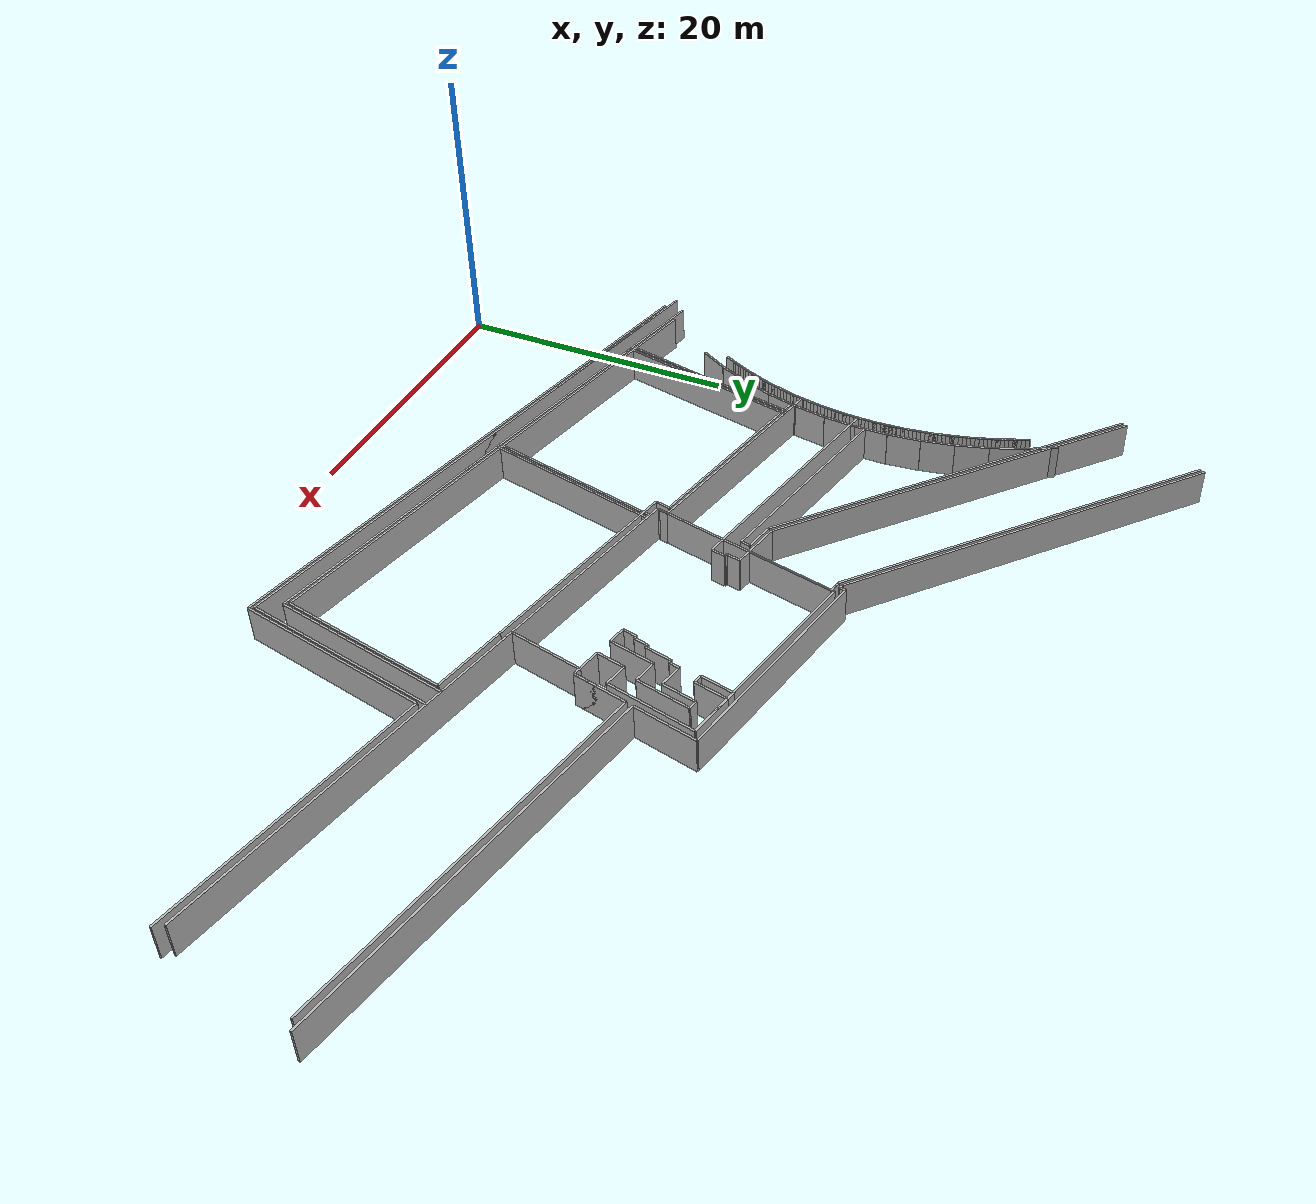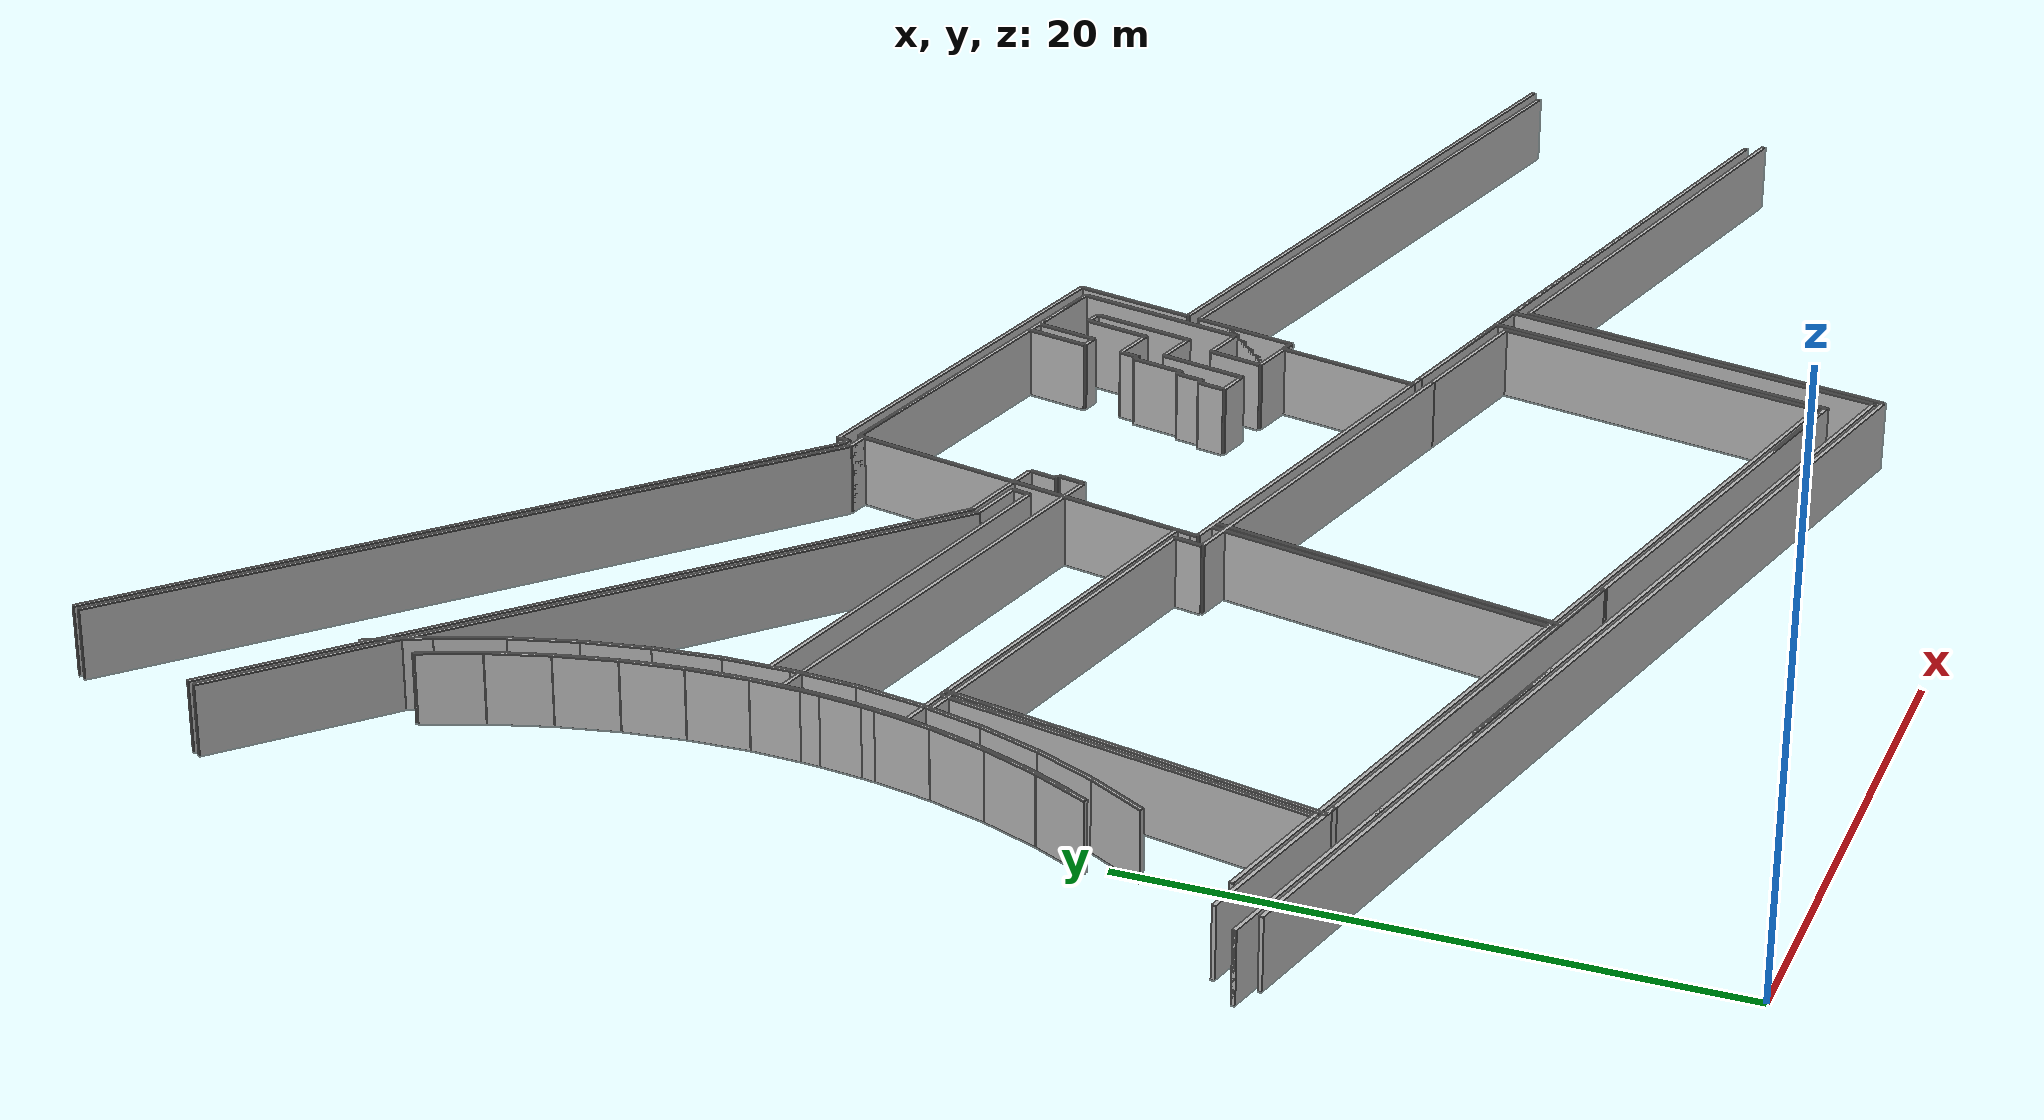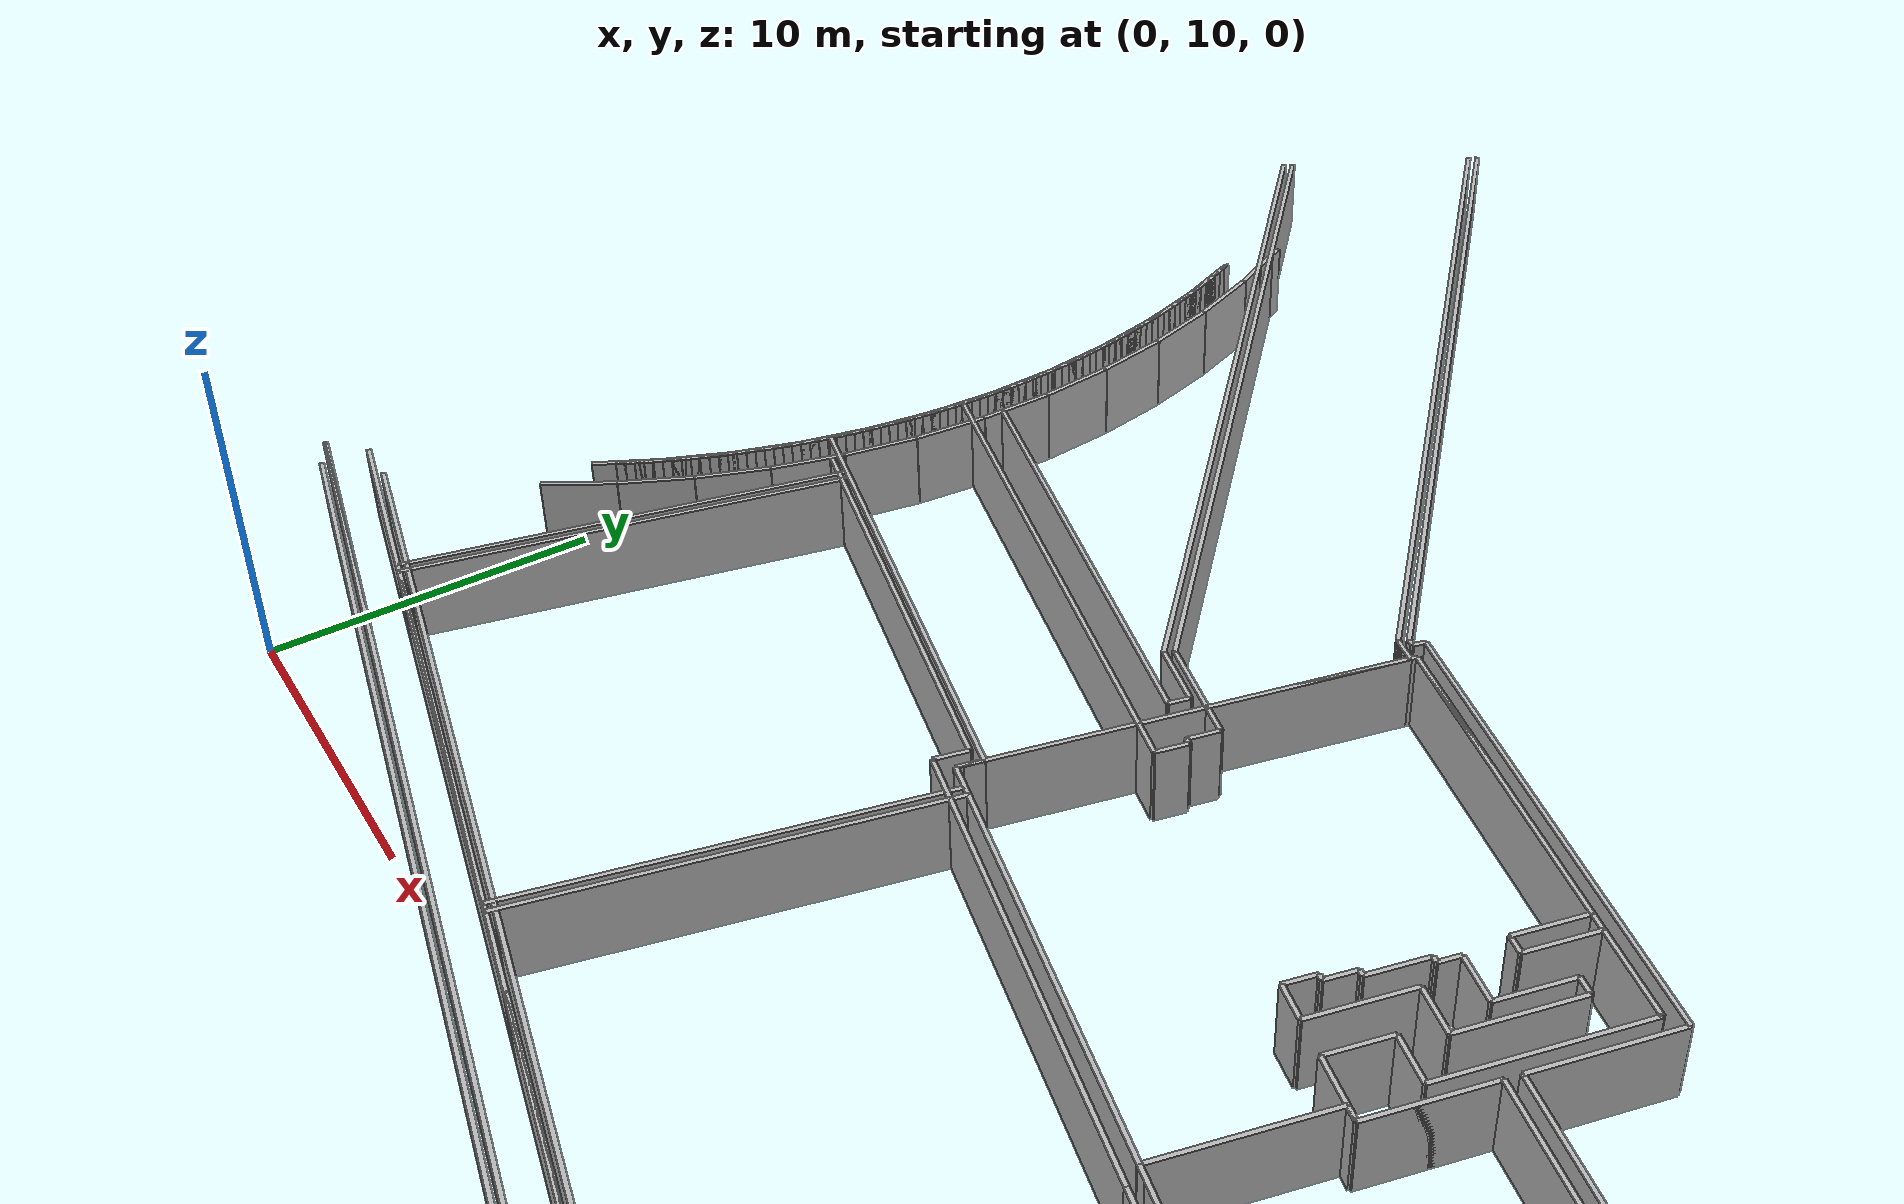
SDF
<?xml version="1.0" ?>
<sdf version="1.6">
  <model name="sps_2404">
    <pose frame="">0 0 0 0 -0 0</pose>
    <static>1</static>
    <self_collide>0</self_collide>
    <allow_auto_disable>0</allow_auto_disable>
    <link name="Wall256">
      <kinematic>0</kinematic>
      <gravity>1</gravity>
      <self_collide>0</self_collide>
      <collision name="collision">
        <geometry>
          <box>
            <size>15.3749 0.15 2.5</size>
          </box>
        </geometry>
        <pose frame="">0 0 0 0 -0 0</pose>
      </collision>
      <visual name="visual">
        <geometry>
          <box>
            <size>15.3749 0.15 2.5</size>
          </box>
        </geometry>
        <pose frame="">0 0 0 0 -0 0</pose>
        <cast_shadows>1</cast_shadows>
        <transparency>0.0</transparency>
      </visual>
      <pose frame="">9.79656 25.8451 1.25 0 -0 2.92735</pose>
    </link>
    <link name="Wall257">
      <kinematic>0</kinematic>
      <gravity>1</gravity>
      <self_collide>0</self_collide>
      <collision name="collision">
        <geometry>
          <box>
            <size>0.199818 0.15 2.5</size>
          </box>
        </geometry>
        <pose frame="">0 0 0 0 -0 0</pose>
      </collision>
      <visual name="visual">
        <geometry>
          <box>
            <size>0.199818 0.15 2.5</size>
          </box>
        </geometry>
        <pose frame="">0 0 0 0 -0 0</pose>
        <cast_shadows>1</cast_shadows>
        <transparency>0.0</transparency>
      </visual>
      <pose frame="">28.732 28.2743 1.25 0 0 -0.209856</pose>
    </link>
    <link name="Wall258">
      <kinematic>0</kinematic>
      <gravity>1</gravity>
      <self_collide>0</self_collide>
      <collision name="collision">
        <geometry>
          <box>
            <size>0.199428 0.15 2.5</size>
          </box>
        </geometry>
        <pose frame="">0 0 0 0 -0 0</pose>
      </collision>
      <visual name="visual">
        <geometry>
          <box>
            <size>0.199428 0.15 2.5</size>
          </box>
        </geometry>
        <pose frame="">0 0 0 0 -0 0</pose>
        <cast_shadows>1</cast_shadows>
        <transparency>0.0</transparency>
      </visual>
      <pose frame="">29.3313 30.0882 1.25 0 0 -0.215283</pose>
    </link>
    <link name="Wall259">
      <kinematic>0</kinematic>
      <gravity>1</gravity>
      <self_collide>0</self_collide>
      <collision name="collision">
        <geometry>
          <box>
            <size>18.5772 0.15 2.5</size>
          </box>
        </geometry>
        <pose frame="">0 0 0 0 -0 0</pose>
      </collision>
      <visual name="visual">
        <geometry>
          <box>
            <size>18.5772 0.15 2.5</size>
          </box>
        </geometry>
        <pose frame="">0 0 0 0 -0 0</pose>
        <cast_shadows>1</cast_shadows>
        <transparency>0.0</transparency>
      </visual>
      <pose frame="">47.042 16.4066 1.25 0 0 -0.214404</pose>
    </link>
    <link name="Wall558">
      <kinematic>0</kinematic>
      <gravity>1</gravity>
      <self_collide>0</self_collide>
      <collision name="collision">
        <geometry>
          <box>
            <size>26.8011 0.15 2.5</size>
          </box>
        </geometry>
        <pose frame="">0 0 0 0 -0 0</pose>
      </collision>
      <visual name="visual">
        <geometry>
          <box>
            <size>26.8011 0.15 2.5</size>
          </box>
        </geometry>
        <pose frame="">0 0 0 0 -0 0</pose>
        <cast_shadows>1</cast_shadows>
        <transparency>0.0</transparency>
      </visual>
      <pose frame="">9.24554 45.6146 1.25 0 -0 2.40377</pose>
    </link>
    <link name="Wall559">
      <kinematic>0</kinematic>
      <gravity>1</gravity>
      <self_collide>0</self_collide>
      <collision name="collision">
        <geometry>
          <box>
            <size>1.20041 0.15 2.5</size>
          </box>
        </geometry>
        <pose frame="">0 0 0 0 -0 0</pose>
      </collision>
      <visual name="visual">
        <geometry>
          <box>
            <size>1.20041 0.15 2.5</size>
          </box>
        </geometry>
        <pose frame="">0 0 0 0 -0 0</pose>
        <cast_shadows>1</cast_shadows>
        <transparency>0.0</transparency>
      </visual>
      <pose frame="">18.8302 28.3825 1.25 0 0 -0.214218</pose>
    </link>
    <link name="Wall560">
      <kinematic>0</kinematic>
      <gravity>1</gravity>
      <self_collide>0</self_collide>
      <collision name="collision">
        <geometry>
          <box>
            <size>0.999913 0.15 2.5</size>
          </box>
        </geometry>
        <pose frame="">0 0 0 0 -0 0</pose>
      </collision>
      <visual name="visual">
        <geometry>
          <box>
            <size>0.999913 0.15 2.5</size>
          </box>
        </geometry>
        <pose frame="">0 0 0 0 -0 0</pose>
        <cast_shadows>1</cast_shadows>
        <transparency>0.0</transparency>
      </visual>
      <pose frame="">19.5227 28.7435 1.25 0 -0 1.35712</pose>
    </link>
    <link name="Wall561">
      <kinematic>0</kinematic>
      <gravity>1</gravity>
      <self_collide>0</self_collide>
      <collision name="collision">
        <geometry>
          <box>
            <size>0.99996 0.15 2.5</size>
          </box>
        </geometry>
        <pose frame="">0 0 0 0 -0 0</pose>
      </collision>
      <visual name="visual">
        <geometry>
          <box>
            <size>0.99996 0.15 2.5</size>
          </box>
        </geometry>
        <pose frame="">0 0 0 0 -0 0</pose>
        <cast_shadows>1</cast_shadows>
        <transparency>0.0</transparency>
      </visual>
      <pose frame="">19.5398 29.7633 1.25 0 -0 1.35719</pose>
    </link>
    <link name="Wall562">
      <kinematic>0</kinematic>
      <gravity>1</gravity>
      <self_collide>0</self_collide>
      <collision name="collision">
        <geometry>
          <box>
            <size>3.20063 0.15 2.5</size>
          </box>
        </geometry>
        <pose frame="">0 0 0 0 -0 0</pose>
      </collision>
      <visual name="visual">
        <geometry>
          <box>
            <size>3.20063 0.15 2.5</size>
          </box>
        </geometry>
        <pose frame="">0 0 0 0 -0 0</pose>
        <cast_shadows>1</cast_shadows>
        <transparency>0.0</transparency>
      </visual>
      <pose frame="">29.5261 27.6922 1.25 0 0 -1.78516</pose>
    </link>
    <link name="Wall563">
      <kinematic>0</kinematic>
      <gravity>1</gravity>
      <self_collide>0</self_collide>
      <collision name="collision">
        <geometry>
          <box>
            <size>3.79922 0.15 2.5</size>
          </box>
        </geometry>
        <pose frame="">0 0 0 0 -0 0</pose>
      </collision>
      <visual name="visual">
        <geometry>
          <box>
            <size>3.79922 0.15 2.5</size>
          </box>
        </geometry>
        <pose frame="">0 0 0 0 -0 0</pose>
        <cast_shadows>1</cast_shadows>
        <transparency>0.0</transparency>
      </visual>
      <pose frame="">32.8187 27.2824 1.25 0 0 -1.78522</pose>
    </link>
    <link name="Wall564">
      <kinematic>0</kinematic>
      <gravity>1</gravity>
      <self_collide>0</self_collide>
      <collision name="collision">
        <geometry>
          <box>
            <size>2.99997 0.15 2.5</size>
          </box>
        </geometry>
        <pose frame="">0 0 0 0 -0 0</pose>
      </collision>
      <visual name="visual">
        <geometry>
          <box>
            <size>2.99997 0.15 2.5</size>
          </box>
        </geometry>
        <pose frame="">0 0 0 0 -0 0</pose>
        <cast_shadows>1</cast_shadows>
        <transparency>0.0</transparency>
      </visual>
      <pose frame="">32.2209 33.9624 1.25 0 0 -0.214514</pose>
    </link>
    <link name="Wall565">
      <kinematic>0</kinematic>
      <gravity>1</gravity>
      <self_collide>0</self_collide>
      <collision name="collision">
        <geometry>
          <box>
            <size>5.22433 0.15 2.5</size>
          </box>
        </geometry>
        <pose frame="">0 0 0 0 -0 0</pose>
      </collision>
      <visual name="visual">
        <geometry>
          <box>
            <size>5.22433 0.15 2.5</size>
          </box>
        </geometry>
        <pose frame="">0 0 0 0 -0 0</pose>
        <cast_shadows>1</cast_shadows>
        <transparency>0.0</transparency>
      </visual>
      <pose frame="">33.7523 19.3007 1.25 0 0 -0.214491</pose>
    </link>
    <link name="Wall852">
      <kinematic>0</kinematic>
      <gravity>1</gravity>
      <self_collide>0</self_collide>
      <collision name="collision">
        <geometry>
          <box>
            <size>13.8779 0.15 2.5</size>
          </box>
        </geometry>
        <pose frame="">0 0 0 0 -0 0</pose>
      </collision>
      <visual name="visual">
        <geometry>
          <box>
            <size>13.8779 0.15 2.5</size>
          </box>
        </geometry>
        <pose frame="">0 0 0 0 -0 0</pose>
        <cast_shadows>1</cast_shadows>
        <transparency>0.0</transparency>
      </visual>
      <pose frame="">9.98656 25.5477 1.25 0 -0 2.92733</pose>
    </link>
    <link name="Wall853">
      <kinematic>0</kinematic>
      <gravity>1</gravity>
      <self_collide>0</self_collide>
      <collision name="collision">
        <geometry>
          <box>
            <size>2.04037 0.15 2.5</size>
          </box>
        </geometry>
        <pose frame="">0 0 0 0 -0 0</pose>
      </collision>
      <visual name="visual">
        <geometry>
          <box>
            <size>2.04037 0.15 2.5</size>
          </box>
        </geometry>
        <pose frame="">0 0 0 0 -0 0</pose>
        <cast_shadows>1</cast_shadows>
        <transparency>0.0</transparency>
      </visual>
      <pose frame="">17.1197 30.4943 1.25 0 -0 2.92705</pose>
    </link>
    <link name="Wall854">
      <kinematic>0</kinematic>
      <gravity>1</gravity>
      <self_collide>0</self_collide>
      <collision name="collision">
        <geometry>
          <box>
            <size>0.9999 0.15 2.5</size>
          </box>
        </geometry>
        <pose frame="">0 0 0 0 -0 0</pose>
      </collision>
      <visual name="visual">
        <geometry>
          <box>
            <size>0.9999 0.15 2.5</size>
          </box>
        </geometry>
        <pose frame="">0 0 0 0 -0 0</pose>
        <cast_shadows>1</cast_shadows>
        <transparency>0.0</transparency>
      </visual>
      <pose frame="">19.1572 30.3579 1.25 0 -0 2.92798</pose>
    </link>
    <link name="Wall855">
      <kinematic>0</kinematic>
      <gravity>1</gravity>
      <self_collide>0</self_collide>
      <collision name="collision">
        <geometry>
          <box>
            <size>0.200192 0.15 2.5</size>
          </box>
        </geometry>
        <pose frame="">0 0 0 0 -0 0</pose>
      </collision>
      <visual name="visual">
        <geometry>
          <box>
            <size>0.200192 0.15 2.5</size>
          </box>
        </geometry>
        <pose frame="">0 0 0 0 -0 0</pose>
        <cast_shadows>1</cast_shadows>
        <transparency>0.0</transparency>
      </visual>
      <pose frame="">19.9863 36.5227 1.25 0 -0 1.36539</pose>
    </link>
    <link name="Wall856">
      <kinematic>0</kinematic>
      <gravity>1</gravity>
      <self_collide>0</self_collide>
      <collision name="collision">
        <geometry>
          <box>
            <size>0.700129 0.15 2.5</size>
          </box>
        </geometry>
        <pose frame="">0 0 0 0 -0 0</pose>
      </collision>
      <visual name="visual">
        <geometry>
          <box>
            <size>0.700129 0.15 2.5</size>
          </box>
        </geometry>
        <pose frame="">0 0 0 0 -0 0</pose>
        <cast_shadows>1</cast_shadows>
        <transparency>0.0</transparency>
      </visual>
      <pose frame="">29.5035 30.4089 1.25 0 -0 1.35547</pose>
    </link>
    <link name="Wall857">
      <kinematic>0</kinematic>
      <gravity>1</gravity>
      <self_collide>0</self_collide>
      <collision name="collision">
        <geometry>
          <box>
            <size>2.29978 0.15 2.5</size>
          </box>
        </geometry>
        <pose frame="">0 0 0 0 -0 0</pose>
      </collision>
      <visual name="visual">
        <geometry>
          <box>
            <size>2.29978 0.15 2.5</size>
          </box>
        </geometry>
        <pose frame="">0 0 0 0 -0 0</pose>
        <cast_shadows>1</cast_shadows>
        <transparency>0.0</transparency>
      </visual>
      <pose frame="">30.5108 33.1581 1.25 0 -0 1.35653</pose>
    </link>
    <link name="Wall858">
      <kinematic>0</kinematic>
      <gravity>1</gravity>
      <self_collide>0</self_collide>
      <collision name="collision">
        <geometry>
          <box>
            <size>13.9981 0.15 2.5</size>
          </box>
        </geometry>
        <pose frame="">0 0 0 0 -0 0</pose>
      </collision>
      <visual name="visual">
        <geometry>
          <box>
            <size>13.9981 0.15 2.5</size>
          </box>
        </geometry>
        <pose frame="">0 0 0 0 -0 0</pose>
        <cast_shadows>1</cast_shadows>
        <transparency>0.0</transparency>
      </visual>
      <pose frame="">23.9769 21.9407 1.25 0 -0 2.92733</pose>
    </link>
    <link name="Wall859">
      <kinematic>0</kinematic>
      <gravity>1</gravity>
      <self_collide>0</self_collide>
      <collision name="collision">
        <geometry>
          <box>
            <size>3.80044 0.15 2.5</size>
          </box>
        </geometry>
        <pose frame="">0 0 0 0 -0 0</pose>
      </collision>
      <visual name="visual">
        <geometry>
          <box>
            <size>3.80044 0.15 2.5</size>
          </box>
        </geometry>
        <pose frame="">0 0 0 0 -0 0</pose>
        <cast_shadows>1</cast_shadows>
        <transparency>0.0</transparency>
      </visual>
      <pose frame="">31.8341 30.7719 1.25 0 0 -1.78503</pose>
    </link>
    <link name="Wall860">
      <kinematic>0</kinematic>
      <gravity>1</gravity>
      <self_collide>0</self_collide>
      <collision name="collision">
        <geometry>
          <box>
            <size>2.10379 0.15 2.5</size>
          </box>
        </geometry>
        <pose frame="">0 0 0 0 -0 0</pose>
      </collision>
      <visual name="visual">
        <geometry>
          <box>
            <size>2.10379 0.15 2.5</size>
          </box>
        </geometry>
        <pose frame="">0 0 0 0 -0 0</pose>
        <cast_shadows>1</cast_shadows>
        <transparency>0.0</transparency>
      </visual>
      <pose frame="">31.3866 25.6497 1.25 0 0 -0.214027</pose>
    </link>
    <link name="Wall861">
      <kinematic>0</kinematic>
      <gravity>1</gravity>
      <self_collide>0</self_collide>
      <collision name="collision">
        <geometry>
          <box>
            <size>12.0015 0.15 2.5</size>
          </box>
        </geometry>
        <pose frame="">0 0 0 0 -0 0</pose>
      </collision>
      <visual name="visual">
        <geometry>
          <box>
            <size>12.0015 0.15 2.5</size>
          </box>
        </geometry>
        <pose frame="">0 0 0 0 -0 0</pose>
        <cast_shadows>1</cast_shadows>
        <transparency>0.0</transparency>
      </visual>
      <pose frame="">35.1147 12.8631 1.25 0 -0 1.37118</pose>
    </link>
    <link name="Wall862">
      <kinematic>0</kinematic>
      <gravity>1</gravity>
      <self_collide>0</self_collide>
      <collision name="collision">
        <geometry>
          <box>
            <size>5.46534 0.15 2.5</size>
          </box>
        </geometry>
        <pose frame="">0 0 0 0 -0 0</pose>
      </collision>
      <visual name="visual">
        <geometry>
          <box>
            <size>5.46534 0.15 2.5</size>
          </box>
        </geometry>
        <pose frame="">0 0 0 0 -0 0</pose>
        <cast_shadows>1</cast_shadows>
        <transparency>0.0</transparency>
      </visual>
      <pose frame="">33.9782 19.7631 1.25 0 0 -0.214394</pose>
    </link>
    <link name="Wall1167">
      <kinematic>0</kinematic>
      <gravity>1</gravity>
      <self_collide>0</self_collide>
      <collision name="collision">
        <geometry>
          <box>
            <size>0.800156 0.15 2.5</size>
          </box>
        </geometry>
        <pose frame="">0 0 0 0 -0 0</pose>
      </collision>
      <visual name="visual">
        <geometry>
          <box>
            <size>0.800156 0.15 2.5</size>
          </box>
        </geometry>
        <pose frame="">0 0 0 0 -0 0</pose>
        <cast_shadows>1</cast_shadows>
        <transparency>0.0</transparency>
      </visual>
      <pose frame="">17.223 23.8198 1.25 0 -0 1.35618</pose>
    </link>
    <link name="Wall1168">
      <kinematic>0</kinematic>
      <gravity>1</gravity>
      <self_collide>0</self_collide>
      <collision name="collision">
        <geometry>
          <box>
            <size>26.7999 0.15 2.5</size>
          </box>
        </geometry>
        <pose frame="">0 0 0 0 -0 0</pose>
      </collision>
      <visual name="visual">
        <geometry>
          <box>
            <size>26.7999 0.15 2.5</size>
          </box>
        </geometry>
        <pose frame="">0 0 0 0 -0 0</pose>
        <cast_shadows>1</cast_shadows>
        <transparency>0.0</transparency>
      </visual>
      <pose frame="">9.38766 45.8899 1.25 0 0 -0.737837</pose>
    </link>
    <link name="Wall1169">
      <kinematic>0</kinematic>
      <gravity>1</gravity>
      <self_collide>0</self_collide>
      <collision name="collision">
        <geometry>
          <box>
            <size>0.199428 0.15 2.5</size>
          </box>
        </geometry>
        <pose frame="">0 0 0 0 -0 0</pose>
      </collision>
      <visual name="visual">
        <geometry>
          <box>
            <size>0.199428 0.15 2.5</size>
          </box>
        </geometry>
        <pose frame="">0 0 0 0 -0 0</pose>
        <cast_shadows>1</cast_shadows>
        <transparency>0.0</transparency>
      </visual>
      <pose frame="">19.5313 29.2534 1.25 0 -0 2.92631</pose>
    </link>
    <link name="Wall1170">
      <kinematic>0</kinematic>
      <gravity>1</gravity>
      <self_collide>0</self_collide>
      <collision name="collision">
        <geometry>
          <box>
            <size>0.823743 0.15 2.5</size>
          </box>
        </geometry>
        <pose frame="">0 0 0 0 -0 0</pose>
      </collision>
      <visual name="visual">
        <geometry>
          <box>
            <size>0.823743 0.15 2.5</size>
          </box>
        </geometry>
        <pose frame="">0 0 0 0 -0 0</pose>
        <cast_shadows>1</cast_shadows>
        <transparency>0.0</transparency>
      </visual>
      <pose frame="">19.5634 36.5125 1.25 0 -0 2.92677</pose>
    </link>
    <link name="Wall1171">
      <kinematic>0</kinematic>
      <gravity>1</gravity>
      <self_collide>0</self_collide>
      <collision name="collision">
        <geometry>
          <box>
            <size>1.89952 0.15 2.5</size>
          </box>
        </geometry>
        <pose frame="">0 0 0 0 -0 0</pose>
      </collision>
      <visual name="visual">
        <geometry>
          <box>
            <size>1.89952 0.15 2.5</size>
          </box>
        </geometry>
        <pose frame="">0 0 0 0 -0 0</pose>
        <cast_shadows>1</cast_shadows>
        <transparency>0.0</transparency>
      </visual>
      <pose frame="">29.0318 29.1815 1.25 0 -0 1.35638</pose>
    </link>
    <link name="Wall1172">
      <kinematic>0</kinematic>
      <gravity>1</gravity>
      <self_collide>0</self_collide>
      <collision name="collision">
        <geometry>
          <box>
            <size>10.4005 0.15 2.5</size>
          </box>
        </geometry>
        <pose frame="">0 0 0 0 -0 0</pose>
      </collision>
      <visual name="visual">
        <geometry>
          <box>
            <size>10.4005 0.15 2.5</size>
          </box>
        </geometry>
        <pose frame="">0 0 0 0 -0 0</pose>
        <cast_shadows>1</cast_shadows>
        <transparency>0.0</transparency>
      </visual>
      <pose frame="">25.088 35.5149 1.25 0 0 -0.214281</pose>
    </link>
    <link name="Wall1173">
      <kinematic>0</kinematic>
      <gravity>1</gravity>
      <self_collide>0</self_collide>
      <collision name="collision">
        <geometry>
          <box>
            <size>0.599683 0.15 2.5</size>
          </box>
        </geometry>
        <pose frame="">0 0 0 0 -0 0</pose>
      </collision>
      <visual name="visual">
        <geometry>
          <box>
            <size>0.599683 0.15 2.5</size>
          </box>
        </geometry>
        <pose frame="">0 0 0 0 -0 0</pose>
        <cast_shadows>1</cast_shadows>
        <transparency>0.0</transparency>
      </visual>
      <pose frame="">29.9733 32.0982 1.25 0 0 -0.214043</pose>
    </link>
    <link name="Wall1174">
      <kinematic>0</kinematic>
      <gravity>1</gravity>
      <self_collide>0</self_collide>
      <collision name="collision">
        <geometry>
          <box>
            <size>4.50077 0.15 2.5</size>
          </box>
        </geometry>
        <pose frame="">0 0 0 0 -0 0</pose>
      </collision>
      <visual name="visual">
        <geometry>
          <box>
            <size>4.50077 0.15 2.5</size>
          </box>
        </geometry>
        <pose frame="">0 0 0 0 -0 0</pose>
        <cast_shadows>1</cast_shadows>
        <transparency>0.0</transparency>
      </visual>
      <pose frame="">33.8043 31.8267 1.25 0 0 -1.78451</pose>
    </link>
    <link name="Wall1175">
      <kinematic>0</kinematic>
      <gravity>1</gravity>
      <self_collide>0</self_collide>
      <collision name="collision">
        <geometry>
          <box>
            <size>14.9998 0.15 2.5</size>
          </box>
        </geometry>
        <pose frame="">0 0 0 0 -0 0</pose>
      </collision>
      <visual name="visual">
        <geometry>
          <box>
            <size>14.9998 0.15 2.5</size>
          </box>
        </geometry>
        <pose frame="">0 0 0 0 -0 0</pose>
        <cast_shadows>1</cast_shadows>
        <transparency>0.0</transparency>
      </visual>
      <pose frame="">26.9532 35.6207 1.25 0 0 -0.214277</pose>
    </link>
    <link name="Wall1176">
      <kinematic>0</kinematic>
      <gravity>1</gravity>
      <self_collide>0</self_collide>
      <collision name="collision">
        <geometry>
          <box>
            <size>13.7013 0.15 2.5</size>
          </box>
        </geometry>
        <pose frame="">0 0 0 0 -0 0</pose>
      </collision>
      <visual name="visual">
        <geometry>
          <box>
            <size>13.7013 0.15 2.5</size>
          </box>
        </geometry>
        <pose frame="">0 0 0 0 -0 0</pose>
        <cast_shadows>1</cast_shadows>
        <transparency>0.0</transparency>
      </visual>
      <pose frame="">36.6075 11.6683 1.25 0 -0 1.37117</pose>
    </link>
    <link name="Wall1457">
      <kinematic>0</kinematic>
      <gravity>1</gravity>
      <self_collide>0</self_collide>
      <collision name="collision">
        <geometry>
          <box>
            <size>26.7988 0.15 2.5</size>
          </box>
        </geometry>
        <pose frame="">0 0 0 0 -0 0</pose>
      </collision>
      <visual name="visual">
        <geometry>
          <box>
            <size>26.7988 0.15 2.5</size>
          </box>
        </geometry>
        <pose frame="">0 0 0 0 -0 0</pose>
        <cast_shadows>1</cast_shadows>
        <transparency>0.0</transparency>
      </visual>
      <pose frame="">6.20837 39.7252 1.25 0 -0 2.40375</pose>
    </link>
    <link name="Wall1458">
      <kinematic>0</kinematic>
      <gravity>1</gravity>
      <self_collide>0</self_collide>
      <collision name="collision">
        <geometry>
          <box>
            <size>0.649526 0.15 2.5</size>
          </box>
        </geometry>
        <pose frame="">0 0 0 0 -0 0</pose>
      </collision>
      <visual name="visual">
        <geometry>
          <box>
            <size>0.649526 0.15 2.5</size>
          </box>
        </geometry>
        <pose frame="">0 0 0 0 -0 0</pose>
        <cast_shadows>1</cast_shadows>
        <transparency>0.0</transparency>
      </visual>
      <pose frame="">18.0474 29.9598 1.25 0 -0 1.35632</pose>
    </link>
    <link name="Wall1459">
      <kinematic>0</kinematic>
      <gravity>1</gravity>
      <self_collide>0</self_collide>
      <collision name="collision">
        <geometry>
          <box>
            <size>16.702 0.15 2.5</size>
          </box>
        </geometry>
        <pose frame="">0 0 0 0 -0 0</pose>
      </collision>
      <visual name="visual">
        <geometry>
          <box>
            <size>16.702 0.15 2.5</size>
          </box>
        </geometry>
        <pose frame="">0 0 0 0 -0 0</pose>
        <cast_shadows>1</cast_shadows>
        <transparency>0.0</transparency>
      </visual>
      <pose frame="">10.1281 11.9036 1.25 0 0 -0.214245</pose>
    </link>
    <link name="Wall1460">
      <kinematic>0</kinematic>
      <gravity>1</gravity>
      <self_collide>0</self_collide>
      <collision name="collision">
        <geometry>
          <box>
            <size>1.19981 0.15 2.5</size>
          </box>
        </geometry>
        <pose frame="">0 0 0 0 -0 0</pose>
      </collision>
      <visual name="visual">
        <geometry>
          <box>
            <size>1.19981 0.15 2.5</size>
          </box>
        </geometry>
        <pose frame="">0 0 0 0 -0 0</pose>
        <cast_shadows>1</cast_shadows>
        <transparency>0.0</transparency>
      </visual>
      <pose frame="">28.5995 26.2565 1.25 0 -0 2.92659</pose>
    </link>
    <link name="Wall1461">
      <kinematic>0</kinematic>
      <gravity>1</gravity>
      <self_collide>0</self_collide>
      <collision name="collision">
        <geometry>
          <box>
            <size>2.29978 0.15 2.5</size>
          </box>
        </geometry>
        <pose frame="">0 0 0 0 -0 0</pose>
      </collision>
      <visual name="visual">
        <geometry>
          <box>
            <size>2.29978 0.15 2.5</size>
          </box>
        </geometry>
        <pose frame="">0 0 0 0 -0 0</pose>
        <cast_shadows>1</cast_shadows>
        <transparency>0.0</transparency>
      </visual>
      <pose frame="">29.9248 33.2855 1.25 0 0 -1.78507</pose>
    </link>
    <link name="Wall1462">
      <kinematic>0</kinematic>
      <gravity>1</gravity>
      <self_collide>0</self_collide>
      <collision name="collision">
        <geometry>
          <box>
            <size>2.00057 0.15 2.5</size>
          </box>
        </geometry>
        <pose frame="">0 0 0 0 -0 0</pose>
      </collision>
      <visual name="visual">
        <geometry>
          <box>
            <size>2.00057 0.15 2.5</size>
          </box>
        </geometry>
        <pose frame="">0 0 0 0 -0 0</pose>
        <cast_shadows>1</cast_shadows>
        <transparency>0.0</transparency>
      </visual>
      <pose frame="">30.5715 26.8505 1.25 0 0 -1.78517</pose>
    </link>
    <link name="Wall1463">
      <kinematic>0</kinematic>
      <gravity>1</gravity>
      <self_collide>0</self_collide>
      <collision name="collision">
        <geometry>
          <box>
            <size>14.9993 0.15 2.5</size>
          </box>
        </geometry>
        <pose frame="">0 0 0 0 -0 0</pose>
      </collision>
      <visual name="visual">
        <geometry>
          <box>
            <size>14.9993 0.15 2.5</size>
          </box>
        </geometry>
        <pose frame="">0 0 0 0 -0 0</pose>
        <cast_shadows>1</cast_shadows>
        <transparency>0.0</transparency>
      </visual>
      <pose frame="">23.8719 21.4516 1.25 0 -0 2.92729</pose>
    </link>
    <link name="Wall1464">
      <kinematic>0</kinematic>
      <gravity>1</gravity>
      <self_collide>0</self_collide>
      <collision name="collision">
        <geometry>
          <box>
            <size>41.6722 0.15 2.5</size>
          </box>
        </geometry>
        <pose frame="">0 0 0 0 -0 0</pose>
      </collision>
      <visual name="visual">
        <geometry>
          <box>
            <size>41.6722 0.15 2.5</size>
          </box>
        </geometry>
        <pose frame="">0 0 0 0 -0 0</pose>
        <cast_shadows>1</cast_shadows>
        <transparency>0.0</transparency>
      </visual>
      <pose frame="">14.6948 9.68199 1.25 0 0 -0.214251</pose>
    </link>
    <link name="Wall1466">
      <kinematic>0</kinematic>
      <gravity>1</gravity>
      <self_collide>0</self_collide>
      <collision name="collision">
        <geometry>
          <box>
            <size>25 0.15 2.5</size>
          </box>
        </geometry>
        <pose frame="">0 0 0 0 -0 0</pose>
      </collision>
      <visual name="visual">
        <geometry>
          <box>
            <size>25 0.15 2.5</size>
          </box>
        </geometry>
        <pose frame="">0 0 0 0 -0 0</pose>
        <cast_shadows>1</cast_shadows>
        <transparency>0.0</transparency>
      </visual>
      <pose frame="">45.4367 26.4789 1.25 0 0 -0.214407</pose>
    </link>
    <link name="Wall1773">
      <kinematic>0</kinematic>
      <gravity>1</gravity>
      <self_collide>0</self_collide>
      <collision name="collision">
        <geometry>
          <box>
            <size>26.7999 0.15 2.5</size>
          </box>
        </geometry>
        <pose frame="">0 0 0 0 -0 0</pose>
      </collision>
      <visual name="visual">
        <geometry>
          <box>
            <size>26.7999 0.15 2.5</size>
          </box>
        </geometry>
        <pose frame="">0 0 0 0 -0 0</pose>
        <cast_shadows>1</cast_shadows>
        <transparency>0.0</transparency>
      </visual>
      <pose frame="">6.35107 40.0013 1.25 0 -0 2.40376</pose>
    </link>
    <link name="Wall1774">
      <kinematic>0</kinematic>
      <gravity>1</gravity>
      <self_collide>0</self_collide>
      <collision name="collision">
        <geometry>
          <box>
            <size>12.7769 0.15 2.5</size>
          </box>
        </geometry>
        <pose frame="">0 0 0 0 -0 0</pose>
      </collision>
      <visual name="visual">
        <geometry>
          <box>
            <size>12.7769 0.15 2.5</size>
          </box>
        </geometry>
        <pose frame="">0 0 0 0 -0 0</pose>
        <cast_shadows>1</cast_shadows>
        <transparency>0.0</transparency>
      </visual>
      <pose frame="">16.8747 16.9731 1.25 0 0 -1.78505</pose>
    </link>
    <link name="Wall1775">
      <kinematic>0</kinematic>
      <gravity>1</gravity>
      <self_collide>0</self_collide>
      <collision name="collision">
        <geometry>
          <box>
            <size>2.45895 0.15 2.5</size>
          </box>
        </geometry>
        <pose frame="">0 0 0 0 -0 0</pose>
      </collision>
      <visual name="visual">
        <geometry>
          <box>
            <size>2.45895 0.15 2.5</size>
          </box>
        </geometry>
        <pose frame="">0 0 0 0 -0 0</pose>
        <cast_shadows>1</cast_shadows>
        <transparency>0.0</transparency>
      </visual>
      <pose frame="">17.4674 30.7256 1.25 0 -0 2.92708</pose>
    </link>
    <link name="Wall1776">
      <kinematic>0</kinematic>
      <gravity>1</gravity>
      <self_collide>0</self_collide>
      <collision name="collision">
        <geometry>
          <box>
            <size>0.400685 0.15 2.5</size>
          </box>
        </geometry>
        <pose frame="">0 0 0 0 -0 0</pose>
      </collision>
      <visual name="visual">
        <geometry>
          <box>
            <size>0.400685 0.15 2.5</size>
          </box>
        </geometry>
        <pose frame="">0 0 0 0 -0 0</pose>
        <cast_shadows>1</cast_shadows>
        <transparency>0.0</transparency>
      </visual>
      <pose frame="">19.5828 37.0196 1.25 0 -0 1.35963</pose>
    </link>
    <link name="Wall1777">
      <kinematic>0</kinematic>
      <gravity>1</gravity>
      <self_collide>0</self_collide>
      <collision name="collision">
        <geometry>
          <box>
            <size>0.999545 0.15 2.5</size>
          </box>
        </geometry>
        <pose frame="">0 0 0 0 -0 0</pose>
      </collision>
      <visual name="visual">
        <geometry>
          <box>
            <size>0.999545 0.15 2.5</size>
          </box>
        </geometry>
        <pose frame="">0 0 0 0 -0 0</pose>
        <cast_shadows>1</cast_shadows>
        <transparency>0.0</transparency>
      </visual>
      <pose frame="">28.1199 26.8728 1.25 0 -0 1.35623</pose>
    </link>
    <link name="Wall1778">
      <kinematic>0</kinematic>
      <gravity>1</gravity>
      <self_collide>0</self_collide>
      <collision name="collision">
        <geometry>
          <box>
            <size>0.999584 0.15 2.5</size>
          </box>
        </geometry>
        <pose frame="">0 0 0 0 -0 0</pose>
      </collision>
      <visual name="visual">
        <geometry>
          <box>
            <size>0.999584 0.15 2.5</size>
          </box>
        </geometry>
        <pose frame="">0 0 0 0 -0 0</pose>
        <cast_shadows>1</cast_shadows>
        <transparency>0.0</transparency>
      </visual>
      <pose frame="">28.5277 27.8068 1.25 0 -0 1.35605</pose>
    </link>
    <link name="Wall1779">
      <kinematic>0</kinematic>
      <gravity>1</gravity>
      <self_collide>0</self_collide>
      <collision name="collision">
        <geometry>
          <box>
            <size>2.40023 0.15 2.5</size>
          </box>
        </geometry>
        <pose frame="">0 0 0 0 -0 0</pose>
      </collision>
      <visual name="visual">
        <geometry>
          <box>
            <size>2.40023 0.15 2.5</size>
          </box>
        </geometry>
        <pose frame="">0 0 0 0 -0 0</pose>
        <cast_shadows>1</cast_shadows>
        <transparency>0.0</transparency>
      </visual>
      <pose frame="">31.3964 31.5833 1.25 0 -0 1.35616</pose>
    </link>
    <link name="Wall1780">
      <kinematic>0</kinematic>
      <gravity>1</gravity>
      <self_collide>0</self_collide>
      <collision name="collision">
        <geometry>
          <box>
            <size>0.599644 0.15 2.5</size>
          </box>
        </geometry>
        <pose frame="">0 0 0 0 -0 0</pose>
      </collision>
      <visual name="visual">
        <geometry>
          <box>
            <size>0.599644 0.15 2.5</size>
          </box>
        </geometry>
        <pose frame="">0 0 0 0 -0 0</pose>
        <cast_shadows>1</cast_shadows>
        <transparency>0.0</transparency>
      </visual>
      <pose frame="">31.9451 32.6923 1.25 0 0 -0.213745</pose>
    </link>
    <link name="Wall1781">
      <kinematic>0</kinematic>
      <gravity>1</gravity>
      <self_collide>0</self_collide>
      <collision name="collision">
        <geometry>
          <box>
            <size>6.29948 0.15 2.5</size>
          </box>
        </geometry>
        <pose frame="">0 0 0 0 -0 0</pose>
      </collision>
      <visual name="visual">
        <geometry>
          <box>
            <size>6.29948 0.15 2.5</size>
          </box>
        </geometry>
        <pose frame="">0 0 0 0 -0 0</pose>
        <cast_shadows>1</cast_shadows>
        <transparency>0.0</transparency>
      </visual>
      <pose frame="">33.0167 30.5654 1.25 0 0 -1.78509</pose>
    </link>
    <link name="Wall1782">
      <kinematic>0</kinematic>
      <gravity>1</gravity>
      <self_collide>0</self_collide>
      <collision name="collision">
        <geometry>
          <box>
            <size>40.8702 0.15 2.5</size>
          </box>
        </geometry>
        <pose frame="">0 0 0 0 -0 0</pose>
      </collision>
      <visual name="visual">
        <geometry>
          <box>
            <size>40.8702 0.15 2.5</size>
          </box>
        </geometry>
        <pose frame="">0 0 0 0 -0 0</pose>
        <cast_shadows>1</cast_shadows>
        <transparency>0.0</transparency>
      </visual>
      <pose frame="">15.2812 9.29848 1.25 0 0 -0.214249</pose>
    </link>
    <link name="Wall1783">
      <kinematic>0</kinematic>
      <gravity>1</gravity>
      <self_collide>0</self_collide>
      <collision name="collision">
        <geometry>
          <box>
            <size>13.9512 0.15 2.5</size>
          </box>
        </geometry>
        <pose frame="">0 0 0 0 -0 0</pose>
      </collision>
      <visual name="visual">
        <geometry>
          <box>
            <size>13.9512 0.15 2.5</size>
          </box>
        </geometry>
        <pose frame="">0 0 0 0 -0 0</pose>
        <cast_shadows>1</cast_shadows>
        <transparency>0.0</transparency>
      </visual>
      <pose frame="">36.4377 12.089 1.25 0 -0 1.37118</pose>
    </link>
    <link name="Wall1785">
      <kinematic>0</kinematic>
      <gravity>1</gravity>
      <self_collide>0</self_collide>
      <collision name="collision">
        <geometry>
          <box>
            <size>25.5023 0.15 2.5</size>
          </box>
        </geometry>
        <pose frame="">0 0 0 0 -0 0</pose>
      </collision>
      <visual name="visual">
        <geometry>
          <box>
            <size>25.5023 0.15 2.5</size>
          </box>
        </geometry>
        <pose frame="">0 0 0 0 -0 0</pose>
        <cast_shadows>1</cast_shadows>
        <transparency>0.0</transparency>
      </visual>
      <pose frame="">45.7862 26.9145 1.25 0 0 -0.214405</pose>
    </link>
    <link name="Wall2082">
      <kinematic>0</kinematic>
      <gravity>1</gravity>
      <self_collide>0</self_collide>
      <collision name="collision">
        <geometry>
          <box>
            <size>0.299831 0.15 2.5</size>
          </box>
        </geometry>
        <pose frame="">0 0 0 0 -0 0</pose>
      </collision>
      <visual name="visual">
        <geometry>
          <box>
            <size>0.299831 0.15 2.5</size>
          </box>
        </geometry>
        <pose frame="">0 0 0 0 -0 0</pose>
        <cast_shadows>1</cast_shadows>
        <transparency>0.0</transparency>
      </visual>
      <pose frame="">1.82156 13.711 1.25 0 0 -0.214363</pose>
    </link>
    <link name="Wall2083">
      <kinematic>0</kinematic>
      <gravity>1</gravity>
      <self_collide>0</self_collide>
      <collision name="collision">
        <geometry>
          <box>
            <size>1.04972 0.15 2.5</size>
          </box>
        </geometry>
        <pose frame="">0 0 0 0 -0 0</pose>
      </collision>
      <visual name="visual">
        <geometry>
          <box>
            <size>1.04972 0.15 2.5</size>
          </box>
        </geometry>
        <pose frame="">0 0 0 0 -0 0</pose>
        <cast_shadows>1</cast_shadows>
        <transparency>0.0</transparency>
      </visual>
      <pose frame="">16.6554 23.5594 1.25 0 -0 1.35671</pose>
    </link>
    <link name="Wall2084">
      <kinematic>0</kinematic>
      <gravity>1</gravity>
      <self_collide>0</self_collide>
      <collision name="collision">
        <geometry>
          <box>
            <size>14.4203 0.15 2.5</size>
          </box>
        </geometry>
        <pose frame="">0 0 0 0 -0 0</pose>
      </collision>
      <visual name="visual">
        <geometry>
          <box>
            <size>14.4203 0.15 2.5</size>
          </box>
        </geometry>
        <pose frame="">0 0 0 0 -0 0</pose>
        <cast_shadows>1</cast_shadows>
        <transparency>0.0</transparency>
      </visual>
      <pose frame="">10.9329 31.1755 1.25 0 -0 2.92734</pose>
    </link>
    <link name="Wall2085">
      <kinematic>0</kinematic>
      <gravity>1</gravity>
      <self_collide>0</self_collide>
      <collision name="collision">
        <geometry>
          <box>
            <size>0.300031 0.15 2.5</size>
          </box>
        </geometry>
        <pose frame="">0 0 0 0 -0 0</pose>
      </collision>
      <visual name="visual">
        <geometry>
          <box>
            <size>0.300031 0.15 2.5</size>
          </box>
        </geometry>
        <pose frame="">0 0 0 0 -0 0</pose>
        <cast_shadows>1</cast_shadows>
        <transparency>0.0</transparency>
      </visual>
      <pose frame="">18.4348 10.0963 1.25 0 0 -0.213594</pose>
    </link>
    <link name="Wall2086">
      <kinematic>0</kinematic>
      <gravity>1</gravity>
      <self_collide>0</self_collide>
      <collision name="collision">
        <geometry>
          <box>
            <size>0.199547 0.15 2.5</size>
          </box>
        </geometry>
        <pose frame="">0 0 0 0 -0 0</pose>
      </collision>
      <visual name="visual">
        <geometry>
          <box>
            <size>0.199547 0.15 2.5</size>
          </box>
        </geometry>
        <pose frame="">0 0 0 0 -0 0</pose>
        <cast_shadows>1</cast_shadows>
        <transparency>0.0</transparency>
      </visual>
      <pose frame="">28.3238 27.3398 1.25 0 0 -0.215152</pose>
    </link>
    <link name="Wall2087">
      <kinematic>0</kinematic>
      <gravity>1</gravity>
      <self_collide>0</self_collide>
      <collision name="collision">
        <geometry>
          <box>
            <size>1.59916 0.15 2.5</size>
          </box>
        </geometry>
        <pose frame="">0 0 0 0 -0 0</pose>
      </collision>
      <visual name="visual">
        <geometry>
          <box>
            <size>1.59916 0.15 2.5</size>
          </box>
        </geometry>
        <pose frame="">0 0 0 0 -0 0</pose>
        <cast_shadows>1</cast_shadows>
        <transparency>0.0</transparency>
      </visual>
      <pose frame="">30.3595 30.5808 1.25 0 0 -0.214343</pose>
    </link>
    <link name="Wall2088">
      <kinematic>0</kinematic>
      <gravity>1</gravity>
      <self_collide>0</self_collide>
      <collision name="collision">
        <geometry>
          <box>
            <size>0.503891 0.15 2.5</size>
          </box>
        </geometry>
        <pose frame="">0 0 0 0 -0 0</pose>
      </collision>
      <visual name="visual">
        <geometry>
          <box>
            <size>0.503891 0.15 2.5</size>
          </box>
        </geometry>
        <pose frame="">0 0 0 0 -0 0</pose>
        <cast_shadows>1</cast_shadows>
        <transparency>0.0</transparency>
      </visual>
      <pose frame="">31.062 20.3985 1.25 0 0 -0.215949</pose>
    </link>
    <link name="Wall2089">
      <kinematic>0</kinematic>
      <gravity>1</gravity>
      <self_collide>0</self_collide>
      <collision name="collision">
        <geometry>
          <box>
            <size>1.6003 0.15 2.5</size>
          </box>
        </geometry>
        <pose frame="">0 0 0 0 -0 0</pose>
      </collision>
      <visual name="visual">
        <geometry>
          <box>
            <size>1.6003 0.15 2.5</size>
          </box>
        </geometry>
        <pose frame="">0 0 0 0 -0 0</pose>
        <cast_shadows>1</cast_shadows>
        <transparency>0.0</transparency>
      </visual>
      <pose frame="">30.6483 29.0855 1.25 0 -0 2.92702</pose>
    </link>
    <link name="Wall2090">
      <kinematic>0</kinematic>
      <gravity>1</gravity>
      <self_collide>0</self_collide>
      <collision name="collision">
        <geometry>
          <box>
            <size>1.59923 0.15 2.5</size>
          </box>
        </geometry>
        <pose frame="">0 0 0 0 -0 0</pose>
      </collision>
      <visual name="visual">
        <geometry>
          <box>
            <size>1.59923 0.15 2.5</size>
          </box>
        </geometry>
        <pose frame="">0 0 0 0 -0 0</pose>
        <cast_shadows>1</cast_shadows>
        <transparency>0.0</transparency>
      </visual>
      <pose frame="">31.5656 27.6578 1.25 0 -0 2.92722</pose>
    </link>
    <link name="Wall2091">
      <kinematic>0</kinematic>
      <gravity>1</gravity>
      <self_collide>0</self_collide>
      <collision name="collision">
        <geometry>
          <box>
            <size>38.0241 0.15 2.5</size>
          </box>
        </geometry>
        <pose frame="">0 0 0 0 -0 0</pose>
      </collision>
      <visual name="visual">
        <geometry>
          <box>
            <size>38.0241 0.15 2.5</size>
          </box>
        </geometry>
        <pose frame="">0 0 0 0 -0 0</pose>
        <cast_shadows>1</cast_shadows>
        <transparency>0.0</transparency>
      </visual>
      <pose frame="">15.3474 11.0237 1.25 0 0 -0.214246</pose>
    </link>
    <link name="Wall2092">
      <kinematic>0</kinematic>
      <gravity>1</gravity>
      <self_collide>0</self_collide>
      <collision name="collision">
        <geometry>
          <box>
            <size>15.9016 0.15 2.5</size>
          </box>
        </geometry>
        <pose frame="">0 0 0 0 -0 0</pose>
      </collision>
      <visual name="visual">
        <geometry>
          <box>
            <size>15.9016 0.15 2.5</size>
          </box>
        </geometry>
        <pose frame="">0 0 0 0 -0 0</pose>
        <cast_shadows>1</cast_shadows>
        <transparency>0.0</transparency>
      </visual>
      <pose frame="">26.3505 8.37398 1.25 0 0 -0.214254</pose>
    </link>
    <link name="Wall2093">
      <kinematic>0</kinematic>
      <gravity>1</gravity>
      <self_collide>0</self_collide>
      <collision name="collision">
        <geometry>
          <box>
            <size>12.7515 0.15 2.5</size>
          </box>
        </geometry>
        <pose frame="">0 0 0 0 -0 0</pose>
      </collision>
      <visual name="visual">
        <geometry>
          <box>
            <size>12.7515 0.15 2.5</size>
          </box>
        </geometry>
        <pose frame="">0 0 0 0 -0 0</pose>
        <cast_shadows>1</cast_shadows>
        <transparency>0.0</transparency>
      </visual>
      <pose frame="">35.3839 12.9326 1.25 0 -0 1.37116</pose>
    </link>
    <link name="Wall2094">
      <kinematic>0</kinematic>
      <gravity>1</gravity>
      <self_collide>0</self_collide>
      <collision name="collision">
        <geometry>
          <box>
            <size>18.3346 0.15 2.5</size>
          </box>
        </geometry>
        <pose frame="">0 0 0 0 -0 0</pose>
      </collision>
      <visual name="visual">
        <geometry>
          <box>
            <size>18.3346 0.15 2.5</size>
          </box>
        </geometry>
        <pose frame="">0 0 0 0 -0 0</pose>
        <cast_shadows>1</cast_shadows>
        <transparency>0.0</transparency>
      </visual>
      <pose frame="">46.7783 16.9757 1.25 0 0 -0.214396</pose>
    </link>
    <link name="Wall2404">
      <kinematic>0</kinematic>
      <gravity>1</gravity>
      <self_collide>0</self_collide>
      <collision name="collision">
        <geometry>
          <box>
            <size>13.5967 0.15 2.5</size>
          </box>
        </geometry>
        <pose frame="">0 0 0 0 -0 0</pose>
      </collision>
      <visual name="visual">
        <geometry>
          <box>
            <size>13.5967 0.15 2.5</size>
          </box>
        </geometry>
        <pose frame="">0 0 0 0 -0 0</pose>
        <cast_shadows>1</cast_shadows>
        <transparency>0.0</transparency>
      </visual>
      <pose frame="">2.66747 20.4844 1.25 0 0 -1.78507</pose>
    </link>
    <link name="Wall2405">
      <kinematic>0</kinematic>
      <gravity>1</gravity>
      <self_collide>0</self_collide>
      <collision name="collision">
        <geometry>
          <box>
            <size>13.5969 0.15 2.5</size>
          </box>
        </geometry>
        <pose frame="">0 0 0 0 -0 0</pose>
      </collision>
      <visual name="visual">
        <geometry>
          <box>
            <size>13.5969 0.15 2.5</size>
          </box>
        </geometry>
        <pose frame="">0 0 0 0 -0 0</pose>
        <cast_shadows>1</cast_shadows>
        <transparency>0.0</transparency>
      </visual>
      <pose frame="">2.96053 20.4205 1.25 0 0 -1.78505</pose>
    </link>
    <link name="Wall2406">
      <kinematic>0</kinematic>
      <gravity>1</gravity>
      <self_collide>0</self_collide>
      <collision name="collision">
        <geometry>
          <box>
            <size>12.7767 0.15 2.5</size>
          </box>
        </geometry>
        <pose frame="">0 0 0 0 -0 0</pose>
      </collision>
      <visual name="visual">
        <geometry>
          <box>
            <size>12.7767 0.15 2.5</size>
          </box>
        </geometry>
        <pose frame="">0 0 0 0 -0 0</pose>
        <cast_shadows>1</cast_shadows>
        <transparency>0.0</transparency>
      </visual>
      <pose frame="">16.5814 17.0368 1.25 0 0 -1.78507</pose>
    </link>
    <link name="Wall2407">
      <kinematic>0</kinematic>
      <gravity>1</gravity>
      <self_collide>0</self_collide>
      <collision name="collision">
        <geometry>
          <box>
            <size>15.7383 0.15 2.5</size>
          </box>
        </geometry>
        <pose frame="">0 0 0 0 -0 0</pose>
      </collision>
      <visual name="visual">
        <geometry>
          <box>
            <size>15.7383 0.15 2.5</size>
          </box>
        </geometry>
        <pose frame="">0 0 0 0 -0 0</pose>
        <cast_shadows>1</cast_shadows>
        <transparency>0.0</transparency>
      </visual>
      <pose frame="">10.5545 30.1834 1.25 0 0 -0.214277</pose>
    </link>
    <link name="Wall2408">
      <kinematic>0</kinematic>
      <gravity>1</gravity>
      <self_collide>0</self_collide>
      <collision name="collision">
        <geometry>
          <box>
            <size>0.243869 0.15 2.5</size>
          </box>
        </geometry>
        <pose frame="">0 0 0 0 -0 0</pose>
      </collision>
      <visual name="visual">
        <geometry>
          <box>
            <size>0.243869 0.15 2.5</size>
          </box>
        </geometry>
        <pose frame="">0 0 0 0 -0 0</pose>
        <cast_shadows>1</cast_shadows>
        <transparency>0.0</transparency>
      </visual>
      <pose frame="">19.4217 36.8498 1.25 0 0 -0.215656</pose>
    </link>
    <link name="Wall4090">
      <kinematic>0</kinematic>
      <gravity>1</gravity>
      <self_collide>0</self_collide>
      <collision name="collision">
        <geometry>
          <box>
            <size>41.6722 0.15 2.5</size>
          </box>
        </geometry>
        <pose frame="">0 0 0 0 -0 0</pose>
      </collision>
      <visual name="visual">
        <geometry>
          <box>
            <size>41.6722 0.15 2.5</size>
          </box>
        </geometry>
        <pose frame="">0 0 0 0 -0 0</pose>
        <cast_shadows>1</cast_shadows>
        <transparency>0.0</transparency>
      </visual>
      <pose frame="">14.6948 9.68199 1.25 0 -0 2.92734</pose>
    </link>
    <link name="Wall4092">
      <kinematic>0</kinematic>
      <gravity>1</gravity>
      <self_collide>0</self_collide>
      <collision name="collision">
        <geometry>
          <box>
            <size>39.6166 0.15 2.5</size>
          </box>
        </geometry>
        <pose frame="">0 0 0 0 -0 0</pose>
      </collision>
      <visual name="visual">
        <geometry>
          <box>
            <size>39.6166 0.15 2.5</size>
          </box>
        </geometry>
        <pose frame="">0 0 0 0 -0 0</pose>
        <cast_shadows>1</cast_shadows>
        <transparency>0.0</transparency>
      </visual>
      <pose frame="">14.7641 10.895 1.25 0 0 -0.214249</pose>
    </link>
    <link name="Wall4093">
      <kinematic>0</kinematic>
      <gravity>1</gravity>
      <self_collide>0</self_collide>
      <collision name="collision">
        <geometry>
          <box>
            <size>12.7515 0.15 2.5</size>
          </box>
        </geometry>
        <pose frame="">0 0 0 0 -0 0</pose>
      </collision>
      <visual name="visual">
        <geometry>
          <box>
            <size>12.7515 0.15 2.5</size>
          </box>
        </geometry>
        <pose frame="">0 0 0 0 -0 0</pose>
        <cast_shadows>1</cast_shadows>
        <transparency>0.0</transparency>
      </visual>
      <pose frame="">35.3839 12.9326 1.25 0 -0 1.37116</pose>
    </link>
    <link name="Wall4094">
      <kinematic>0</kinematic>
      <gravity>1</gravity>
      <self_collide>0</self_collide>
      <collision name="collision">
        <geometry>
          <box>
            <size>1.20014 0.15 2.5</size>
          </box>
        </geometry>
        <pose frame="">0 0 0 0 -0 0</pose>
      </collision>
      <visual name="visual">
        <geometry>
          <box>
            <size>1.20014 0.15 2.5</size>
          </box>
        </geometry>
        <pose frame="">0 0 0 0 -0 0</pose>
        <cast_shadows>1</cast_shadows>
        <transparency>0.0</transparency>
      </visual>
      <pose frame="">37.2346 19.0539 1.25 0 0 -0.214631</pose>
    </link>
    <link name="Wall7730">
      <kinematic>0</kinematic>
      <gravity>1</gravity>
      <self_collide>0</self_collide>
      <collision name="collision">
        <geometry>
          <box>
            <size>0.282374 0.15 2.5</size>
          </box>
        </geometry>
        <pose frame="">0 0 0 0 -0 0</pose>
      </collision>
      <visual name="visual">
        <geometry>
          <box>
            <size>0.282374 0.15 2.5</size>
          </box>
        </geometry>
        <pose frame="">0 0 0 0 -0 0</pose>
        <cast_shadows>1</cast_shadows>
        <transparency>0.0</transparency>
      </visual>
      <pose frame="">1.31515 41.6692 1.25 0 0 -1.21397</pose>
    </link>
    <link name="Wall7731">
      <kinematic>0</kinematic>
      <gravity>1</gravity>
      <self_collide>0</self_collide>
      <collision name="collision">
        <geometry>
          <box>
            <size>0.282471 0.15 2.5</size>
          </box>
        </geometry>
        <pose frame="">0 0 0 0 -0 0</pose>
      </collision>
      <visual name="visual">
        <geometry>
          <box>
            <size>0.282471 0.15 2.5</size>
          </box>
        </geometry>
        <pose frame="">0 0 0 0 -0 0</pose>
        <cast_shadows>1</cast_shadows>
        <transparency>0.0</transparency>
      </visual>
      <pose frame="">1.41225 41.404 1.25 0 0 -1.22561</pose>
    </link>
    <link name="Wall7732">
      <kinematic>0</kinematic>
      <gravity>1</gravity>
      <self_collide>0</self_collide>
      <collision name="collision">
        <geometry>
          <box>
            <size>0.282222 0.15 2.5</size>
          </box>
        </geometry>
        <pose frame="">0 0 0 0 -0 0</pose>
      </collision>
      <visual name="visual">
        <geometry>
          <box>
            <size>0.282222 0.15 2.5</size>
          </box>
        </geometry>
        <pose frame="">0 0 0 0 -0 0</pose>
        <cast_shadows>1</cast_shadows>
        <transparency>0.0</transparency>
      </visual>
      <pose frame="">1.50634 41.1378 1.25 0 0 -1.23653</pose>
    </link>
    <link name="Wall7733">
      <kinematic>0</kinematic>
      <gravity>1</gravity>
      <self_collide>0</self_collide>
      <collision name="collision">
        <geometry>
          <box>
            <size>0.282297 0.15 2.5</size>
          </box>
        </geometry>
        <pose frame="">0 0 0 0 -0 0</pose>
      </collision>
      <visual name="visual">
        <geometry>
          <box>
            <size>0.282297 0.15 2.5</size>
          </box>
        </geometry>
        <pose frame="">0 0 0 0 -0 0</pose>
        <cast_shadows>1</cast_shadows>
        <transparency>0.0</transparency>
      </visual>
      <pose frame="">1.59734 40.8706 1.25 0 0 -1.2485</pose>
    </link>
    <link name="Wall7734">
      <kinematic>0</kinematic>
      <gravity>1</gravity>
      <self_collide>0</self_collide>
      <collision name="collision">
        <geometry>
          <box>
            <size>0.282407 0.15 2.5</size>
          </box>
        </geometry>
        <pose frame="">0 0 0 0 -0 0</pose>
      </collision>
      <visual name="visual">
        <geometry>
          <box>
            <size>0.282407 0.15 2.5</size>
          </box>
        </geometry>
        <pose frame="">0 0 0 0 -0 0</pose>
        <cast_shadows>1</cast_shadows>
        <transparency>0.0</transparency>
      </visual>
      <pose frame="">1.68536 40.6023 1.25 0 0 -1.25909</pose>
    </link>
    <link name="Wall7735">
      <kinematic>0</kinematic>
      <gravity>1</gravity>
      <self_collide>0</self_collide>
      <collision name="collision">
        <geometry>
          <box>
            <size>0.282423 0.15 2.5</size>
          </box>
        </geometry>
        <pose frame="">0 0 0 0 -0 0</pose>
      </collision>
      <visual name="visual">
        <geometry>
          <box>
            <size>0.282423 0.15 2.5</size>
          </box>
        </geometry>
        <pose frame="">0 0 0 0 -0 0</pose>
        <cast_shadows>1</cast_shadows>
        <transparency>0.0</transparency>
      </visual>
      <pose frame="">1.77035 40.333 1.25 0 0 -1.27112</pose>
    </link>
    <link name="Wall7736">
      <kinematic>0</kinematic>
      <gravity>1</gravity>
      <self_collide>0</self_collide>
      <collision name="collision">
        <geometry>
          <box>
            <size>0.282327 0.15 2.5</size>
          </box>
        </geometry>
        <pose frame="">0 0 0 0 -0 0</pose>
      </collision>
      <visual name="visual">
        <geometry>
          <box>
            <size>0.282327 0.15 2.5</size>
          </box>
        </geometry>
        <pose frame="">0 0 0 0 -0 0</pose>
        <cast_shadows>1</cast_shadows>
        <transparency>0.0</transparency>
      </visual>
      <pose frame="">1.85235 40.0628 1.25 0 0 -1.28118</pose>
    </link>
    <link name="Wall7737">
      <kinematic>0</kinematic>
      <gravity>1</gravity>
      <self_collide>0</self_collide>
      <collision name="collision">
        <geometry>
          <box>
            <size>0.282418 0.15 2.5</size>
          </box>
        </geometry>
        <pose frame="">0 0 0 0 -0 0</pose>
      </collision>
      <visual name="visual">
        <geometry>
          <box>
            <size>0.282418 0.15 2.5</size>
          </box>
        </geometry>
        <pose frame="">0 0 0 0 -0 0</pose>
        <cast_shadows>1</cast_shadows>
        <transparency>0.0</transparency>
      </visual>
      <pose frame="">1.93136 39.7917 1.25 0 0 -1.29321</pose>
    </link>
    <link name="Wall7738">
      <kinematic>0</kinematic>
      <gravity>1</gravity>
      <self_collide>0</self_collide>
      <collision name="collision">
        <geometry>
          <box>
            <size>0.28233 0.15 2.5</size>
          </box>
        </geometry>
        <pose frame="">0 0 0 0 -0 0</pose>
      </collision>
      <visual name="visual">
        <geometry>
          <box>
            <size>0.28233 0.15 2.5</size>
          </box>
        </geometry>
        <pose frame="">0 0 0 0 -0 0</pose>
        <cast_shadows>1</cast_shadows>
        <transparency>0.0</transparency>
      </visual>
      <pose frame="">2.00716 39.5197 1.25 0 0 -1.30479</pose>
    </link>
    <link name="Wall7739">
      <kinematic>0</kinematic>
      <gravity>1</gravity>
      <self_collide>0</self_collide>
      <collision name="collision">
        <geometry>
          <box>
            <size>0.282488 0.15 2.5</size>
          </box>
        </geometry>
        <pose frame="">0 0 0 0 -0 0</pose>
      </collision>
      <visual name="visual">
        <geometry>
          <box>
            <size>0.282488 0.15 2.5</size>
          </box>
        </geometry>
        <pose frame="">0 0 0 0 -0 0</pose>
        <cast_shadows>1</cast_shadows>
        <transparency>0.0</transparency>
      </visual>
      <pose frame="">2.07986 39.2468 1.25 0 0 -1.31612</pose>
    </link>
    <link name="Wall7740">
      <kinematic>0</kinematic>
      <gravity>1</gravity>
      <self_collide>0</self_collide>
      <collision name="collision">
        <geometry>
          <box>
            <size>0.282416 0.15 2.5</size>
          </box>
        </geometry>
        <pose frame="">0 0 0 0 -0 0</pose>
      </collision>
      <visual name="visual">
        <geometry>
          <box>
            <size>0.282416 0.15 2.5</size>
          </box>
        </geometry>
        <pose frame="">0 0 0 0 -0 0</pose>
        <cast_shadows>1</cast_shadows>
        <transparency>0.0</transparency>
      </visual>
      <pose frame="">2.14956 38.9731 1.25 0 0 -1.32676</pose>
    </link>
    <link name="Wall7741">
      <kinematic>0</kinematic>
      <gravity>1</gravity>
      <self_collide>0</self_collide>
      <collision name="collision">
        <geometry>
          <box>
            <size>0.282364 0.15 2.5</size>
          </box>
        </geometry>
        <pose frame="">0 0 0 0 -0 0</pose>
      </collision>
      <visual name="visual">
        <geometry>
          <box>
            <size>0.282364 0.15 2.5</size>
          </box>
        </geometry>
        <pose frame="">0 0 0 0 -0 0</pose>
        <cast_shadows>1</cast_shadows>
        <transparency>0.0</transparency>
      </visual>
      <pose frame="">2.21618 38.6987 1.25 0 0 -1.33851</pose>
    </link>
    <link name="Wall7742">
      <kinematic>0</kinematic>
      <gravity>1</gravity>
      <self_collide>0</self_collide>
      <collision name="collision">
        <geometry>
          <box>
            <size>0.282451 0.15 2.5</size>
          </box>
        </geometry>
        <pose frame="">0 0 0 0 -0 0</pose>
      </collision>
      <visual name="visual">
        <geometry>
          <box>
            <size>0.282451 0.15 2.5</size>
          </box>
        </geometry>
        <pose frame="">0 0 0 0 -0 0</pose>
        <cast_shadows>1</cast_shadows>
        <transparency>0.0</transparency>
      </visual>
      <pose frame="">2.27965 38.4235 1.25 0 0 -1.34967</pose>
    </link>
    <link name="Wall7743">
      <kinematic>0</kinematic>
      <gravity>1</gravity>
      <self_collide>0</self_collide>
      <collision name="collision">
        <geometry>
          <box>
            <size>0.282442 0.15 2.5</size>
          </box>
        </geometry>
        <pose frame="">0 0 0 0 -0 0</pose>
      </collision>
      <visual name="visual">
        <geometry>
          <box>
            <size>0.282442 0.15 2.5</size>
          </box>
        </geometry>
        <pose frame="">0 0 0 0 -0 0</pose>
        <cast_shadows>1</cast_shadows>
        <transparency>0.0</transparency>
      </visual>
      <pose frame="">2.34005 38.1476 1.25 0 0 -1.36094</pose>
    </link>
    <link name="Wall7744">
      <kinematic>0</kinematic>
      <gravity>1</gravity>
      <self_collide>0</self_collide>
      <collision name="collision">
        <geometry>
          <box>
            <size>0.28236 0.15 2.5</size>
          </box>
        </geometry>
        <pose frame="">0 0 0 0 -0 0</pose>
      </collision>
      <visual name="visual">
        <geometry>
          <box>
            <size>0.28236 0.15 2.5</size>
          </box>
        </geometry>
        <pose frame="">0 0 0 0 -0 0</pose>
        <cast_shadows>1</cast_shadows>
        <transparency>0.0</transparency>
      </visual>
      <pose frame="">2.39736 37.8711 1.25 0 0 -1.37192</pose>
    </link>
    <link name="Wall7745">
      <kinematic>0</kinematic>
      <gravity>1</gravity>
      <self_collide>0</self_collide>
      <collision name="collision">
        <geometry>
          <box>
            <size>0.282316 0.15 2.5</size>
          </box>
        </geometry>
        <pose frame="">0 0 0 0 -0 0</pose>
      </collision>
      <visual name="visual">
        <geometry>
          <box>
            <size>0.282316 0.15 2.5</size>
          </box>
        </geometry>
        <pose frame="">0 0 0 0 -0 0</pose>
        <cast_shadows>1</cast_shadows>
        <transparency>0.0</transparency>
      </visual>
      <pose frame="">2.45147 37.594 1.25 0 0 -1.384</pose>
    </link>
    <link name="Wall7746">
      <kinematic>0</kinematic>
      <gravity>1</gravity>
      <self_collide>0</self_collide>
      <collision name="collision">
        <geometry>
          <box>
            <size>0.282306 0.15 2.5</size>
          </box>
        </geometry>
        <pose frame="">0 0 0 0 -0 0</pose>
      </collision>
      <visual name="visual">
        <geometry>
          <box>
            <size>0.282306 0.15 2.5</size>
          </box>
        </geometry>
        <pose frame="">0 0 0 0 -0 0</pose>
        <cast_shadows>1</cast_shadows>
        <transparency>0.0</transparency>
      </visual>
      <pose frame="">2.50237 37.3163 1.25 0 0 -1.39498</pose>
    </link>
    <link name="Wall7747">
      <kinematic>0</kinematic>
      <gravity>1</gravity>
      <self_collide>0</self_collide>
      <collision name="collision">
        <geometry>
          <box>
            <size>0.28228 0.15 2.5</size>
          </box>
        </geometry>
        <pose frame="">0 0 0 0 -0 0</pose>
      </collision>
      <visual name="visual">
        <geometry>
          <box>
            <size>0.28228 0.15 2.5</size>
          </box>
        </geometry>
        <pose frame="">0 0 0 0 -0 0</pose>
        <cast_shadows>1</cast_shadows>
        <transparency>0.0</transparency>
      </visual>
      <pose frame="">2.55025 37.0381 1.25 0 0 -1.40572</pose>
    </link>
    <link name="Wall7748">
      <kinematic>0</kinematic>
      <gravity>1</gravity>
      <self_collide>0</self_collide>
      <collision name="collision">
        <geometry>
          <box>
            <size>0.282499 0.15 2.5</size>
          </box>
        </geometry>
        <pose frame="">0 0 0 0 -0 0</pose>
      </collision>
      <visual name="visual">
        <geometry>
          <box>
            <size>0.282499 0.15 2.5</size>
          </box>
        </geometry>
        <pose frame="">0 0 0 0 -0 0</pose>
        <cast_shadows>1</cast_shadows>
        <transparency>0.0</transparency>
      </visual>
      <pose frame="">2.59505 36.7593 1.25 0 0 -1.41723</pose>
    </link>
    <link name="Wall7749">
      <kinematic>0</kinematic>
      <gravity>1</gravity>
      <self_collide>0</self_collide>
      <collision name="collision">
        <geometry>
          <box>
            <size>0.282264 0.15 2.5</size>
          </box>
        </geometry>
        <pose frame="">0 0 0 0 -0 0</pose>
      </collision>
      <visual name="visual">
        <geometry>
          <box>
            <size>0.282264 0.15 2.5</size>
          </box>
        </geometry>
        <pose frame="">0 0 0 0 -0 0</pose>
        <cast_shadows>1</cast_shadows>
        <transparency>0.0</transparency>
      </visual>
      <pose frame="">2.63665 36.48 1.25 0 0 -1.42869</pose>
    </link>
    <link name="Wall7750">
      <kinematic>0</kinematic>
      <gravity>1</gravity>
      <self_collide>0</self_collide>
      <collision name="collision">
        <geometry>
          <box>
            <size>0.282619 0.15 2.5</size>
          </box>
        </geometry>
        <pose frame="">0 0 0 0 -0 0</pose>
      </collision>
      <visual name="visual">
        <geometry>
          <box>
            <size>0.282619 0.15 2.5</size>
          </box>
        </geometry>
        <pose frame="">0 0 0 0 -0 0</pose>
        <cast_shadows>1</cast_shadows>
        <transparency>0.0</transparency>
      </visual>
      <pose frame="">2.67504 36.2002 1.25 0 0 -1.4402</pose>
    </link>
    <link name="Wall7751">
      <kinematic>0</kinematic>
      <gravity>1</gravity>
      <self_collide>0</self_collide>
      <collision name="collision">
        <geometry>
          <box>
            <size>0.282163 0.15 2.5</size>
          </box>
        </geometry>
        <pose frame="">0 0 0 0 -0 0</pose>
      </collision>
      <visual name="visual">
        <geometry>
          <box>
            <size>0.282163 0.15 2.5</size>
          </box>
        </geometry>
        <pose frame="">0 0 0 0 -0 0</pose>
        <cast_shadows>1</cast_shadows>
        <transparency>0.0</transparency>
      </visual>
      <pose frame="">2.71026 35.92 1.25 0 0 -1.45132</pose>
    </link>
    <link name="Wall7752">
      <kinematic>0</kinematic>
      <gravity>1</gravity>
      <self_collide>0</self_collide>
      <collision name="collision">
        <geometry>
          <box>
            <size>0.282463 0.15 2.5</size>
          </box>
        </geometry>
        <pose frame="">0 0 0 0 -0 0</pose>
      </collision>
      <visual name="visual">
        <geometry>
          <box>
            <size>0.282463 0.15 2.5</size>
          </box>
        </geometry>
        <pose frame="">0 0 0 0 -0 0</pose>
        <cast_shadows>1</cast_shadows>
        <transparency>0.0</transparency>
      </visual>
      <pose frame="">2.74227 35.6395 1.25 0 0 -1.46298</pose>
    </link>
    <link name="Wall7753">
      <kinematic>0</kinematic>
      <gravity>1</gravity>
      <self_collide>0</self_collide>
      <collision name="collision">
        <geometry>
          <box>
            <size>0.282339 0.15 2.5</size>
          </box>
        </geometry>
        <pose frame="">0 0 0 0 -0 0</pose>
      </collision>
      <visual name="visual">
        <geometry>
          <box>
            <size>0.282339 0.15 2.5</size>
          </box>
        </geometry>
        <pose frame="">0 0 0 0 -0 0</pose>
        <cast_shadows>1</cast_shadows>
        <transparency>0.0</transparency>
      </visual>
      <pose frame="">2.77117 35.3586 1.25 0 0 -1.47358</pose>
    </link>
    <link name="Wall7754">
      <kinematic>0</kinematic>
      <gravity>1</gravity>
      <self_collide>0</self_collide>
      <collision name="collision">
        <geometry>
          <box>
            <size>0.282408 0.15 2.5</size>
          </box>
        </geometry>
        <pose frame="">0 0 0 0 -0 0</pose>
      </collision>
      <visual name="visual">
        <geometry>
          <box>
            <size>0.282408 0.15 2.5</size>
          </box>
        </geometry>
        <pose frame="">0 0 0 0 -0 0</pose>
        <cast_shadows>1</cast_shadows>
        <transparency>0.0</transparency>
      </visual>
      <pose frame="">2.79696 35.0774 1.25 0 0 -1.48511</pose>
    </link>
    <link name="Wall7755">
      <kinematic>0</kinematic>
      <gravity>1</gravity>
      <self_collide>0</self_collide>
      <collision name="collision">
        <geometry>
          <box>
            <size>0.282384 0.15 2.5</size>
          </box>
        </geometry>
        <pose frame="">0 0 0 0 -0 0</pose>
      </collision>
      <visual name="visual">
        <geometry>
          <box>
            <size>0.282384 0.15 2.5</size>
          </box>
        </geometry>
        <pose frame="">0 0 0 0 -0 0</pose>
        <cast_shadows>1</cast_shadows>
        <transparency>0.0</transparency>
      </visual>
      <pose frame="">2.81945 34.7959 1.25 0 0 -1.49702</pose>
    </link>
    <link name="Wall7756">
      <kinematic>0</kinematic>
      <gravity>1</gravity>
      <self_collide>0</self_collide>
      <collision name="collision">
        <geometry>
          <box>
            <size>0.282362 0.15 2.5</size>
          </box>
        </geometry>
        <pose frame="">0 0 0 0 -0 0</pose>
      </collision>
      <visual name="visual">
        <geometry>
          <box>
            <size>0.282362 0.15 2.5</size>
          </box>
        </geometry>
        <pose frame="">0 0 0 0 -0 0</pose>
        <cast_shadows>1</cast_shadows>
        <transparency>0.0</transparency>
      </visual>
      <pose frame="">2.83877 34.5142 1.25 0 0 -1.50764</pose>
    </link>
    <link name="Wall7757">
      <kinematic>0</kinematic>
      <gravity>1</gravity>
      <self_collide>0</self_collide>
      <collision name="collision">
        <geometry>
          <box>
            <size>0.282359 0.15 2.5</size>
          </box>
        </geometry>
        <pose frame="">0 0 0 0 -0 0</pose>
      </collision>
      <visual name="visual">
        <geometry>
          <box>
            <size>0.282359 0.15 2.5</size>
          </box>
        </geometry>
        <pose frame="">0 0 0 0 -0 0</pose>
        <cast_shadows>1</cast_shadows>
        <transparency>0.0</transparency>
      </visual>
      <pose frame="">2.85497 34.2323 1.25 0 0 -1.51911</pose>
    </link>
    <link name="Wall7758">
      <kinematic>0</kinematic>
      <gravity>1</gravity>
      <self_collide>0</self_collide>
      <collision name="collision">
        <geometry>
          <box>
            <size>0.282457 0.15 2.5</size>
          </box>
        </geometry>
        <pose frame="">0 0 0 0 -0 0</pose>
      </collision>
      <visual name="visual">
        <geometry>
          <box>
            <size>0.282457 0.15 2.5</size>
          </box>
        </geometry>
        <pose frame="">0 0 0 0 -0 0</pose>
        <cast_shadows>1</cast_shadows>
        <transparency>0.0</transparency>
      </visual>
      <pose frame="">2.86797 33.9502 1.25 0 0 -1.53038</pose>
    </link>
    <link name="Wall7759">
      <kinematic>0</kinematic>
      <gravity>1</gravity>
      <self_collide>0</self_collide>
      <collision name="collision">
        <geometry>
          <box>
            <size>0.28235 0.15 2.5</size>
          </box>
        </geometry>
        <pose frame="">0 0 0 0 -0 0</pose>
      </collision>
      <visual name="visual">
        <geometry>
          <box>
            <size>0.28235 0.15 2.5</size>
          </box>
        </geometry>
        <pose frame="">0 0 0 0 -0 0</pose>
        <cast_shadows>1</cast_shadows>
        <transparency>0.0</transparency>
      </visual>
      <pose frame="">2.87786 33.668 1.25 0 0 -1.54118</pose>
    </link>
    <link name="Wall7760">
      <kinematic>0</kinematic>
      <gravity>1</gravity>
      <self_collide>0</self_collide>
      <collision name="collision">
        <geometry>
          <box>
            <size>0.28239 0.15 2.5</size>
          </box>
        </geometry>
        <pose frame="">0 0 0 0 -0 0</pose>
      </collision>
      <visual name="visual">
        <geometry>
          <box>
            <size>0.28239 0.15 2.5</size>
          </box>
        </geometry>
        <pose frame="">0 0 0 0 -0 0</pose>
        <cast_shadows>1</cast_shadows>
        <transparency>0.0</transparency>
      </visual>
      <pose frame="">2.88445 33.3857 1.25 0 0 -1.55372</pose>
    </link>
    <link name="Wall7761">
      <kinematic>0</kinematic>
      <gravity>1</gravity>
      <self_collide>0</self_collide>
      <collision name="collision">
        <geometry>
          <box>
            <size>0.282415 0.15 2.5</size>
          </box>
        </geometry>
        <pose frame="">0 0 0 0 -0 0</pose>
      </collision>
      <visual name="visual">
        <geometry>
          <box>
            <size>0.282415 0.15 2.5</size>
          </box>
        </geometry>
        <pose frame="">0 0 0 0 -0 0</pose>
        <cast_shadows>1</cast_shadows>
        <transparency>0.0</transparency>
      </visual>
      <pose frame="">2.88775 33.1033 1.25 0 0 -1.56453</pose>
    </link>
    <link name="Wall7762">
      <kinematic>0</kinematic>
      <gravity>1</gravity>
      <self_collide>0</self_collide>
      <collision name="collision">
        <geometry>
          <box>
            <size>0.28223 0.15 2.5</size>
          </box>
        </geometry>
        <pose frame="">0 0 0 0 -0 0</pose>
      </collision>
      <visual name="visual">
        <geometry>
          <box>
            <size>0.28223 0.15 2.5</size>
          </box>
        </geometry>
        <pose frame="">0 0 0 0 -0 0</pose>
        <cast_shadows>1</cast_shadows>
        <transparency>0.0</transparency>
      </visual>
      <pose frame="">2.88793 32.821 1.25 0 0 -1.57577</pose>
    </link>
    <link name="Wall7763">
      <kinematic>0</kinematic>
      <gravity>1</gravity>
      <self_collide>0</self_collide>
      <collision name="collision">
        <geometry>
          <box>
            <size>0.282447 0.15 2.5</size>
          </box>
        </geometry>
        <pose frame="">0 0 0 0 -0 0</pose>
      </collision>
      <visual name="visual">
        <geometry>
          <box>
            <size>0.282447 0.15 2.5</size>
          </box>
        </geometry>
        <pose frame="">0 0 0 0 -0 0</pose>
        <cast_shadows>1</cast_shadows>
        <transparency>0.0</transparency>
      </visual>
      <pose frame="">2.88494 32.5387 1.25 0 0 -1.587</pose>
    </link>
    <link name="Wall7764">
      <kinematic>0</kinematic>
      <gravity>1</gravity>
      <self_collide>0</self_collide>
      <collision name="collision">
        <geometry>
          <box>
            <size>0.282511 0.15 2.5</size>
          </box>
        </geometry>
        <pose frame="">0 0 0 0 -0 0</pose>
      </collision>
      <visual name="visual">
        <geometry>
          <box>
            <size>0.282511 0.15 2.5</size>
          </box>
        </geometry>
        <pose frame="">0 0 0 0 -0 0</pose>
        <cast_shadows>1</cast_shadows>
        <transparency>0.0</transparency>
      </visual>
      <pose frame="">2.87887 32.2563 1.25 0 0 -1.59759</pose>
    </link>
    <link name="Wall7765">
      <kinematic>0</kinematic>
      <gravity>1</gravity>
      <self_collide>0</self_collide>
      <collision name="collision">
        <geometry>
          <box>
            <size>0.282189 0.15 2.5</size>
          </box>
        </geometry>
        <pose frame="">0 0 0 0 -0 0</pose>
      </collision>
      <visual name="visual">
        <geometry>
          <box>
            <size>0.282189 0.15 2.5</size>
          </box>
        </geometry>
        <pose frame="">0 0 0 0 -0 0</pose>
        <cast_shadows>1</cast_shadows>
        <transparency>0.0</transparency>
      </visual>
      <pose frame="">2.86968 31.9741 1.25 0 0 -1.60909</pose>
    </link>
    <link name="Wall7766">
      <kinematic>0</kinematic>
      <gravity>1</gravity>
      <self_collide>0</self_collide>
      <collision name="collision">
        <geometry>
          <box>
            <size>0.282524 0.15 2.5</size>
          </box>
        </geometry>
        <pose frame="">0 0 0 0 -0 0</pose>
      </collision>
      <visual name="visual">
        <geometry>
          <box>
            <size>0.282524 0.15 2.5</size>
          </box>
        </geometry>
        <pose frame="">0 0 0 0 -0 0</pose>
        <cast_shadows>1</cast_shadows>
        <transparency>0.0</transparency>
      </visual>
      <pose frame="">2.85717 31.692 1.25 0 0 -1.62115</pose>
    </link>
    <link name="Wall7767">
      <kinematic>0</kinematic>
      <gravity>1</gravity>
      <self_collide>0</self_collide>
      <collision name="collision">
        <geometry>
          <box>
            <size>0.282324 0.15 2.5</size>
          </box>
        </geometry>
        <pose frame="">0 0 0 0 -0 0</pose>
      </collision>
      <visual name="visual">
        <geometry>
          <box>
            <size>0.282324 0.15 2.5</size>
          </box>
        </geometry>
        <pose frame="">0 0 0 0 -0 0</pose>
        <cast_shadows>1</cast_shadows>
        <transparency>0.0</transparency>
      </visual>
      <pose frame="">2.84145 31.41 1.25 0 0 -1.6318</pose>
    </link>
    <link name="Wall7768">
      <kinematic>0</kinematic>
      <gravity>1</gravity>
      <self_collide>0</self_collide>
      <collision name="collision">
        <geometry>
          <box>
            <size>0.282366 0.15 2.5</size>
          </box>
        </geometry>
        <pose frame="">0 0 0 0 -0 0</pose>
      </collision>
      <visual name="visual">
        <geometry>
          <box>
            <size>0.282366 0.15 2.5</size>
          </box>
        </geometry>
        <pose frame="">0 0 0 0 -0 0</pose>
        <cast_shadows>1</cast_shadows>
        <transparency>0.0</transparency>
      </visual>
      <pose frame="">2.82256 31.1283 1.25 0 0 -1.64371</pose>
    </link>
    <link name="Wall7769">
      <kinematic>0</kinematic>
      <gravity>1</gravity>
      <self_collide>0</self_collide>
      <collision name="collision">
        <geometry>
          <box>
            <size>0.282423 0.15 2.5</size>
          </box>
        </geometry>
        <pose frame="">0 0 0 0 -0 0</pose>
      </collision>
      <visual name="visual">
        <geometry>
          <box>
            <size>0.282423 0.15 2.5</size>
          </box>
        </geometry>
        <pose frame="">0 0 0 0 -0 0</pose>
        <cast_shadows>1</cast_shadows>
        <transparency>0.0</transparency>
      </visual>
      <pose frame="">2.80047 30.8468 1.25 0 0 -1.65453</pose>
    </link>
    <link name="Wall7770">
      <kinematic>0</kinematic>
      <gravity>1</gravity>
      <self_collide>0</self_collide>
      <collision name="collision">
        <geometry>
          <box>
            <size>0.28228 0.15 2.5</size>
          </box>
        </geometry>
        <pose frame="">0 0 0 0 -0 0</pose>
      </collision>
      <visual name="visual">
        <geometry>
          <box>
            <size>0.28228 0.15 2.5</size>
          </box>
        </geometry>
        <pose frame="">0 0 0 0 -0 0</pose>
        <cast_shadows>1</cast_shadows>
        <transparency>0.0</transparency>
      </visual>
      <pose frame="">2.77526 30.5656 1.25 0 0 -1.66586</pose>
    </link>
    <link name="Wall7771">
      <kinematic>0</kinematic>
      <gravity>1</gravity>
      <self_collide>0</self_collide>
      <collision name="collision">
        <geometry>
          <box>
            <size>0.282363 0.15 2.5</size>
          </box>
        </geometry>
        <pose frame="">0 0 0 0 -0 0</pose>
      </collision>
      <visual name="visual">
        <geometry>
          <box>
            <size>0.282363 0.15 2.5</size>
          </box>
        </geometry>
        <pose frame="">0 0 0 0 -0 0</pose>
        <cast_shadows>1</cast_shadows>
        <transparency>0.0</transparency>
      </visual>
      <pose frame="">2.74685 30.2847 1.25 0 0 -1.67735</pose>
    </link>
    <link name="Wall7772">
      <kinematic>0</kinematic>
      <gravity>1</gravity>
      <self_collide>0</self_collide>
      <collision name="collision">
        <geometry>
          <box>
            <size>0.282355 0.15 2.5</size>
          </box>
        </geometry>
        <pose frame="">0 0 0 0 -0 0</pose>
      </collision>
      <visual name="visual">
        <geometry>
          <box>
            <size>0.282355 0.15 2.5</size>
          </box>
        </geometry>
        <pose frame="">0 0 0 0 -0 0</pose>
        <cast_shadows>1</cast_shadows>
        <transparency>0.0</transparency>
      </visual>
      <pose frame="">2.71523 30.0041 1.25 0 0 -1.68866</pose>
    </link>
    <link name="Wall7773">
      <kinematic>0</kinematic>
      <gravity>1</gravity>
      <self_collide>0</self_collide>
      <collision name="collision">
        <geometry>
          <box>
            <size>0.282359 0.15 2.5</size>
          </box>
        </geometry>
        <pose frame="">0 0 0 0 -0 0</pose>
      </collision>
      <visual name="visual">
        <geometry>
          <box>
            <size>0.282359 0.15 2.5</size>
          </box>
        </geometry>
        <pose frame="">0 0 0 0 -0 0</pose>
        <cast_shadows>1</cast_shadows>
        <transparency>0.0</transparency>
      </visual>
      <pose frame="">2.68053 29.7239 1.25 0 0 -1.69933</pose>
    </link>
    <link name="Wall7774">
      <kinematic>0</kinematic>
      <gravity>1</gravity>
      <self_collide>0</self_collide>
      <collision name="collision">
        <geometry>
          <box>
            <size>0.282386 0.15 2.5</size>
          </box>
        </geometry>
        <pose frame="">0 0 0 0 -0 0</pose>
      </collision>
      <visual name="visual">
        <geometry>
          <box>
            <size>0.282386 0.15 2.5</size>
          </box>
        </geometry>
        <pose frame="">0 0 0 0 -0 0</pose>
        <cast_shadows>1</cast_shadows>
        <transparency>0.0</transparency>
      </visual>
      <pose frame="">2.64266 29.4441 1.25 0 0 -1.71132</pose>
    </link>
    <link name="Wall7775">
      <kinematic>0</kinematic>
      <gravity>1</gravity>
      <self_collide>0</self_collide>
      <collision name="collision">
        <geometry>
          <box>
            <size>0.282444 0.15 2.5</size>
          </box>
        </geometry>
        <pose frame="">0 0 0 0 -0 0</pose>
      </collision>
      <visual name="visual">
        <geometry>
          <box>
            <size>0.282444 0.15 2.5</size>
          </box>
        </geometry>
        <pose frame="">0 0 0 0 -0 0</pose>
        <cast_shadows>1</cast_shadows>
        <transparency>0.0</transparency>
      </visual>
      <pose frame="">2.60146 29.1647 1.25 0 0 -1.72308</pose>
    </link>
    <link name="Wall7776">
      <kinematic>0</kinematic>
      <gravity>1</gravity>
      <self_collide>0</self_collide>
      <collision name="collision">
        <geometry>
          <box>
            <size>0.282361 0.15 2.5</size>
          </box>
        </geometry>
        <pose frame="">0 0 0 0 -0 0</pose>
      </collision>
      <visual name="visual">
        <geometry>
          <box>
            <size>0.282361 0.15 2.5</size>
          </box>
        </geometry>
        <pose frame="">0 0 0 0 -0 0</pose>
        <cast_shadows>1</cast_shadows>
        <transparency>0.0</transparency>
      </visual>
      <pose frame="">2.55715 28.8858 1.25 0 0 -1.73364</pose>
    </link>
    <link name="Wall7777">
      <kinematic>0</kinematic>
      <gravity>1</gravity>
      <self_collide>0</self_collide>
      <collision name="collision">
        <geometry>
          <box>
            <size>0.282483 0.15 2.5</size>
          </box>
        </geometry>
        <pose frame="">0 0 0 0 -0 0</pose>
      </collision>
      <visual name="visual">
        <geometry>
          <box>
            <size>0.282483 0.15 2.5</size>
          </box>
        </geometry>
        <pose frame="">0 0 0 0 -0 0</pose>
        <cast_shadows>1</cast_shadows>
        <transparency>0.0</transparency>
      </visual>
      <pose frame="">2.50976 28.6074 1.25 0 0 -1.74518</pose>
    </link>
    <link name="Wall7778">
      <kinematic>0</kinematic>
      <gravity>1</gravity>
      <self_collide>0</self_collide>
      <collision name="collision">
        <geometry>
          <box>
            <size>0.282417 0.15 2.5</size>
          </box>
        </geometry>
        <pose frame="">0 0 0 0 -0 0</pose>
      </collision>
      <visual name="visual">
        <geometry>
          <box>
            <size>0.282417 0.15 2.5</size>
          </box>
        </geometry>
        <pose frame="">0 0 0 0 -0 0</pose>
        <cast_shadows>1</cast_shadows>
        <transparency>0.0</transparency>
      </visual>
      <pose frame="">2.45925 28.3295 1.25 0 0 -1.75598</pose>
    </link>
    <link name="Wall7779">
      <kinematic>0</kinematic>
      <gravity>1</gravity>
      <self_collide>0</self_collide>
      <collision name="collision">
        <geometry>
          <box>
            <size>0.28242 0.15 2.5</size>
          </box>
        </geometry>
        <pose frame="">0 0 0 0 -0 0</pose>
      </collision>
      <visual name="visual">
        <geometry>
          <box>
            <size>0.28242 0.15 2.5</size>
          </box>
        </geometry>
        <pose frame="">0 0 0 0 -0 0</pose>
        <cast_shadows>1</cast_shadows>
        <transparency>0.0</transparency>
      </visual>
      <pose frame="">2.40566 28.0522 1.25 0 0 -1.76743</pose>
    </link>
    <link name="Wall7780">
      <kinematic>0</kinematic>
      <gravity>1</gravity>
      <self_collide>0</self_collide>
      <collision name="collision">
        <geometry>
          <box>
            <size>0.282315 0.15 2.5</size>
          </box>
        </geometry>
        <pose frame="">0 0 0 0 -0 0</pose>
      </collision>
      <visual name="visual">
        <geometry>
          <box>
            <size>0.282315 0.15 2.5</size>
          </box>
        </geometry>
        <pose frame="">0 0 0 0 -0 0</pose>
        <cast_shadows>1</cast_shadows>
        <transparency>0.0</transparency>
      </visual>
      <pose frame="">2.34896 27.7756 1.25 0 0 -1.77854</pose>
    </link>
    <link name="Wall7781">
      <kinematic>0</kinematic>
      <gravity>1</gravity>
      <self_collide>0</self_collide>
      <collision name="collision">
        <geometry>
          <box>
            <size>0.282331 0.15 2.5</size>
          </box>
        </geometry>
        <pose frame="">0 0 0 0 -0 0</pose>
      </collision>
      <visual name="visual">
        <geometry>
          <box>
            <size>0.282331 0.15 2.5</size>
          </box>
        </geometry>
        <pose frame="">0 0 0 0 -0 0</pose>
        <cast_shadows>1</cast_shadows>
        <transparency>0.0</transparency>
      </visual>
      <pose frame="">2.28915 27.4997 1.25 0 0 -1.79003</pose>
    </link>
    <link name="Wall7782">
      <kinematic>0</kinematic>
      <gravity>1</gravity>
      <self_collide>0</self_collide>
      <collision name="collision">
        <geometry>
          <box>
            <size>0.282266 0.15 2.5</size>
          </box>
        </geometry>
        <pose frame="">0 0 0 0 -0 0</pose>
      </collision>
      <visual name="visual">
        <geometry>
          <box>
            <size>0.282266 0.15 2.5</size>
          </box>
        </geometry>
        <pose frame="">0 0 0 0 -0 0</pose>
        <cast_shadows>1</cast_shadows>
        <transparency>0.0</transparency>
      </visual>
      <pose frame="">2.22616 27.2245 1.25 0 0 -1.80161</pose>
    </link>
    <link name="Wall7783">
      <kinematic>0</kinematic>
      <gravity>1</gravity>
      <self_collide>0</self_collide>
      <collision name="collision">
        <geometry>
          <box>
            <size>0.282446 0.15 2.5</size>
          </box>
        </geometry>
        <pose frame="">0 0 0 0 -0 0</pose>
      </collision>
      <visual name="visual">
        <geometry>
          <box>
            <size>0.282446 0.15 2.5</size>
          </box>
        </geometry>
        <pose frame="">0 0 0 0 -0 0</pose>
        <cast_shadows>1</cast_shadows>
        <transparency>0.0</transparency>
      </visual>
      <pose frame="">2.16006 26.95 1.25 0 0 -1.81258</pose>
    </link>
    <link name="Wall7784">
      <kinematic>0</kinematic>
      <gravity>1</gravity>
      <self_collide>0</self_collide>
      <collision name="collision">
        <geometry>
          <box>
            <size>0.282396 0.15 2.5</size>
          </box>
        </geometry>
        <pose frame="">0 0 0 0 -0 0</pose>
      </collision>
      <visual name="visual">
        <geometry>
          <box>
            <size>0.282396 0.15 2.5</size>
          </box>
        </geometry>
        <pose frame="">0 0 0 0 -0 0</pose>
        <cast_shadows>1</cast_shadows>
        <transparency>0.0</transparency>
      </visual>
      <pose frame="">2.09084 26.6762 1.25 0 0 -1.82421</pose>
    </link>
    <link name="Wall7785">
      <kinematic>0</kinematic>
      <gravity>1</gravity>
      <self_collide>0</self_collide>
      <collision name="collision">
        <geometry>
          <box>
            <size>0.282395 0.15 2.5</size>
          </box>
        </geometry>
        <pose frame="">0 0 0 0 -0 0</pose>
      </collision>
      <visual name="visual">
        <geometry>
          <box>
            <size>0.282395 0.15 2.5</size>
          </box>
        </geometry>
        <pose frame="">0 0 0 0 -0 0</pose>
        <cast_shadows>1</cast_shadows>
        <transparency>0.0</transparency>
      </visual>
      <pose frame="">2.01855 26.4032 1.25 0 0 -1.83517</pose>
    </link>
    <link name="Wall7786">
      <kinematic>0</kinematic>
      <gravity>1</gravity>
      <self_collide>0</self_collide>
      <collision name="collision">
        <geometry>
          <box>
            <size>0.282367 0.15 2.5</size>
          </box>
        </geometry>
        <pose frame="">0 0 0 0 -0 0</pose>
      </collision>
      <visual name="visual">
        <geometry>
          <box>
            <size>0.282367 0.15 2.5</size>
          </box>
        </geometry>
        <pose frame="">0 0 0 0 -0 0</pose>
        <cast_shadows>1</cast_shadows>
        <transparency>0.0</transparency>
      </visual>
      <pose frame="">1.94305 26.1311 1.25 0 0 -1.84776</pose>
    </link>
    <link name="Wall7787">
      <kinematic>0</kinematic>
      <gravity>1</gravity>
      <self_collide>0</self_collide>
      <collision name="collision">
        <geometry>
          <box>
            <size>0.28237 0.15 2.5</size>
          </box>
        </geometry>
        <pose frame="">0 0 0 0 -0 0</pose>
      </collision>
      <visual name="visual">
        <geometry>
          <box>
            <size>0.28237 0.15 2.5</size>
          </box>
        </geometry>
        <pose frame="">0 0 0 0 -0 0</pose>
        <cast_shadows>1</cast_shadows>
        <transparency>0.0</transparency>
      </visual>
      <pose frame="">1.86446 25.8599 1.25 0 0 -1.85788</pose>
    </link>
    <link name="Wall7788">
      <kinematic>0</kinematic>
      <gravity>1</gravity>
      <self_collide>0</self_collide>
      <collision name="collision">
        <geometry>
          <box>
            <size>0.282315 0.15 2.5</size>
          </box>
        </geometry>
        <pose frame="">0 0 0 0 -0 0</pose>
      </collision>
      <visual name="visual">
        <geometry>
          <box>
            <size>0.282315 0.15 2.5</size>
          </box>
        </geometry>
        <pose frame="">0 0 0 0 -0 0</pose>
        <cast_shadows>1</cast_shadows>
        <transparency>0.0</transparency>
      </visual>
      <pose frame="">1.78298 25.5896 1.25 0 0 -1.86923</pose>
    </link>
    <link name="Wall7789">
      <kinematic>0</kinematic>
      <gravity>1</gravity>
      <self_collide>0</self_collide>
      <collision name="collision">
        <geometry>
          <box>
            <size>0.282395 0.15 2.5</size>
          </box>
        </geometry>
        <pose frame="">0 0 0 0 -0 0</pose>
      </collision>
      <visual name="visual">
        <geometry>
          <box>
            <size>0.282395 0.15 2.5</size>
          </box>
        </geometry>
        <pose frame="">0 0 0 0 -0 0</pose>
        <cast_shadows>1</cast_shadows>
        <transparency>0.0</transparency>
      </visual>
      <pose frame="">1.69848 25.3202 1.25 0 0 -1.88024</pose>
    </link>
    <link name="Wall7790">
      <kinematic>0</kinematic>
      <gravity>1</gravity>
      <self_collide>0</self_collide>
      <collision name="collision">
        <geometry>
          <box>
            <size>0.282413 0.15 2.5</size>
          </box>
        </geometry>
        <pose frame="">0 0 0 0 -0 0</pose>
      </collision>
      <visual name="visual">
        <geometry>
          <box>
            <size>0.282413 0.15 2.5</size>
          </box>
        </geometry>
        <pose frame="">0 0 0 0 -0 0</pose>
        <cast_shadows>1</cast_shadows>
        <transparency>0.0</transparency>
      </visual>
      <pose frame="">1.61095 25.0517 1.25 0 0 -1.89159</pose>
    </link>
    <link name="Wall7791">
      <kinematic>0</kinematic>
      <gravity>1</gravity>
      <self_collide>0</self_collide>
      <collision name="collision">
        <geometry>
          <box>
            <size>0.282428 0.15 2.5</size>
          </box>
        </geometry>
        <pose frame="">0 0 0 0 -0 0</pose>
      </collision>
      <visual name="visual">
        <geometry>
          <box>
            <size>0.282428 0.15 2.5</size>
          </box>
        </geometry>
        <pose frame="">0 0 0 0 -0 0</pose>
        <cast_shadows>1</cast_shadows>
        <transparency>0.0</transparency>
      </visual>
      <pose frame="">1.52035 24.7842 1.25 0 0 -1.90321</pose>
    </link>
    <link name="Wall7792">
      <kinematic>0</kinematic>
      <gravity>1</gravity>
      <self_collide>0</self_collide>
      <collision name="collision">
        <geometry>
          <box>
            <size>0.282285 0.15 2.5</size>
          </box>
        </geometry>
        <pose frame="">0 0 0 0 -0 0</pose>
      </collision>
      <visual name="visual">
        <geometry>
          <box>
            <size>0.282285 0.15 2.5</size>
          </box>
        </geometry>
        <pose frame="">0 0 0 0 -0 0</pose>
        <cast_shadows>1</cast_shadows>
        <transparency>0.0</transparency>
      </visual>
      <pose frame="">1.42675 24.5178 1.25 0 0 -1.91415</pose>
    </link>
    <link name="Wall7793">
      <kinematic>0</kinematic>
      <gravity>1</gravity>
      <self_collide>0</self_collide>
      <collision name="collision">
        <geometry>
          <box>
            <size>0.282454 0.15 2.5</size>
          </box>
        </geometry>
        <pose frame="">0 0 0 0 -0 0</pose>
      </collision>
      <visual name="visual">
        <geometry>
          <box>
            <size>0.282454 0.15 2.5</size>
          </box>
        </geometry>
        <pose frame="">0 0 0 0 -0 0</pose>
        <cast_shadows>1</cast_shadows>
        <transparency>0.0</transparency>
      </visual>
      <pose frame="">1.33013 24.2525 1.25 0 0 -1.9259</pose>
    </link>
    <link name="Wall7794">
      <kinematic>0</kinematic>
      <gravity>1</gravity>
      <self_collide>0</self_collide>
      <collision name="collision">
        <geometry>
          <box>
            <size>0.28231 0.15 2.5</size>
          </box>
        </geometry>
        <pose frame="">0 0 0 0 -0 0</pose>
      </collision>
      <visual name="visual">
        <geometry>
          <box>
            <size>0.28231 0.15 2.5</size>
          </box>
        </geometry>
        <pose frame="">0 0 0 0 -0 0</pose>
        <cast_shadows>1</cast_shadows>
        <transparency>0.0</transparency>
      </visual>
      <pose frame="">1.23043 23.9883 1.25 0 0 -1.93741</pose>
    </link>
    <link name="Wall7795">
      <kinematic>0</kinematic>
      <gravity>1</gravity>
      <self_collide>0</self_collide>
      <collision name="collision">
        <geometry>
          <box>
            <size>0.282478 0.15 2.5</size>
          </box>
        </geometry>
        <pose frame="">0 0 0 0 -0 0</pose>
      </collision>
      <visual name="visual">
        <geometry>
          <box>
            <size>0.282478 0.15 2.5</size>
          </box>
        </geometry>
        <pose frame="">0 0 0 0 -0 0</pose>
        <cast_shadows>1</cast_shadows>
        <transparency>0.0</transparency>
      </visual>
      <pose frame="">1.12783 23.7252 1.25 0 0 -1.94785</pose>
    </link>
    <link name="Wall7796">
      <kinematic>0</kinematic>
      <gravity>1</gravity>
      <self_collide>0</self_collide>
      <collision name="collision">
        <geometry>
          <box>
            <size>0.282236 0.15 2.5</size>
          </box>
        </geometry>
        <pose frame="">0 0 0 0 -0 0</pose>
      </collision>
      <visual name="visual">
        <geometry>
          <box>
            <size>0.282236 0.15 2.5</size>
          </box>
        </geometry>
        <pose frame="">0 0 0 0 -0 0</pose>
        <cast_shadows>1</cast_shadows>
        <transparency>0.0</transparency>
      </visual>
      <pose frame="">1.02233 23.4633 1.25 0 0 -1.95962</pose>
    </link>
    <link name="Wall7797">
      <kinematic>0</kinematic>
      <gravity>1</gravity>
      <self_collide>0</self_collide>
      <collision name="collision">
        <geometry>
          <box>
            <size>0.282315 0.15 2.5</size>
          </box>
        </geometry>
        <pose frame="">0 0 0 0 -0 0</pose>
      </collision>
      <visual name="visual">
        <geometry>
          <box>
            <size>0.282315 0.15 2.5</size>
          </box>
        </geometry>
        <pose frame="">0 0 0 0 -0 0</pose>
        <cast_shadows>1</cast_shadows>
        <transparency>0.0</transparency>
      </visual>
      <pose frame="">0.913841 23.2027 1.25 0 0 -1.97098</pose>
    </link>
    <link name="Wall7798">
      <kinematic>0</kinematic>
      <gravity>1</gravity>
      <self_collide>0</self_collide>
      <collision name="collision">
        <geometry>
          <box>
            <size>0.282375 0.15 2.5</size>
          </box>
        </geometry>
        <pose frame="">0 0 0 0 -0 0</pose>
      </collision>
      <visual name="visual">
        <geometry>
          <box>
            <size>0.282375 0.15 2.5</size>
          </box>
        </geometry>
        <pose frame="">0 0 0 0 -0 0</pose>
        <cast_shadows>1</cast_shadows>
        <transparency>0.0</transparency>
      </visual>
      <pose frame="">0.80236 22.9433 1.25 0 0 -1.98241</pose>
    </link>
    <link name="Wall7799">
      <kinematic>0</kinematic>
      <gravity>1</gravity>
      <self_collide>0</self_collide>
      <collision name="collision">
        <geometry>
          <box>
            <size>0.282552 0.15 2.5</size>
          </box>
        </geometry>
        <pose frame="">0 0 0 0 -0 0</pose>
      </collision>
      <visual name="visual">
        <geometry>
          <box>
            <size>0.282552 0.15 2.5</size>
          </box>
        </geometry>
        <pose frame="">0 0 0 0 -0 0</pose>
        <cast_shadows>1</cast_shadows>
        <transparency>0.0</transparency>
      </visual>
      <pose frame="">0.687858 22.6851 1.25 0 0 -1.99396</pose>
    </link>
    <link name="Wall7800">
      <kinematic>0</kinematic>
      <gravity>1</gravity>
      <self_collide>0</self_collide>
      <collision name="collision">
        <geometry>
          <box>
            <size>0.282339 0.15 2.5</size>
          </box>
        </geometry>
        <pose frame="">0 0 0 0 -0 0</pose>
      </collision>
      <visual name="visual">
        <geometry>
          <box>
            <size>0.282339 0.15 2.5</size>
          </box>
        </geometry>
        <pose frame="">0 0 0 0 -0 0</pose>
        <cast_shadows>1</cast_shadows>
        <transparency>0.0</transparency>
      </visual>
      <pose frame="">0.570548 22.4282 1.25 0 0 -2.00428</pose>
    </link>
    <link name="Wall7801">
      <kinematic>0</kinematic>
      <gravity>1</gravity>
      <self_collide>0</self_collide>
      <collision name="collision">
        <geometry>
          <box>
            <size>0.282556 0.15 2.5</size>
          </box>
        </geometry>
        <pose frame="">0 0 0 0 -0 0</pose>
      </collision>
      <visual name="visual">
        <geometry>
          <box>
            <size>0.282556 0.15 2.5</size>
          </box>
        </geometry>
        <pose frame="">0 0 0 0 -0 0</pose>
        <cast_shadows>1</cast_shadows>
        <transparency>0.0</transparency>
      </visual>
      <pose frame="">0.45034 22.1726 1.25 0 0 -2.01657</pose>
    </link>
    <link name="Wall7802">
      <kinematic>0</kinematic>
      <gravity>1</gravity>
      <self_collide>0</self_collide>
      <collision name="collision">
        <geometry>
          <box>
            <size>0.2823 0.15 2.5</size>
          </box>
        </geometry>
        <pose frame="">0 0 0 0 -0 0</pose>
      </collision>
      <visual name="visual">
        <geometry>
          <box>
            <size>0.2823 0.15 2.5</size>
          </box>
        </geometry>
        <pose frame="">0 0 0 0 -0 0</pose>
        <cast_shadows>1</cast_shadows>
        <transparency>0.0</transparency>
      </visual>
      <pose frame="">0.327232 21.9184 1.25 0 0 -2.0271</pose>
    </link>
    <link name="Wall7803">
      <kinematic>0</kinematic>
      <gravity>1</gravity>
      <self_collide>0</self_collide>
      <collision name="collision">
        <geometry>
          <box>
            <size>0.282377 0.15 2.5</size>
          </box>
        </geometry>
        <pose frame="">0 0 0 0 -0 0</pose>
      </collision>
      <visual name="visual">
        <geometry>
          <box>
            <size>0.282377 0.15 2.5</size>
          </box>
        </geometry>
        <pose frame="">0 0 0 0 -0 0</pose>
        <cast_shadows>1</cast_shadows>
        <transparency>0.0</transparency>
      </visual>
      <pose frame="">0.201347 21.6657 1.25 0 0 -2.03879</pose>
    </link>
    <link name="Wall7804">
      <kinematic>0</kinematic>
      <gravity>1</gravity>
      <self_collide>0</self_collide>
      <collision name="collision">
        <geometry>
          <box>
            <size>0.282408 0.15 2.5</size>
          </box>
        </geometry>
        <pose frame="">0 0 0 0 -0 0</pose>
      </collision>
      <visual name="visual">
        <geometry>
          <box>
            <size>0.282408 0.15 2.5</size>
          </box>
        </geometry>
        <pose frame="">0 0 0 0 -0 0</pose>
        <cast_shadows>1</cast_shadows>
        <transparency>0.0</transparency>
      </visual>
      <pose frame="">0.0725625 21.4144 1.25 0 0 -2.04991</pose>
    </link>
    <link name="Wall7908">
      <kinematic>0</kinematic>
      <gravity>1</gravity>
      <self_collide>0</self_collide>
      <collision name="collision">
        <geometry>
          <box>
            <size>0.0107645 0.15 2.5</size>
          </box>
        </geometry>
        <pose frame="">0 0 0 0 -0 0</pose>
      </collision>
      <visual name="visual">
        <geometry>
          <box>
            <size>0.0107645 0.15 2.5</size>
          </box>
        </geometry>
        <pose frame="">0 0 0 0 -0 0</pose>
        <cast_shadows>1</cast_shadows>
        <transparency>0.0</transparency>
      </visual>
      <pose frame="">0.607353 43.3619 1.25 0 -0 0.420527</pose>
    </link>
    <link name="Wall7909">
      <kinematic>0</kinematic>
      <gravity>1</gravity>
      <self_collide>0</self_collide>
      <collision name="collision">
        <geometry>
          <box>
            <size>0.282237 0.15 2.5</size>
          </box>
        </geometry>
        <pose frame="">0 0 0 0 -0 0</pose>
      </collision>
      <visual name="visual">
        <geometry>
          <box>
            <size>0.282237 0.15 2.5</size>
          </box>
        </geometry>
        <pose frame="">0 0 0 0 -0 0</pose>
        <cast_shadows>1</cast_shadows>
        <transparency>0.0</transparency>
      </visual>
      <pose frame="">0.670371 43.2355 1.25 0 0 -1.14642</pose>
    </link>
    <link name="Wall7910">
      <kinematic>0</kinematic>
      <gravity>1</gravity>
      <self_collide>0</self_collide>
      <collision name="collision">
        <geometry>
          <box>
            <size>0.282378 0.15 2.5</size>
          </box>
        </geometry>
        <pose frame="">0 0 0 0 -0 0</pose>
      </collision>
      <visual name="visual">
        <geometry>
          <box>
            <size>0.282378 0.15 2.5</size>
          </box>
        </geometry>
        <pose frame="">0 0 0 0 -0 0</pose>
        <cast_shadows>1</cast_shadows>
        <transparency>0.0</transparency>
      </visual>
      <pose frame="">0.785178 42.9776 1.25 0 0 -1.15753</pose>
    </link>
    <link name="Wall7911">
      <kinematic>0</kinematic>
      <gravity>1</gravity>
      <self_collide>0</self_collide>
      <collision name="collision">
        <geometry>
          <box>
            <size>0.282458 0.15 2.5</size>
          </box>
        </geometry>
        <pose frame="">0 0 0 0 -0 0</pose>
      </collision>
      <visual name="visual">
        <geometry>
          <box>
            <size>0.282458 0.15 2.5</size>
          </box>
        </geometry>
        <pose frame="">0 0 0 0 -0 0</pose>
        <cast_shadows>1</cast_shadows>
        <transparency>0.0</transparency>
      </visual>
      <pose frame="">0.897056 42.7183 1.25 0 0 -1.16942</pose>
    </link>
    <link name="Wall7912">
      <kinematic>0</kinematic>
      <gravity>1</gravity>
      <self_collide>0</self_collide>
      <collision name="collision">
        <geometry>
          <box>
            <size>0.282229 0.15 2.5</size>
          </box>
        </geometry>
        <pose frame="">0 0 0 0 -0 0</pose>
      </collision>
      <visual name="visual">
        <geometry>
          <box>
            <size>0.282229 0.15 2.5</size>
          </box>
        </geometry>
        <pose frame="">0 0 0 0 -0 0</pose>
        <cast_shadows>1</cast_shadows>
        <transparency>0.0</transparency>
      </visual>
      <pose frame="">1.00594 42.4578 1.25 0 0 -1.18033</pose>
    </link>
    <link name="Wall7913">
      <kinematic>0</kinematic>
      <gravity>1</gravity>
      <self_collide>0</self_collide>
      <collision name="collision">
        <geometry>
          <box>
            <size>0.282476 0.15 2.5</size>
          </box>
        </geometry>
        <pose frame="">0 0 0 0 -0 0</pose>
      </collision>
      <visual name="visual">
        <geometry>
          <box>
            <size>0.282476 0.15 2.5</size>
          </box>
        </geometry>
        <pose frame="">0 0 0 0 -0 0</pose>
        <cast_shadows>1</cast_shadows>
        <transparency>0.0</transparency>
      </visual>
      <pose frame="">1.11196 42.1961 1.25 0 0 -1.19141</pose>
    </link>
    <link name="Wall9011">
      <kinematic>0</kinematic>
      <gravity>1</gravity>
      <self_collide>0</self_collide>
      <collision name="collision">
        <geometry>
          <box>
            <size>13.9981 0.15 2.5</size>
          </box>
        </geometry>
        <pose frame="">0 0 0 0 -0 0</pose>
      </collision>
      <visual name="visual">
        <geometry>
          <box>
            <size>13.9981 0.15 2.5</size>
          </box>
        </geometry>
        <pose frame="">0 0 0 0 -0 0</pose>
        <cast_shadows>1</cast_shadows>
        <transparency>0.0</transparency>
      </visual>
      <pose frame="">23.9769 21.9407 1.25 0 -0 2.92733</pose>
    </link>
    <link name="Wall9012">
      <kinematic>0</kinematic>
      <gravity>1</gravity>
      <self_collide>0</self_collide>
      <collision name="collision">
        <geometry>
          <box>
            <size>7.1996 0.15 2.5</size>
          </box>
        </geometry>
        <pose frame="">0 0 0 0 -0 0</pose>
      </collision>
      <visual name="visual">
        <geometry>
          <box>
            <size>7.1996 0.15 2.5</size>
          </box>
        </geometry>
        <pose frame="">0 0 0 0 -0 0</pose>
        <cast_shadows>1</cast_shadows>
        <transparency>0.0</transparency>
      </visual>
      <pose frame="">17.9033 26.9464 1.25 0 -0 1.35653</pose>
    </link>
    <link name="Wall9013">
      <kinematic>0</kinematic>
      <gravity>1</gravity>
      <self_collide>0</self_collide>
      <collision name="collision">
        <geometry>
          <box>
            <size>6.30051 0.15 2.5</size>
          </box>
        </geometry>
        <pose frame="">0 0 0 0 -0 0</pose>
      </collision>
      <visual name="visual">
        <geometry>
          <box>
            <size>6.30051 0.15 2.5</size>
          </box>
        </geometry>
        <pose frame="">0 0 0 0 -0 0</pose>
        <cast_shadows>1</cast_shadows>
        <transparency>0.0</transparency>
      </visual>
      <pose frame="">19.3377 33.5423 1.25 0 -0 1.3568</pose>
    </link>
    <link name="Wall9014">
      <kinematic>0</kinematic>
      <gravity>1</gravity>
      <self_collide>0</self_collide>
      <collision name="collision">
        <geometry>
          <box>
            <size>14.0001 0.15 2.5</size>
          </box>
        </geometry>
        <pose frame="">0 0 0 0 -0 0</pose>
      </collision>
      <visual name="visual">
        <geometry>
          <box>
            <size>14.0001 0.15 2.5</size>
          </box>
        </geometry>
        <pose frame="">0 0 0 0 -0 0</pose>
        <cast_shadows>1</cast_shadows>
        <transparency>0.0</transparency>
      </visual>
      <pose frame="">26.8466 35.1319 1.25 0 0 -0.214321</pose>
    </link>
    <link name="Wall9495">
      <kinematic>0</kinematic>
      <gravity>1</gravity>
      <self_collide>0</self_collide>
      <collision name="collision">
        <geometry>
          <box>
            <size>15.3749 0.15 2.5</size>
          </box>
        </geometry>
        <pose frame="">0 0 0 0 -0 0</pose>
      </collision>
      <visual name="visual">
        <geometry>
          <box>
            <size>15.3749 0.15 2.5</size>
          </box>
        </geometry>
        <pose frame="">0 0 0 0 -0 0</pose>
        <cast_shadows>1</cast_shadows>
        <transparency>0.0</transparency>
      </visual>
      <pose frame="">9.79656 25.8451 1.25 0 -0 2.92735</pose>
    </link>
    <link name="Wall9496">
      <kinematic>0</kinematic>
      <gravity>1</gravity>
      <self_collide>0</self_collide>
      <collision name="collision">
        <geometry>
          <box>
            <size>1.00887 0.15 2.5</size>
          </box>
        </geometry>
        <pose frame="">0 0 0 0 -0 0</pose>
      </collision>
      <visual name="visual">
        <geometry>
          <box>
            <size>1.00887 0.15 2.5</size>
          </box>
        </geometry>
        <pose frame="">0 0 0 0 -0 0</pose>
        <cast_shadows>1</cast_shadows>
        <transparency>0.0</transparency>
      </visual>
      <pose frame="">2.38506 27.9739 1.25 0 -0 1.37085</pose>
    </link>
    <link name="Wall9497">
      <kinematic>0</kinematic>
      <gravity>1</gravity>
      <self_collide>0</self_collide>
      <collision name="collision">
        <geometry>
          <box>
            <size>1.69407 0.15 2.5</size>
          </box>
        </geometry>
        <pose frame="">0 0 0 0 -0 0</pose>
      </collision>
      <visual name="visual">
        <geometry>
          <box>
            <size>1.69407 0.15 2.5</size>
          </box>
        </geometry>
        <pose frame="">0 0 0 0 -0 0</pose>
        <cast_shadows>1</cast_shadows>
        <transparency>0.0</transparency>
      </visual>
      <pose frame="">2.60854 29.3063 1.25 0 -0 1.42472</pose>
    </link>
    <link name="Wall9498">
      <kinematic>0</kinematic>
      <gravity>1</gravity>
      <self_collide>0</self_collide>
      <collision name="collision">
        <geometry>
          <box>
            <size>1.71759 0.15 2.5</size>
          </box>
        </geometry>
        <pose frame="">0 0 0 0 -0 0</pose>
      </collision>
      <visual name="visual">
        <geometry>
          <box>
            <size>1.71759 0.15 2.5</size>
          </box>
        </geometry>
        <pose frame="">0 0 0 0 -0 0</pose>
        <cast_shadows>1</cast_shadows>
        <transparency>0.0</transparency>
      </visual>
      <pose frame="">2.79855 31.0005 1.25 0 -0 1.49304</pose>
    </link>
    <link name="Wall9499">
      <kinematic>0</kinematic>
      <gravity>1</gravity>
      <self_collide>0</self_collide>
      <collision name="collision">
        <geometry>
          <box>
            <size>15.7383 0.15 2.5</size>
          </box>
        </geometry>
        <pose frame="">0 0 0 0 -0 0</pose>
      </collision>
      <visual name="visual">
        <geometry>
          <box>
            <size>15.7383 0.15 2.5</size>
          </box>
        </geometry>
        <pose frame="">0 0 0 0 -0 0</pose>
        <cast_shadows>1</cast_shadows>
        <transparency>0.0</transparency>
      </visual>
      <pose frame="">10.5545 30.1834 1.25 0 0 -0.214277</pose>
    </link>
    <link name="Wall13105">
      <kinematic>0</kinematic>
      <gravity>1</gravity>
      <self_collide>0</self_collide>
      <collision name="collision">
        <geometry>
          <box>
            <size>0.823743 0.15 2.5</size>
          </box>
        </geometry>
        <pose frame="">0 0 0 0 -0 0</pose>
      </collision>
      <visual name="visual">
        <geometry>
          <box>
            <size>0.823743 0.15 2.5</size>
          </box>
        </geometry>
        <pose frame="">0 0 0 0 -0 0</pose>
        <cast_shadows>1</cast_shadows>
        <transparency>0.0</transparency>
      </visual>
      <pose frame="">19.5634 36.5125 1.25 0 0 -0.214819</pose>
    </link>
    <link name="Wall13106">
      <kinematic>0</kinematic>
      <gravity>1</gravity>
      <self_collide>0</self_collide>
      <collision name="collision">
        <geometry>
          <box>
            <size>6.10033 0.15 2.5</size>
          </box>
        </geometry>
        <pose frame="">0 0 0 0 -0 0</pose>
      </collision>
      <visual name="visual">
        <geometry>
          <box>
            <size>6.10033 0.15 2.5</size>
          </box>
        </geometry>
        <pose frame="">0 0 0 0 -0 0</pose>
        <cast_shadows>1</cast_shadows>
        <transparency>0.0</transparency>
      </visual>
      <pose frame="">19.3173 33.4443 1.25 0 0 -1.78507</pose>
    </link>
    <link name="Wall13107">
      <kinematic>0</kinematic>
      <gravity>1</gravity>
      <self_collide>0</self_collide>
      <collision name="collision">
        <geometry>
          <box>
            <size>2.45895 0.15 2.5</size>
          </box>
        </geometry>
        <pose frame="">0 0 0 0 -0 0</pose>
      </collision>
      <visual name="visual">
        <geometry>
          <box>
            <size>2.45895 0.15 2.5</size>
          </box>
        </geometry>
        <pose frame="">0 0 0 0 -0 0</pose>
        <cast_shadows>1</cast_shadows>
        <transparency>0.0</transparency>
      </visual>
      <pose frame="">17.4674 30.7256 1.25 0 -0 2.92708</pose>
    </link>
    <link name="Wall13108">
      <kinematic>0</kinematic>
      <gravity>1</gravity>
      <self_collide>0</self_collide>
      <collision name="collision">
        <geometry>
          <box>
            <size>26.7999 0.15 2.5</size>
          </box>
        </geometry>
        <pose frame="">0 0 0 0 -0 0</pose>
      </collision>
      <visual name="visual">
        <geometry>
          <box>
            <size>26.7999 0.15 2.5</size>
          </box>
        </geometry>
        <pose frame="">0 0 0 0 -0 0</pose>
        <cast_shadows>1</cast_shadows>
        <transparency>0.0</transparency>
      </visual>
      <pose frame="">6.35107 40.0013 1.25 0 -0 2.40376</pose>
    </link>
    <link name="Wall14262">
      <kinematic>0</kinematic>
      <gravity>1</gravity>
      <self_collide>0</self_collide>
      <collision name="collision">
        <geometry>
          <box>
            <size>25.5039 0.15 2.5</size>
          </box>
        </geometry>
        <pose frame="">0 0 0 0 -0 0</pose>
      </collision>
      <visual name="visual">
        <geometry>
          <box>
            <size>25.5039 0.15 2.5</size>
          </box>
        </geometry>
        <pose frame="">0 0 0 0 -0 0</pose>
        <cast_shadows>1</cast_shadows>
        <transparency>0.0</transparency>
      </visual>
      <pose frame="">43.2758 17.7389 1.25 0 -0 2.92716</pose>
    </link>
    <link name="Wall14263">
      <kinematic>0</kinematic>
      <gravity>1</gravity>
      <self_collide>0</self_collide>
      <collision name="collision">
        <geometry>
          <box>
            <size>5.19995 0.15 2.5</size>
          </box>
        </geometry>
        <pose frame="">0 0 0 0 -0 0</pose>
      </collision>
      <visual name="visual">
        <geometry>
          <box>
            <size>5.19995 0.15 2.5</size>
          </box>
        </geometry>
        <pose frame="">0 0 0 0 -0 0</pose>
        <cast_shadows>1</cast_shadows>
        <transparency>0.0</transparency>
      </visual>
      <pose frame="">31.3687 22.993 1.25 0 -0 1.35655</pose>
    </link>
    <link name="Wall14264">
      <kinematic>0</kinematic>
      <gravity>1</gravity>
      <self_collide>0</self_collide>
      <collision name="collision">
        <geometry>
          <box>
            <size>0.50451 0.15 2.5</size>
          </box>
        </geometry>
        <pose frame="">0 0 0 0 -0 0</pose>
      </collision>
      <visual name="visual">
        <geometry>
          <box>
            <size>0.50451 0.15 2.5</size>
          </box>
        </geometry>
        <pose frame="">0 0 0 0 -0 0</pose>
        <cast_shadows>1</cast_shadows>
        <transparency>0.0</transparency>
      </visual>
      <pose frame="">32.168 25.4799 1.25 0 0 -0.214194</pose>
    </link>
    <link name="Wall14265">
      <kinematic>0</kinematic>
      <gravity>1</gravity>
      <self_collide>0</self_collide>
      <collision name="collision">
        <geometry>
          <box>
            <size>3.79922 0.15 2.5</size>
          </box>
        </geometry>
        <pose frame="">0 0 0 0 -0 0</pose>
      </collision>
      <visual name="visual">
        <geometry>
          <box>
            <size>3.79922 0.15 2.5</size>
          </box>
        </geometry>
        <pose frame="">0 0 0 0 -0 0</pose>
        <cast_shadows>1</cast_shadows>
        <transparency>0.0</transparency>
      </visual>
      <pose frame="">32.8187 27.2824 1.25 0 -0 1.35637</pose>
    </link>
    <link name="Wall14266">
      <kinematic>0</kinematic>
      <gravity>1</gravity>
      <self_collide>0</self_collide>
      <collision name="collision">
        <geometry>
          <box>
            <size>25 0.15 2.5</size>
          </box>
        </geometry>
        <pose frame="">0 0 0 0 -0 0</pose>
      </collision>
      <visual name="visual">
        <geometry>
          <box>
            <size>25 0.15 2.5</size>
          </box>
        </geometry>
        <pose frame="">0 0 0 0 -0 0</pose>
        <cast_shadows>1</cast_shadows>
        <transparency>0.0</transparency>
      </visual>
      <pose frame="">45.4367 26.4789 1.25 0 0 -0.214407</pose>
    </link>
    <link name="Wall16885">
      <kinematic>0</kinematic>
      <gravity>1</gravity>
      <self_collide>0</self_collide>
      <collision name="collision">
        <geometry>
          <box>
            <size>2.31533 0.15 2.5</size>
          </box>
        </geometry>
        <pose frame="">0 0 0 0 -0 0</pose>
      </collision>
      <visual name="visual">
        <geometry>
          <box>
            <size>2.31533 0.15 2.5</size>
          </box>
        </geometry>
        <pose frame="">0 0 0 0 -0 0</pose>
        <cast_shadows>1</cast_shadows>
        <transparency>0.0</transparency>
      </visual>
      <pose frame="">0.357749 19.91 1.25 0 -0 1.04535</pose>
    </link>
    <link name="Wall16886">
      <kinematic>0</kinematic>
      <gravity>1</gravity>
      <self_collide>0</self_collide>
      <collision name="collision">
        <geometry>
          <box>
            <size>2.31545 0.15 2.5</size>
          </box>
        </geometry>
        <pose frame="">0 0 0 0 -0 0</pose>
      </collision>
      <visual name="visual">
        <geometry>
          <box>
            <size>2.31545 0.15 2.5</size>
          </box>
        </geometry>
        <pose frame="">0 0 0 0 -0 0</pose>
        <cast_shadows>1</cast_shadows>
        <transparency>0.0</transparency>
      </visual>
      <pose frame="">1.42785 21.9607 1.25 0 -0 1.13434</pose>
    </link>
    <link name="Wall16887">
      <kinematic>0</kinematic>
      <gravity>1</gravity>
      <self_collide>0</self_collide>
      <collision name="collision">
        <geometry>
          <box>
            <size>2.3153 0.15 2.5</size>
          </box>
        </geometry>
        <pose frame="">0 0 0 0 -0 0</pose>
      </collision>
      <visual name="visual">
        <geometry>
          <box>
            <size>2.3153 0.15 2.5</size>
          </box>
        </geometry>
        <pose frame="">0 0 0 0 -0 0</pose>
        <cast_shadows>1</cast_shadows>
        <transparency>0.0</transparency>
      </visual>
      <pose frame="">2.31136 24.0984 1.25 0 -0 1.22342</pose>
    </link>
    <link name="Wall16888">
      <kinematic>0</kinematic>
      <gravity>1</gravity>
      <self_collide>0</self_collide>
      <collision name="collision">
        <geometry>
          <box>
            <size>2.31538 0.15 2.5</size>
          </box>
        </geometry>
        <pose frame="">0 0 0 0 -0 0</pose>
      </collision>
      <visual name="visual">
        <geometry>
          <box>
            <size>2.31538 0.15 2.5</size>
          </box>
        </geometry>
        <pose frame="">0 0 0 0 -0 0</pose>
        <cast_shadows>1</cast_shadows>
        <transparency>0.0</transparency>
      </visual>
      <pose frame="">3.00115 26.3062 1.25 0 -0 1.31253</pose>
    </link>
    <link name="Wall16889">
      <kinematic>0</kinematic>
      <gravity>1</gravity>
      <self_collide>0</self_collide>
      <collision name="collision">
        <geometry>
          <box>
            <size>2.31531 0.15 2.5</size>
          </box>
        </geometry>
        <pose frame="">0 0 0 0 -0 0</pose>
      </collision>
      <visual name="visual">
        <geometry>
          <box>
            <size>2.31531 0.15 2.5</size>
          </box>
        </geometry>
        <pose frame="">0 0 0 0 -0 0</pose>
        <cast_shadows>1</cast_shadows>
        <transparency>0.0</transparency>
      </visual>
      <pose frame="">3.49184 28.5666 1.25 0 -0 1.40154</pose>
    </link>
    <link name="Wall16890">
      <kinematic>0</kinematic>
      <gravity>1</gravity>
      <self_collide>0</self_collide>
      <collision name="collision">
        <geometry>
          <box>
            <size>2.31542 0.15 2.5</size>
          </box>
        </geometry>
        <pose frame="">0 0 0 0 -0 0</pose>
      </collision>
      <visual name="visual">
        <geometry>
          <box>
            <size>2.31542 0.15 2.5</size>
          </box>
        </geometry>
        <pose frame="">0 0 0 0 -0 0</pose>
        <cast_shadows>1</cast_shadows>
        <transparency>0.0</transparency>
      </visual>
      <pose frame="">3.77956 30.8617 1.25 0 -0 1.49063</pose>
    </link>
    <link name="Wall16891">
      <kinematic>0</kinematic>
      <gravity>1</gravity>
      <self_collide>0</self_collide>
      <collision name="collision">
        <geometry>
          <box>
            <size>2.31546 0.15 2.5</size>
          </box>
        </geometry>
        <pose frame="">0 0 0 0 -0 0</pose>
      </collision>
      <visual name="visual">
        <geometry>
          <box>
            <size>2.31546 0.15 2.5</size>
          </box>
        </geometry>
        <pose frame="">0 0 0 0 -0 0</pose>
        <cast_shadows>1</cast_shadows>
        <transparency>0.0</transparency>
      </visual>
      <pose frame="">3.86187 33.1734 1.25 0 -0 1.57979</pose>
    </link>
    <link name="Wall16892">
      <kinematic>0</kinematic>
      <gravity>1</gravity>
      <self_collide>0</self_collide>
      <collision name="collision">
        <geometry>
          <box>
            <size>2.31532 0.15 2.5</size>
          </box>
        </geometry>
        <pose frame="">0 0 0 0 -0 0</pose>
      </collision>
      <visual name="visual">
        <geometry>
          <box>
            <size>2.31532 0.15 2.5</size>
          </box>
        </geometry>
        <pose frame="">0 0 0 0 -0 0</pose>
        <cast_shadows>1</cast_shadows>
        <transparency>0.0</transparency>
      </visual>
      <pose frame="">3.73815 35.4832 1.25 0 -0 1.66883</pose>
    </link>
    <link name="Wall16893">
      <kinematic>0</kinematic>
      <gravity>1</gravity>
      <self_collide>0</self_collide>
      <collision name="collision">
        <geometry>
          <box>
            <size>2.31545 0.15 2.5</size>
          </box>
        </geometry>
        <pose frame="">0 0 0 0 -0 0</pose>
      </collision>
      <visual name="visual">
        <geometry>
          <box>
            <size>2.31545 0.15 2.5</size>
          </box>
        </geometry>
        <pose frame="">0 0 0 0 -0 0</pose>
        <cast_shadows>1</cast_shadows>
        <transparency>0.0</transparency>
      </visual>
      <pose frame="">3.40945 37.7728 1.25 0 -0 1.75794</pose>
    </link>
    <link name="Wall16894">
      <kinematic>0</kinematic>
      <gravity>1</gravity>
      <self_collide>0</self_collide>
      <collision name="collision">
        <geometry>
          <box>
            <size>2.31536 0.15 2.5</size>
          </box>
        </geometry>
        <pose frame="">0 0 0 0 -0 0</pose>
      </collision>
      <visual name="visual">
        <geometry>
          <box>
            <size>2.31536 0.15 2.5</size>
          </box>
        </geometry>
        <pose frame="">0 0 0 0 -0 0</pose>
        <cast_shadows>1</cast_shadows>
        <transparency>0.0</transparency>
      </visual>
      <pose frame="">2.87835 40.0241 1.25 0 -0 1.847</pose>
    </link>
    <link name="Wall16895">
      <kinematic>0</kinematic>
      <gravity>1</gravity>
      <self_collide>0</self_collide>
      <collision name="collision">
        <geometry>
          <box>
            <size>2.31532 0.15 2.5</size>
          </box>
        </geometry>
        <pose frame="">0 0 0 0 -0 0</pose>
      </collision>
      <visual name="visual">
        <geometry>
          <box>
            <size>2.31532 0.15 2.5</size>
          </box>
        </geometry>
        <pose frame="">0 0 0 0 -0 0</pose>
        <cast_shadows>1</cast_shadows>
        <transparency>0.0</transparency>
      </visual>
      <pose frame="">2.14916 42.2192 1.25 0 -0 1.93603</pose>
    </link>
    <link name="Wall16896">
      <kinematic>0</kinematic>
      <gravity>1</gravity>
      <self_collide>0</self_collide>
      <collision name="collision">
        <geometry>
          <box>
            <size>2.31532 0.15 2.5</size>
          </box>
        </geometry>
        <pose frame="">0 0 0 0 -0 0</pose>
      </collision>
      <visual name="visual">
        <geometry>
          <box>
            <size>2.31532 0.15 2.5</size>
          </box>
        </geometry>
        <pose frame="">0 0 0 0 -0 0</pose>
        <cast_shadows>1</cast_shadows>
        <transparency>0.0</transparency>
      </visual>
      <pose frame="">1.22756 44.3407 1.25 0 -0 2.02519</pose>
    </link>
    <link name="Wall32332">
      <kinematic>0</kinematic>
      <gravity>1</gravity>
      <self_collide>0</self_collide>
      <collision name="collision">
        <geometry>
          <box>
            <size>0.282408 0.15 2.5</size>
          </box>
        </geometry>
        <pose frame="">0 0 0 0 -0 0</pose>
      </collision>
      <visual name="visual">
        <geometry>
          <box>
            <size>0.282408 0.15 2.5</size>
          </box>
        </geometry>
        <pose frame="">0 0 0 0 -0 0</pose>
        <cast_shadows>1</cast_shadows>
        <transparency>0.0</transparency>
      </visual>
      <pose frame="">0.0725625 21.4144 1.25 0 -0 1.09168</pose>
    </link>
    <link name="Wall32333">
      <kinematic>0</kinematic>
      <gravity>1</gravity>
      <self_collide>0</self_collide>
      <collision name="collision">
        <geometry>
          <box>
            <size>0.282377 0.15 2.5</size>
          </box>
        </geometry>
        <pose frame="">0 0 0 0 -0 0</pose>
      </collision>
      <visual name="visual">
        <geometry>
          <box>
            <size>0.282377 0.15 2.5</size>
          </box>
        </geometry>
        <pose frame="">0 0 0 0 -0 0</pose>
        <cast_shadows>1</cast_shadows>
        <transparency>0.0</transparency>
      </visual>
      <pose frame="">0.201347 21.6657 1.25 0 -0 1.1028</pose>
    </link>
    <link name="Wall32334">
      <kinematic>0</kinematic>
      <gravity>1</gravity>
      <self_collide>0</self_collide>
      <collision name="collision">
        <geometry>
          <box>
            <size>0.2823 0.15 2.5</size>
          </box>
        </geometry>
        <pose frame="">0 0 0 0 -0 0</pose>
      </collision>
      <visual name="visual">
        <geometry>
          <box>
            <size>0.2823 0.15 2.5</size>
          </box>
        </geometry>
        <pose frame="">0 0 0 0 -0 0</pose>
        <cast_shadows>1</cast_shadows>
        <transparency>0.0</transparency>
      </visual>
      <pose frame="">0.327232 21.9184 1.25 0 -0 1.1145</pose>
    </link>
    <link name="Wall32335">
      <kinematic>0</kinematic>
      <gravity>1</gravity>
      <self_collide>0</self_collide>
      <collision name="collision">
        <geometry>
          <box>
            <size>0.282556 0.15 2.5</size>
          </box>
        </geometry>
        <pose frame="">0 0 0 0 -0 0</pose>
      </collision>
      <visual name="visual">
        <geometry>
          <box>
            <size>0.282556 0.15 2.5</size>
          </box>
        </geometry>
        <pose frame="">0 0 0 0 -0 0</pose>
        <cast_shadows>1</cast_shadows>
        <transparency>0.0</transparency>
      </visual>
      <pose frame="">0.45034 22.1726 1.25 0 -0 1.12502</pose>
    </link>
    <link name="Wall32336">
      <kinematic>0</kinematic>
      <gravity>1</gravity>
      <self_collide>0</self_collide>
      <collision name="collision">
        <geometry>
          <box>
            <size>0.282416 0.15 2.5</size>
          </box>
        </geometry>
        <pose frame="">0 0 0 0 -0 0</pose>
      </collision>
      <visual name="visual">
        <geometry>
          <box>
            <size>0.282416 0.15 2.5</size>
          </box>
        </geometry>
        <pose frame="">0 0 0 0 -0 0</pose>
        <cast_shadows>1</cast_shadows>
        <transparency>0.0</transparency>
      </visual>
      <pose frame="">0.57064 22.4282 1.25 0 -0 1.13673</pose>
    </link>
    <link name="Wall32337">
      <kinematic>0</kinematic>
      <gravity>1</gravity>
      <self_collide>0</self_collide>
      <collision name="collision">
        <geometry>
          <box>
            <size>0.282476 0.15 2.5</size>
          </box>
        </geometry>
        <pose frame="">0 0 0 0 -0 0</pose>
      </collision>
      <visual name="visual">
        <geometry>
          <box>
            <size>0.282476 0.15 2.5</size>
          </box>
        </geometry>
        <pose frame="">0 0 0 0 -0 0</pose>
        <cast_shadows>1</cast_shadows>
        <transparency>0.0</transparency>
      </visual>
      <pose frame="">0.687949 22.6851 1.25 0 -0 1.14823</pose>
    </link>
    <link name="Wall32338">
      <kinematic>0</kinematic>
      <gravity>1</gravity>
      <self_collide>0</self_collide>
      <collision name="collision">
        <geometry>
          <box>
            <size>0.282375 0.15 2.5</size>
          </box>
        </geometry>
        <pose frame="">0 0 0 0 -0 0</pose>
      </collision>
      <visual name="visual">
        <geometry>
          <box>
            <size>0.282375 0.15 2.5</size>
          </box>
        </geometry>
        <pose frame="">0 0 0 0 -0 0</pose>
        <cast_shadows>1</cast_shadows>
        <transparency>0.0</transparency>
      </visual>
      <pose frame="">0.80236 22.9433 1.25 0 -0 1.15918</pose>
    </link>
    <link name="Wall32339">
      <kinematic>0</kinematic>
      <gravity>1</gravity>
      <self_collide>0</self_collide>
      <collision name="collision">
        <geometry>
          <box>
            <size>0.282315 0.15 2.5</size>
          </box>
        </geometry>
        <pose frame="">0 0 0 0 -0 0</pose>
      </collision>
      <visual name="visual">
        <geometry>
          <box>
            <size>0.282315 0.15 2.5</size>
          </box>
        </geometry>
        <pose frame="">0 0 0 0 -0 0</pose>
        <cast_shadows>1</cast_shadows>
        <transparency>0.0</transparency>
      </visual>
      <pose frame="">0.913841 23.2027 1.25 0 -0 1.17062</pose>
    </link>
    <link name="Wall32340">
      <kinematic>0</kinematic>
      <gravity>1</gravity>
      <self_collide>0</self_collide>
      <collision name="collision">
        <geometry>
          <box>
            <size>0.282236 0.15 2.5</size>
          </box>
        </geometry>
        <pose frame="">0 0 0 0 -0 0</pose>
      </collision>
      <visual name="visual">
        <geometry>
          <box>
            <size>0.282236 0.15 2.5</size>
          </box>
        </geometry>
        <pose frame="">0 0 0 0 -0 0</pose>
        <cast_shadows>1</cast_shadows>
        <transparency>0.0</transparency>
      </visual>
      <pose frame="">1.02233 23.4633 1.25 0 -0 1.18198</pose>
    </link>
    <link name="Wall32341">
      <kinematic>0</kinematic>
      <gravity>1</gravity>
      <self_collide>0</self_collide>
      <collision name="collision">
        <geometry>
          <box>
            <size>0.282478 0.15 2.5</size>
          </box>
        </geometry>
        <pose frame="">0 0 0 0 -0 0</pose>
      </collision>
      <visual name="visual">
        <geometry>
          <box>
            <size>0.282478 0.15 2.5</size>
          </box>
        </geometry>
        <pose frame="">0 0 0 0 -0 0</pose>
        <cast_shadows>1</cast_shadows>
        <transparency>0.0</transparency>
      </visual>
      <pose frame="">1.12783 23.7252 1.25 0 -0 1.19374</pose>
    </link>
    <link name="Wall32342">
      <kinematic>0</kinematic>
      <gravity>1</gravity>
      <self_collide>0</self_collide>
      <collision name="collision">
        <geometry>
          <box>
            <size>0.28231 0.15 2.5</size>
          </box>
        </geometry>
        <pose frame="">0 0 0 0 -0 0</pose>
      </collision>
      <visual name="visual">
        <geometry>
          <box>
            <size>0.28231 0.15 2.5</size>
          </box>
        </geometry>
        <pose frame="">0 0 0 0 -0 0</pose>
        <cast_shadows>1</cast_shadows>
        <transparency>0.0</transparency>
      </visual>
      <pose frame="">1.23043 23.9883 1.25 0 -0 1.20418</pose>
    </link>
    <link name="Wall32343">
      <kinematic>0</kinematic>
      <gravity>1</gravity>
      <self_collide>0</self_collide>
      <collision name="collision">
        <geometry>
          <box>
            <size>0.282454 0.15 2.5</size>
          </box>
        </geometry>
        <pose frame="">0 0 0 0 -0 0</pose>
      </collision>
      <visual name="visual">
        <geometry>
          <box>
            <size>0.282454 0.15 2.5</size>
          </box>
        </geometry>
        <pose frame="">0 0 0 0 -0 0</pose>
        <cast_shadows>1</cast_shadows>
        <transparency>0.0</transparency>
      </visual>
      <pose frame="">1.33013 24.2525 1.25 0 -0 1.21569</pose>
    </link>
    <link name="Wall32344">
      <kinematic>0</kinematic>
      <gravity>1</gravity>
      <self_collide>0</self_collide>
      <collision name="collision">
        <geometry>
          <box>
            <size>0.282285 0.15 2.5</size>
          </box>
        </geometry>
        <pose frame="">0 0 0 0 -0 0</pose>
      </collision>
      <visual name="visual">
        <geometry>
          <box>
            <size>0.282285 0.15 2.5</size>
          </box>
        </geometry>
        <pose frame="">0 0 0 0 -0 0</pose>
        <cast_shadows>1</cast_shadows>
        <transparency>0.0</transparency>
      </visual>
      <pose frame="">1.42675 24.5178 1.25 0 -0 1.22744</pose>
    </link>
    <link name="Wall32345">
      <kinematic>0</kinematic>
      <gravity>1</gravity>
      <self_collide>0</self_collide>
      <collision name="collision">
        <geometry>
          <box>
            <size>0.282428 0.15 2.5</size>
          </box>
        </geometry>
        <pose frame="">0 0 0 0 -0 0</pose>
      </collision>
      <visual name="visual">
        <geometry>
          <box>
            <size>0.282428 0.15 2.5</size>
          </box>
        </geometry>
        <pose frame="">0 0 0 0 -0 0</pose>
        <cast_shadows>1</cast_shadows>
        <transparency>0.0</transparency>
      </visual>
      <pose frame="">1.52035 24.7842 1.25 0 -0 1.23838</pose>
    </link>
    <link name="Wall32346">
      <kinematic>0</kinematic>
      <gravity>1</gravity>
      <self_collide>0</self_collide>
      <collision name="collision">
        <geometry>
          <box>
            <size>0.282413 0.15 2.5</size>
          </box>
        </geometry>
        <pose frame="">0 0 0 0 -0 0</pose>
      </collision>
      <visual name="visual">
        <geometry>
          <box>
            <size>0.282413 0.15 2.5</size>
          </box>
        </geometry>
        <pose frame="">0 0 0 0 -0 0</pose>
        <cast_shadows>1</cast_shadows>
        <transparency>0.0</transparency>
      </visual>
      <pose frame="">1.61095 25.0517 1.25 0 -0 1.25</pose>
    </link>
    <link name="Wall32347">
      <kinematic>0</kinematic>
      <gravity>1</gravity>
      <self_collide>0</self_collide>
      <collision name="collision">
        <geometry>
          <box>
            <size>0.282451 0.15 2.5</size>
          </box>
        </geometry>
        <pose frame="">0 0 0 0 -0 0</pose>
      </collision>
      <visual name="visual">
        <geometry>
          <box>
            <size>0.282451 0.15 2.5</size>
          </box>
        </geometry>
        <pose frame="">0 0 0 0 -0 0</pose>
        <cast_shadows>1</cast_shadows>
        <transparency>0.0</transparency>
      </visual>
      <pose frame="">1.69857 25.3202 1.25 0 -0 1.26073</pose>
    </link>
    <link name="Wall32348">
      <kinematic>0</kinematic>
      <gravity>1</gravity>
      <self_collide>0</self_collide>
      <collision name="collision">
        <geometry>
          <box>
            <size>0.282315 0.15 2.5</size>
          </box>
        </geometry>
        <pose frame="">0 0 0 0 -0 0</pose>
      </collision>
      <visual name="visual">
        <geometry>
          <box>
            <size>0.282315 0.15 2.5</size>
          </box>
        </geometry>
        <pose frame="">0 0 0 0 -0 0</pose>
        <cast_shadows>1</cast_shadows>
        <transparency>0.0</transparency>
      </visual>
      <pose frame="">1.78316 25.5896 1.25 0 -0 1.27236</pose>
    </link>
    <link name="Wall32349">
      <kinematic>0</kinematic>
      <gravity>1</gravity>
      <self_collide>0</self_collide>
      <collision name="collision">
        <geometry>
          <box>
            <size>0.282318 0.15 2.5</size>
          </box>
        </geometry>
        <pose frame="">0 0 0 0 -0 0</pose>
      </collision>
      <visual name="visual">
        <geometry>
          <box>
            <size>0.282318 0.15 2.5</size>
          </box>
        </geometry>
        <pose frame="">0 0 0 0 -0 0</pose>
        <cast_shadows>1</cast_shadows>
        <transparency>0.0</transparency>
      </visual>
      <pose frame="">1.86455 25.8599 1.25 0 -0 1.28433</pose>
    </link>
    <link name="Wall32350">
      <kinematic>0</kinematic>
      <gravity>1</gravity>
      <self_collide>0</self_collide>
      <collision name="collision">
        <geometry>
          <box>
            <size>0.282494 0.15 2.5</size>
          </box>
        </geometry>
        <pose frame="">0 0 0 0 -0 0</pose>
      </collision>
      <visual name="visual">
        <geometry>
          <box>
            <size>0.282494 0.15 2.5</size>
          </box>
        </geometry>
        <pose frame="">0 0 0 0 -0 0</pose>
        <cast_shadows>1</cast_shadows>
        <transparency>0.0</transparency>
      </visual>
      <pose frame="">1.94295 26.1312 1.25 0 -0 1.29463</pose>
    </link>
    <link name="Wall32351">
      <kinematic>0</kinematic>
      <gravity>1</gravity>
      <self_collide>0</self_collide>
      <collision name="collision">
        <geometry>
          <box>
            <size>0.282266 0.15 2.5</size>
          </box>
        </geometry>
        <pose frame="">0 0 0 0 -0 0</pose>
      </collision>
      <visual name="visual">
        <geometry>
          <box>
            <size>0.282266 0.15 2.5</size>
          </box>
        </geometry>
        <pose frame="">0 0 0 0 -0 0</pose>
        <cast_shadows>1</cast_shadows>
        <transparency>0.0</transparency>
      </visual>
      <pose frame="">2.01845 26.4033 1.25 0 -0 1.30563</pose>
    </link>
    <link name="Wall32352">
      <kinematic>0</kinematic>
      <gravity>1</gravity>
      <self_collide>0</self_collide>
      <collision name="collision">
        <geometry>
          <box>
            <size>0.282396 0.15 2.5</size>
          </box>
        </geometry>
        <pose frame="">0 0 0 0 -0 0</pose>
      </collision>
      <visual name="visual">
        <geometry>
          <box>
            <size>0.282396 0.15 2.5</size>
          </box>
        </geometry>
        <pose frame="">0 0 0 0 -0 0</pose>
        <cast_shadows>1</cast_shadows>
        <transparency>0.0</transparency>
      </visual>
      <pose frame="">2.09084 26.6762 1.25 0 -0 1.31738</pose>
    </link>
    <link name="Wall32353">
      <kinematic>0</kinematic>
      <gravity>1</gravity>
      <self_collide>0</self_collide>
      <collision name="collision">
        <geometry>
          <box>
            <size>0.282446 0.15 2.5</size>
          </box>
        </geometry>
        <pose frame="">0 0 0 0 -0 0</pose>
      </collision>
      <visual name="visual">
        <geometry>
          <box>
            <size>0.282446 0.15 2.5</size>
          </box>
        </geometry>
        <pose frame="">0 0 0 0 -0 0</pose>
        <cast_shadows>1</cast_shadows>
        <transparency>0.0</transparency>
      </visual>
      <pose frame="">2.16006 26.95 1.25 0 -0 1.32901</pose>
    </link>
    <link name="Wall32354">
      <kinematic>0</kinematic>
      <gravity>1</gravity>
      <self_collide>0</self_collide>
      <collision name="collision">
        <geometry>
          <box>
            <size>0.282266 0.15 2.5</size>
          </box>
        </geometry>
        <pose frame="">0 0 0 0 -0 0</pose>
      </collision>
      <visual name="visual">
        <geometry>
          <box>
            <size>0.282266 0.15 2.5</size>
          </box>
        </geometry>
        <pose frame="">0 0 0 0 -0 0</pose>
        <cast_shadows>1</cast_shadows>
        <transparency>0.0</transparency>
      </visual>
      <pose frame="">2.22616 27.2245 1.25 0 -0 1.33998</pose>
    </link>
    <link name="Wall32355">
      <kinematic>0</kinematic>
      <gravity>1</gravity>
      <self_collide>0</self_collide>
      <collision name="collision">
        <geometry>
          <box>
            <size>0.282331 0.15 2.5</size>
          </box>
        </geometry>
        <pose frame="">0 0 0 0 -0 0</pose>
      </collision>
      <visual name="visual">
        <geometry>
          <box>
            <size>0.282331 0.15 2.5</size>
          </box>
        </geometry>
        <pose frame="">0 0 0 0 -0 0</pose>
        <cast_shadows>1</cast_shadows>
        <transparency>0.0</transparency>
      </visual>
      <pose frame="">2.28915 27.4997 1.25 0 -0 1.35156</pose>
    </link>
    <link name="Wall32356">
      <kinematic>0</kinematic>
      <gravity>1</gravity>
      <self_collide>0</self_collide>
      <collision name="collision">
        <geometry>
          <box>
            <size>0.282494 0.15 2.5</size>
          </box>
        </geometry>
        <pose frame="">0 0 0 0 -0 0</pose>
      </collision>
      <visual name="visual">
        <geometry>
          <box>
            <size>0.282494 0.15 2.5</size>
          </box>
        </geometry>
        <pose frame="">0 0 0 0 -0 0</pose>
        <cast_shadows>1</cast_shadows>
        <transparency>0.0</transparency>
      </visual>
      <pose frame="">2.34896 27.7757 1.25 0 -0 1.36319</pose>
    </link>
    <link name="Wall32357">
      <kinematic>0</kinematic>
      <gravity>1</gravity>
      <self_collide>0</self_collide>
      <collision name="collision">
        <geometry>
          <box>
            <size>0.28224 0.15 2.5</size>
          </box>
        </geometry>
        <pose frame="">0 0 0 0 -0 0</pose>
      </collision>
      <visual name="visual">
        <geometry>
          <box>
            <size>0.28224 0.15 2.5</size>
          </box>
        </geometry>
        <pose frame="">0 0 0 0 -0 0</pose>
        <cast_shadows>1</cast_shadows>
        <transparency>0.0</transparency>
      </visual>
      <pose frame="">2.40566 28.0523 1.25 0 -0 1.37404</pose>
    </link>
    <link name="Wall32358">
      <kinematic>0</kinematic>
      <gravity>1</gravity>
      <self_collide>0</self_collide>
      <collision name="collision">
        <geometry>
          <box>
            <size>0.282417 0.15 2.5</size>
          </box>
        </geometry>
        <pose frame="">0 0 0 0 -0 0</pose>
      </collision>
      <visual name="visual">
        <geometry>
          <box>
            <size>0.282417 0.15 2.5</size>
          </box>
        </geometry>
        <pose frame="">0 0 0 0 -0 0</pose>
        <cast_shadows>1</cast_shadows>
        <transparency>0.0</transparency>
      </visual>
      <pose frame="">2.45925 28.3295 1.25 0 -0 1.38561</pose>
    </link>
    <link name="Wall32359">
      <kinematic>0</kinematic>
      <gravity>1</gravity>
      <self_collide>0</self_collide>
      <collision name="collision">
        <geometry>
          <box>
            <size>0.282483 0.15 2.5</size>
          </box>
        </geometry>
        <pose frame="">0 0 0 0 -0 0</pose>
      </collision>
      <visual name="visual">
        <geometry>
          <box>
            <size>0.282483 0.15 2.5</size>
          </box>
        </geometry>
        <pose frame="">0 0 0 0 -0 0</pose>
        <cast_shadows>1</cast_shadows>
        <transparency>0.0</transparency>
      </visual>
      <pose frame="">2.50976 28.6074 1.25 0 -0 1.39641</pose>
    </link>
    <link name="Wall32360">
      <kinematic>0</kinematic>
      <gravity>1</gravity>
      <self_collide>0</self_collide>
      <collision name="collision">
        <geometry>
          <box>
            <size>0.282401 0.15 2.5</size>
          </box>
        </geometry>
        <pose frame="">0 0 0 0 -0 0</pose>
      </collision>
      <visual name="visual">
        <geometry>
          <box>
            <size>0.282401 0.15 2.5</size>
          </box>
        </geometry>
        <pose frame="">0 0 0 0 -0 0</pose>
        <cast_shadows>1</cast_shadows>
        <transparency>0.0</transparency>
      </visual>
      <pose frame="">2.55727 28.8858 1.25 0 -0 1.4071</pose>
    </link>
    <link name="Wall32361">
      <kinematic>0</kinematic>
      <gravity>1</gravity>
      <self_collide>0</self_collide>
      <collision name="collision">
        <geometry>
          <box>
            <size>0.282407 0.15 2.5</size>
          </box>
        </geometry>
        <pose frame="">0 0 0 0 -0 0</pose>
      </collision>
      <visual name="visual">
        <geometry>
          <box>
            <size>0.282407 0.15 2.5</size>
          </box>
        </geometry>
        <pose frame="">0 0 0 0 -0 0</pose>
        <cast_shadows>1</cast_shadows>
        <transparency>0.0</transparency>
      </visual>
      <pose frame="">2.60158 29.1647 1.25 0 -0 1.41936</pose>
    </link>
    <link name="Wall32362">
      <kinematic>0</kinematic>
      <gravity>1</gravity>
      <self_collide>0</self_collide>
      <collision name="collision">
        <geometry>
          <box>
            <size>0.28236 0.15 2.5</size>
          </box>
        </geometry>
        <pose frame="">0 0 0 0 -0 0</pose>
      </collision>
      <visual name="visual">
        <geometry>
          <box>
            <size>0.28236 0.15 2.5</size>
          </box>
        </geometry>
        <pose frame="">0 0 0 0 -0 0</pose>
        <cast_shadows>1</cast_shadows>
        <transparency>0.0</transparency>
      </visual>
      <pose frame="">2.64257 29.4441 1.25 0 -0 1.43092</pose>
    </link>
    <link name="Wall32363">
      <kinematic>0</kinematic>
      <gravity>1</gravity>
      <self_collide>0</self_collide>
      <collision name="collision">
        <geometry>
          <box>
            <size>0.282382 0.15 2.5</size>
          </box>
        </geometry>
        <pose frame="">0 0 0 0 -0 0</pose>
      </collision>
      <visual name="visual">
        <geometry>
          <box>
            <size>0.282382 0.15 2.5</size>
          </box>
        </geometry>
        <pose frame="">0 0 0 0 -0 0</pose>
        <cast_shadows>1</cast_shadows>
        <transparency>0.0</transparency>
      </visual>
      <pose frame="">2.68044 29.7239 1.25 0 -0 1.44162</pose>
    </link>
    <link name="Wall32364">
      <kinematic>0</kinematic>
      <gravity>1</gravity>
      <self_collide>0</self_collide>
      <collision name="collision">
        <geometry>
          <box>
            <size>0.282355 0.15 2.5</size>
          </box>
        </geometry>
        <pose frame="">0 0 0 0 -0 0</pose>
      </collision>
      <visual name="visual">
        <geometry>
          <box>
            <size>0.282355 0.15 2.5</size>
          </box>
        </geometry>
        <pose frame="">0 0 0 0 -0 0</pose>
        <cast_shadows>1</cast_shadows>
        <transparency>0.0</transparency>
      </visual>
      <pose frame="">2.71523 30.0041 1.25 0 -0 1.45293</pose>
    </link>
    <link name="Wall32365">
      <kinematic>0</kinematic>
      <gravity>1</gravity>
      <self_collide>0</self_collide>
      <collision name="collision">
        <geometry>
          <box>
            <size>0.282363 0.15 2.5</size>
          </box>
        </geometry>
        <pose frame="">0 0 0 0 -0 0</pose>
      </collision>
      <visual name="visual">
        <geometry>
          <box>
            <size>0.282363 0.15 2.5</size>
          </box>
        </geometry>
        <pose frame="">0 0 0 0 -0 0</pose>
        <cast_shadows>1</cast_shadows>
        <transparency>0.0</transparency>
      </visual>
      <pose frame="">2.74685 30.2847 1.25 0 -0 1.46424</pose>
    </link>
    <link name="Wall32366">
      <kinematic>0</kinematic>
      <gravity>1</gravity>
      <self_collide>0</self_collide>
      <collision name="collision">
        <geometry>
          <box>
            <size>0.28228 0.15 2.5</size>
          </box>
        </geometry>
        <pose frame="">0 0 0 0 -0 0</pose>
      </collision>
      <visual name="visual">
        <geometry>
          <box>
            <size>0.28228 0.15 2.5</size>
          </box>
        </geometry>
        <pose frame="">0 0 0 0 -0 0</pose>
        <cast_shadows>1</cast_shadows>
        <transparency>0.0</transparency>
      </visual>
      <pose frame="">2.77526 30.5656 1.25 0 -0 1.47573</pose>
    </link>
    <link name="Wall32367">
      <kinematic>0</kinematic>
      <gravity>1</gravity>
      <self_collide>0</self_collide>
      <collision name="collision">
        <geometry>
          <box>
            <size>0.282423 0.15 2.5</size>
          </box>
        </geometry>
        <pose frame="">0 0 0 0 -0 0</pose>
      </collision>
      <visual name="visual">
        <geometry>
          <box>
            <size>0.282423 0.15 2.5</size>
          </box>
        </geometry>
        <pose frame="">0 0 0 0 -0 0</pose>
        <cast_shadows>1</cast_shadows>
        <transparency>0.0</transparency>
      </visual>
      <pose frame="">2.80047 30.8468 1.25 0 -0 1.48706</pose>
    </link>
    <link name="Wall32368">
      <kinematic>0</kinematic>
      <gravity>1</gravity>
      <self_collide>0</self_collide>
      <collision name="collision">
        <geometry>
          <box>
            <size>0.282353 0.15 2.5</size>
          </box>
        </geometry>
        <pose frame="">0 0 0 0 -0 0</pose>
      </collision>
      <visual name="visual">
        <geometry>
          <box>
            <size>0.282353 0.15 2.5</size>
          </box>
        </geometry>
        <pose frame="">0 0 0 0 -0 0</pose>
        <cast_shadows>1</cast_shadows>
        <transparency>0.0</transparency>
      </visual>
      <pose frame="">2.82247 31.1283 1.25 0 -0 1.49853</pose>
    </link>
    <link name="Wall32369">
      <kinematic>0</kinematic>
      <gravity>1</gravity>
      <self_collide>0</self_collide>
      <collision name="collision">
        <geometry>
          <box>
            <size>0.282336 0.15 2.5</size>
          </box>
        </geometry>
        <pose frame="">0 0 0 0 -0 0</pose>
      </collision>
      <visual name="visual">
        <geometry>
          <box>
            <size>0.282336 0.15 2.5</size>
          </box>
        </geometry>
        <pose frame="">0 0 0 0 -0 0</pose>
        <cast_shadows>1</cast_shadows>
        <transparency>0.0</transparency>
      </visual>
      <pose frame="">2.84136 31.41 1.25 0 -0 1.50915</pose>
    </link>
    <link name="Wall32370">
      <kinematic>0</kinematic>
      <gravity>1</gravity>
      <self_collide>0</self_collide>
      <collision name="collision">
        <geometry>
          <box>
            <size>0.282524 0.15 2.5</size>
          </box>
        </geometry>
        <pose frame="">0 0 0 0 -0 0</pose>
      </collision>
      <visual name="visual">
        <geometry>
          <box>
            <size>0.282524 0.15 2.5</size>
          </box>
        </geometry>
        <pose frame="">0 0 0 0 -0 0</pose>
        <cast_shadows>1</cast_shadows>
        <transparency>0.0</transparency>
      </visual>
      <pose frame="">2.85717 31.692 1.25 0 -0 1.52044</pose>
    </link>
    <link name="Wall32371">
      <kinematic>0</kinematic>
      <gravity>1</gravity>
      <self_collide>0</self_collide>
      <collision name="collision">
        <geometry>
          <box>
            <size>0.282189 0.15 2.5</size>
          </box>
        </geometry>
        <pose frame="">0 0 0 0 -0 0</pose>
      </collision>
      <visual name="visual">
        <geometry>
          <box>
            <size>0.282189 0.15 2.5</size>
          </box>
        </geometry>
        <pose frame="">0 0 0 0 -0 0</pose>
        <cast_shadows>1</cast_shadows>
        <transparency>0.0</transparency>
      </visual>
      <pose frame="">2.86968 31.9741 1.25 0 -0 1.5325</pose>
    </link>
    <link name="Wall32372">
      <kinematic>0</kinematic>
      <gravity>1</gravity>
      <self_collide>0</self_collide>
      <collision name="collision">
        <geometry>
          <box>
            <size>0.282516 0.15 2.5</size>
          </box>
        </geometry>
        <pose frame="">0 0 0 0 -0 0</pose>
      </collision>
      <visual name="visual">
        <geometry>
          <box>
            <size>0.282516 0.15 2.5</size>
          </box>
        </geometry>
        <pose frame="">0 0 0 0 -0 0</pose>
        <cast_shadows>1</cast_shadows>
        <transparency>0.0</transparency>
      </visual>
      <pose frame="">2.87896 32.2563 1.25 0 -0 1.54336</pose>
    </link>
    <link name="Wall32373">
      <kinematic>0</kinematic>
      <gravity>1</gravity>
      <self_collide>0</self_collide>
      <collision name="collision">
        <geometry>
          <box>
            <size>0.282444 0.15 2.5</size>
          </box>
        </geometry>
        <pose frame="">0 0 0 0 -0 0</pose>
      </collision>
      <visual name="visual">
        <geometry>
          <box>
            <size>0.282444 0.15 2.5</size>
          </box>
        </geometry>
        <pose frame="">0 0 0 0 -0 0</pose>
        <cast_shadows>1</cast_shadows>
        <transparency>0.0</transparency>
      </visual>
      <pose frame="">2.88503 32.5387 1.25 0 -0 1.55524</pose>
    </link>
    <link name="Wall32374">
      <kinematic>0</kinematic>
      <gravity>1</gravity>
      <self_collide>0</self_collide>
      <collision name="collision">
        <geometry>
          <box>
            <size>0.28223 0.15 2.5</size>
          </box>
        </geometry>
        <pose frame="">0 0 0 0 -0 0</pose>
      </collision>
      <visual name="visual">
        <geometry>
          <box>
            <size>0.28223 0.15 2.5</size>
          </box>
        </geometry>
        <pose frame="">0 0 0 0 -0 0</pose>
        <cast_shadows>1</cast_shadows>
        <transparency>0.0</transparency>
      </visual>
      <pose frame="">2.88793 32.821 1.25 0 -0 1.56582</pose>
    </link>
    <link name="Wall32375">
      <kinematic>0</kinematic>
      <gravity>1</gravity>
      <self_collide>0</self_collide>
      <collision name="collision">
        <geometry>
          <box>
            <size>0.282415 0.15 2.5</size>
          </box>
        </geometry>
        <pose frame="">0 0 0 0 -0 0</pose>
      </collision>
      <visual name="visual">
        <geometry>
          <box>
            <size>0.282415 0.15 2.5</size>
          </box>
        </geometry>
        <pose frame="">0 0 0 0 -0 0</pose>
        <cast_shadows>1</cast_shadows>
        <transparency>0.0</transparency>
      </visual>
      <pose frame="">2.88775 33.1033 1.25 0 -0 1.57706</pose>
    </link>
    <link name="Wall32376">
      <kinematic>0</kinematic>
      <gravity>1</gravity>
      <self_collide>0</self_collide>
      <collision name="collision">
        <geometry>
          <box>
            <size>0.28239 0.15 2.5</size>
          </box>
        </geometry>
        <pose frame="">0 0 0 0 -0 0</pose>
      </collision>
      <visual name="visual">
        <geometry>
          <box>
            <size>0.28239 0.15 2.5</size>
          </box>
        </geometry>
        <pose frame="">0 0 0 0 -0 0</pose>
        <cast_shadows>1</cast_shadows>
        <transparency>0.0</transparency>
      </visual>
      <pose frame="">2.88445 33.3857 1.25 0 -0 1.58787</pose>
    </link>
    <link name="Wall32377">
      <kinematic>0</kinematic>
      <gravity>1</gravity>
      <self_collide>0</self_collide>
      <collision name="collision">
        <geometry>
          <box>
            <size>0.28235 0.15 2.5</size>
          </box>
        </geometry>
        <pose frame="">0 0 0 0 -0 0</pose>
      </collision>
      <visual name="visual">
        <geometry>
          <box>
            <size>0.28235 0.15 2.5</size>
          </box>
        </geometry>
        <pose frame="">0 0 0 0 -0 0</pose>
        <cast_shadows>1</cast_shadows>
        <transparency>0.0</transparency>
      </visual>
      <pose frame="">2.87786 33.668 1.25 0 -0 1.60042</pose>
    </link>
    <link name="Wall32378">
      <kinematic>0</kinematic>
      <gravity>1</gravity>
      <self_collide>0</self_collide>
      <collision name="collision">
        <geometry>
          <box>
            <size>0.282457 0.15 2.5</size>
          </box>
        </geometry>
        <pose frame="">0 0 0 0 -0 0</pose>
      </collision>
      <visual name="visual">
        <geometry>
          <box>
            <size>0.282457 0.15 2.5</size>
          </box>
        </geometry>
        <pose frame="">0 0 0 0 -0 0</pose>
        <cast_shadows>1</cast_shadows>
        <transparency>0.0</transparency>
      </visual>
      <pose frame="">2.86797 33.9502 1.25 0 -0 1.61122</pose>
    </link>
    <link name="Wall32379">
      <kinematic>0</kinematic>
      <gravity>1</gravity>
      <self_collide>0</self_collide>
      <collision name="collision">
        <geometry>
          <box>
            <size>0.282359 0.15 2.5</size>
          </box>
        </geometry>
        <pose frame="">0 0 0 0 -0 0</pose>
      </collision>
      <visual name="visual">
        <geometry>
          <box>
            <size>0.282359 0.15 2.5</size>
          </box>
        </geometry>
        <pose frame="">0 0 0 0 -0 0</pose>
        <cast_shadows>1</cast_shadows>
        <transparency>0.0</transparency>
      </visual>
      <pose frame="">2.85497 34.2323 1.25 0 -0 1.62248</pose>
    </link>
    <link name="Wall32380">
      <kinematic>0</kinematic>
      <gravity>1</gravity>
      <self_collide>0</self_collide>
      <collision name="collision">
        <geometry>
          <box>
            <size>0.282362 0.15 2.5</size>
          </box>
        </geometry>
        <pose frame="">0 0 0 0 -0 0</pose>
      </collision>
      <visual name="visual">
        <geometry>
          <box>
            <size>0.282362 0.15 2.5</size>
          </box>
        </geometry>
        <pose frame="">0 0 0 0 -0 0</pose>
        <cast_shadows>1</cast_shadows>
        <transparency>0.0</transparency>
      </visual>
      <pose frame="">2.83877 34.5142 1.25 0 -0 1.63396</pose>
    </link>
    <link name="Wall32381">
      <kinematic>0</kinematic>
      <gravity>1</gravity>
      <self_collide>0</self_collide>
      <collision name="collision">
        <geometry>
          <box>
            <size>0.282398 0.15 2.5</size>
          </box>
        </geometry>
        <pose frame="">0 0 0 0 -0 0</pose>
      </collision>
      <visual name="visual">
        <geometry>
          <box>
            <size>0.282398 0.15 2.5</size>
          </box>
        </geometry>
        <pose frame="">0 0 0 0 -0 0</pose>
        <cast_shadows>1</cast_shadows>
        <transparency>0.0</transparency>
      </visual>
      <pose frame="">2.81936 34.7959 1.25 0 -0 1.64521</pose>
    </link>
    <link name="Wall32382">
      <kinematic>0</kinematic>
      <gravity>1</gravity>
      <self_collide>0</self_collide>
      <collision name="collision">
        <geometry>
          <box>
            <size>0.282393 0.15 2.5</size>
          </box>
        </geometry>
        <pose frame="">0 0 0 0 -0 0</pose>
      </collision>
      <visual name="visual">
        <geometry>
          <box>
            <size>0.282393 0.15 2.5</size>
          </box>
        </geometry>
        <pose frame="">0 0 0 0 -0 0</pose>
        <cast_shadows>1</cast_shadows>
        <transparency>0.0</transparency>
      </visual>
      <pose frame="">2.79687 35.0774 1.25 0 -0 1.65584</pose>
    </link>
    <link name="Wall32383">
      <kinematic>0</kinematic>
      <gravity>1</gravity>
      <self_collide>0</self_collide>
      <collision name="collision">
        <geometry>
          <box>
            <size>0.282321 0.15 2.5</size>
          </box>
        </geometry>
        <pose frame="">0 0 0 0 -0 0</pose>
      </collision>
      <visual name="visual">
        <geometry>
          <box>
            <size>0.282321 0.15 2.5</size>
          </box>
        </geometry>
        <pose frame="">0 0 0 0 -0 0</pose>
        <cast_shadows>1</cast_shadows>
        <transparency>0.0</transparency>
      </visual>
      <pose frame="">2.77126 35.3586 1.25 0 -0 1.66737</pose>
    </link>
    <link name="Wall32384">
      <kinematic>0</kinematic>
      <gravity>1</gravity>
      <self_collide>0</self_collide>
      <collision name="collision">
        <geometry>
          <box>
            <size>0.282483 0.15 2.5</size>
          </box>
        </geometry>
        <pose frame="">0 0 0 0 -0 0</pose>
      </collision>
      <visual name="visual">
        <geometry>
          <box>
            <size>0.282483 0.15 2.5</size>
          </box>
        </geometry>
        <pose frame="">0 0 0 0 -0 0</pose>
        <cast_shadows>1</cast_shadows>
        <transparency>0.0</transparency>
      </visual>
      <pose frame="">2.74236 35.6395 1.25 0 -0 1.67926</pose>
    </link>
    <link name="Wall32385">
      <kinematic>0</kinematic>
      <gravity>1</gravity>
      <self_collide>0</self_collide>
      <collision name="collision">
        <geometry>
          <box>
            <size>0.282163 0.15 2.5</size>
          </box>
        </geometry>
        <pose frame="">0 0 0 0 -0 0</pose>
      </collision>
      <visual name="visual">
        <geometry>
          <box>
            <size>0.282163 0.15 2.5</size>
          </box>
        </geometry>
        <pose frame="">0 0 0 0 -0 0</pose>
        <cast_shadows>1</cast_shadows>
        <transparency>0.0</transparency>
      </visual>
      <pose frame="">2.71026 35.92 1.25 0 -0 1.69027</pose>
    </link>
    <link name="Wall32386">
      <kinematic>0</kinematic>
      <gravity>1</gravity>
      <self_collide>0</self_collide>
      <collision name="collision">
        <geometry>
          <box>
            <size>0.282619 0.15 2.5</size>
          </box>
        </geometry>
        <pose frame="">0 0 0 0 -0 0</pose>
      </collision>
      <visual name="visual">
        <geometry>
          <box>
            <size>0.282619 0.15 2.5</size>
          </box>
        </geometry>
        <pose frame="">0 0 0 0 -0 0</pose>
        <cast_shadows>1</cast_shadows>
        <transparency>0.0</transparency>
      </visual>
      <pose frame="">2.67504 36.2002 1.25 0 -0 1.70139</pose>
    </link>
    <link name="Wall32387">
      <kinematic>0</kinematic>
      <gravity>1</gravity>
      <self_collide>0</self_collide>
      <collision name="collision">
        <geometry>
          <box>
            <size>0.28229 0.15 2.5</size>
          </box>
        </geometry>
        <pose frame="">0 0 0 0 -0 0</pose>
      </collision>
      <visual name="visual">
        <geometry>
          <box>
            <size>0.28229 0.15 2.5</size>
          </box>
        </geometry>
        <pose frame="">0 0 0 0 -0 0</pose>
        <cast_shadows>1</cast_shadows>
        <transparency>0.0</transparency>
      </visual>
      <pose frame="">2.63656 36.48 1.25 0 -0 1.71355</pose>
    </link>
    <link name="Wall32388">
      <kinematic>0</kinematic>
      <gravity>1</gravity>
      <self_collide>0</self_collide>
      <collision name="collision">
        <geometry>
          <box>
            <size>0.282471 0.15 2.5</size>
          </box>
        </geometry>
        <pose frame="">0 0 0 0 -0 0</pose>
      </collision>
      <visual name="visual">
        <geometry>
          <box>
            <size>0.282471 0.15 2.5</size>
          </box>
        </geometry>
        <pose frame="">0 0 0 0 -0 0</pose>
        <cast_shadows>1</cast_shadows>
        <transparency>0.0</transparency>
      </visual>
      <pose frame="">2.59496 36.7593 1.25 0 -0 1.72372</pose>
    </link>
    <link name="Wall32389">
      <kinematic>0</kinematic>
      <gravity>1</gravity>
      <self_collide>0</self_collide>
      <collision name="collision">
        <geometry>
          <box>
            <size>0.28228 0.15 2.5</size>
          </box>
        </geometry>
        <pose frame="">0 0 0 0 -0 0</pose>
      </collision>
      <visual name="visual">
        <geometry>
          <box>
            <size>0.28228 0.15 2.5</size>
          </box>
        </geometry>
        <pose frame="">0 0 0 0 -0 0</pose>
        <cast_shadows>1</cast_shadows>
        <transparency>0.0</transparency>
      </visual>
      <pose frame="">2.55025 37.0381 1.25 0 -0 1.73587</pose>
    </link>
    <link name="Wall32390">
      <kinematic>0</kinematic>
      <gravity>1</gravity>
      <self_collide>0</self_collide>
      <collision name="collision">
        <geometry>
          <box>
            <size>0.282306 0.15 2.5</size>
          </box>
        </geometry>
        <pose frame="">0 0 0 0 -0 0</pose>
      </collision>
      <visual name="visual">
        <geometry>
          <box>
            <size>0.282306 0.15 2.5</size>
          </box>
        </geometry>
        <pose frame="">0 0 0 0 -0 0</pose>
        <cast_shadows>1</cast_shadows>
        <transparency>0.0</transparency>
      </visual>
      <pose frame="">2.50237 37.3163 1.25 0 -0 1.74661</pose>
    </link>
    <link name="Wall32391">
      <kinematic>0</kinematic>
      <gravity>1</gravity>
      <self_collide>0</self_collide>
      <collision name="collision">
        <geometry>
          <box>
            <size>0.282316 0.15 2.5</size>
          </box>
        </geometry>
        <pose frame="">0 0 0 0 -0 0</pose>
      </collision>
      <visual name="visual">
        <geometry>
          <box>
            <size>0.282316 0.15 2.5</size>
          </box>
        </geometry>
        <pose frame="">0 0 0 0 -0 0</pose>
        <cast_shadows>1</cast_shadows>
        <transparency>0.0</transparency>
      </visual>
      <pose frame="">2.45147 37.594 1.25 0 -0 1.75759</pose>
    </link>
    <link name="Wall32392">
      <kinematic>0</kinematic>
      <gravity>1</gravity>
      <self_collide>0</self_collide>
      <collision name="collision">
        <geometry>
          <box>
            <size>0.28236 0.15 2.5</size>
          </box>
        </geometry>
        <pose frame="">0 0 0 0 -0 0</pose>
      </collision>
      <visual name="visual">
        <geometry>
          <box>
            <size>0.28236 0.15 2.5</size>
          </box>
        </geometry>
        <pose frame="">0 0 0 0 -0 0</pose>
        <cast_shadows>1</cast_shadows>
        <transparency>0.0</transparency>
      </visual>
      <pose frame="">2.39736 37.8711 1.25 0 -0 1.76968</pose>
    </link>
    <link name="Wall32393">
      <kinematic>0</kinematic>
      <gravity>1</gravity>
      <self_collide>0</self_collide>
      <collision name="collision">
        <geometry>
          <box>
            <size>0.282442 0.15 2.5</size>
          </box>
        </geometry>
        <pose frame="">0 0 0 0 -0 0</pose>
      </collision>
      <visual name="visual">
        <geometry>
          <box>
            <size>0.282442 0.15 2.5</size>
          </box>
        </geometry>
        <pose frame="">0 0 0 0 -0 0</pose>
        <cast_shadows>1</cast_shadows>
        <transparency>0.0</transparency>
      </visual>
      <pose frame="">2.34005 38.1476 1.25 0 -0 1.78065</pose>
    </link>
    <link name="Wall32394">
      <kinematic>0</kinematic>
      <gravity>1</gravity>
      <self_collide>0</self_collide>
      <collision name="collision">
        <geometry>
          <box>
            <size>0.282451 0.15 2.5</size>
          </box>
        </geometry>
        <pose frame="">0 0 0 0 -0 0</pose>
      </collision>
      <visual name="visual">
        <geometry>
          <box>
            <size>0.282451 0.15 2.5</size>
          </box>
        </geometry>
        <pose frame="">0 0 0 0 -0 0</pose>
        <cast_shadows>1</cast_shadows>
        <transparency>0.0</transparency>
      </visual>
      <pose frame="">2.27965 38.4235 1.25 0 -0 1.79193</pose>
    </link>
    <link name="Wall32395">
      <kinematic>0</kinematic>
      <gravity>1</gravity>
      <self_collide>0</self_collide>
      <collision name="collision">
        <geometry>
          <box>
            <size>0.282364 0.15 2.5</size>
          </box>
        </geometry>
        <pose frame="">0 0 0 0 -0 0</pose>
      </collision>
      <visual name="visual">
        <geometry>
          <box>
            <size>0.282364 0.15 2.5</size>
          </box>
        </geometry>
        <pose frame="">0 0 0 0 -0 0</pose>
        <cast_shadows>1</cast_shadows>
        <transparency>0.0</transparency>
      </visual>
      <pose frame="">2.21618 38.6987 1.25 0 -0 1.80309</pose>
    </link>
    <link name="Wall32396">
      <kinematic>0</kinematic>
      <gravity>1</gravity>
      <self_collide>0</self_collide>
      <collision name="collision">
        <geometry>
          <box>
            <size>0.282416 0.15 2.5</size>
          </box>
        </geometry>
        <pose frame="">0 0 0 0 -0 0</pose>
      </collision>
      <visual name="visual">
        <geometry>
          <box>
            <size>0.282416 0.15 2.5</size>
          </box>
        </geometry>
        <pose frame="">0 0 0 0 -0 0</pose>
        <cast_shadows>1</cast_shadows>
        <transparency>0.0</transparency>
      </visual>
      <pose frame="">2.14956 38.9731 1.25 0 -0 1.81483</pose>
    </link>
    <link name="Wall32397">
      <kinematic>0</kinematic>
      <gravity>1</gravity>
      <self_collide>0</self_collide>
      <collision name="collision">
        <geometry>
          <box>
            <size>0.282488 0.15 2.5</size>
          </box>
        </geometry>
        <pose frame="">0 0 0 0 -0 0</pose>
      </collision>
      <visual name="visual">
        <geometry>
          <box>
            <size>0.282488 0.15 2.5</size>
          </box>
        </geometry>
        <pose frame="">0 0 0 0 -0 0</pose>
        <cast_shadows>1</cast_shadows>
        <transparency>0.0</transparency>
      </visual>
      <pose frame="">2.07986 39.2468 1.25 0 -0 1.82547</pose>
    </link>
    <link name="Wall32398">
      <kinematic>0</kinematic>
      <gravity>1</gravity>
      <self_collide>0</self_collide>
      <collision name="collision">
        <geometry>
          <box>
            <size>0.282378 0.15 2.5</size>
          </box>
        </geometry>
        <pose frame="">0 0 0 0 -0 0</pose>
      </collision>
      <visual name="visual">
        <geometry>
          <box>
            <size>0.282378 0.15 2.5</size>
          </box>
        </geometry>
        <pose frame="">0 0 0 0 -0 0</pose>
        <cast_shadows>1</cast_shadows>
        <transparency>0.0</transparency>
      </visual>
      <pose frame="">2.00707 39.5197 1.25 0 -0 1.83743</pose>
    </link>
    <link name="Wall32399">
      <kinematic>0</kinematic>
      <gravity>1</gravity>
      <self_collide>0</self_collide>
      <collision name="collision">
        <geometry>
          <box>
            <size>0.282418 0.15 2.5</size>
          </box>
        </geometry>
        <pose frame="">0 0 0 0 -0 0</pose>
      </collision>
      <visual name="visual">
        <geometry>
          <box>
            <size>0.282418 0.15 2.5</size>
          </box>
        </geometry>
        <pose frame="">0 0 0 0 -0 0</pose>
        <cast_shadows>1</cast_shadows>
        <transparency>0.0</transparency>
      </visual>
      <pose frame="">1.93117 39.7917 1.25 0 -0 1.84838</pose>
    </link>
    <link name="Wall32400">
      <kinematic>0</kinematic>
      <gravity>1</gravity>
      <self_collide>0</self_collide>
      <collision name="collision">
        <geometry>
          <box>
            <size>0.282274 0.15 2.5</size>
          </box>
        </geometry>
        <pose frame="">0 0 0 0 -0 0</pose>
      </collision>
      <visual name="visual">
        <geometry>
          <box>
            <size>0.282274 0.15 2.5</size>
          </box>
        </geometry>
        <pose frame="">0 0 0 0 -0 0</pose>
        <cast_shadows>1</cast_shadows>
        <transparency>0.0</transparency>
      </visual>
      <pose frame="">1.85226 40.0628 1.25 0 -0 1.85979</pose>
    </link>
    <link name="Wall32401">
      <kinematic>0</kinematic>
      <gravity>1</gravity>
      <self_collide>0</self_collide>
      <collision name="collision">
        <geometry>
          <box>
            <size>0.282423 0.15 2.5</size>
          </box>
        </geometry>
        <pose frame="">0 0 0 0 -0 0</pose>
      </collision>
      <visual name="visual">
        <geometry>
          <box>
            <size>0.282423 0.15 2.5</size>
          </box>
        </geometry>
        <pose frame="">0 0 0 0 -0 0</pose>
        <cast_shadows>1</cast_shadows>
        <transparency>0.0</transparency>
      </visual>
      <pose frame="">1.77035 40.333 1.25 0 -0 1.87047</pose>
    </link>
    <link name="Wall32402">
      <kinematic>0</kinematic>
      <gravity>1</gravity>
      <self_collide>0</self_collide>
      <collision name="collision">
        <geometry>
          <box>
            <size>0.282351 0.15 2.5</size>
          </box>
        </geometry>
        <pose frame="">0 0 0 0 -0 0</pose>
      </collision>
      <visual name="visual">
        <geometry>
          <box>
            <size>0.282351 0.15 2.5</size>
          </box>
        </geometry>
        <pose frame="">0 0 0 0 -0 0</pose>
        <cast_shadows>1</cast_shadows>
        <transparency>0.0</transparency>
      </visual>
      <pose frame="">1.68545 40.6023 1.25 0 -0 1.88188</pose>
    </link>
    <link name="Wall32403">
      <kinematic>0</kinematic>
      <gravity>1</gravity>
      <self_collide>0</self_collide>
      <collision name="collision">
        <geometry>
          <box>
            <size>0.282355 0.15 2.5</size>
          </box>
        </geometry>
        <pose frame="">0 0 0 0 -0 0</pose>
      </collision>
      <visual name="visual">
        <geometry>
          <box>
            <size>0.282355 0.15 2.5</size>
          </box>
        </geometry>
        <pose frame="">0 0 0 0 -0 0</pose>
        <cast_shadows>1</cast_shadows>
        <transparency>0.0</transparency>
      </visual>
      <pose frame="">1.59743 40.8706 1.25 0 -0 1.89371</pose>
    </link>
    <link name="Wall32404">
      <kinematic>0</kinematic>
      <gravity>1</gravity>
      <self_collide>0</self_collide>
      <collision name="collision">
        <geometry>
          <box>
            <size>0.282222 0.15 2.5</size>
          </box>
        </geometry>
        <pose frame="">0 0 0 0 -0 0</pose>
      </collision>
      <visual name="visual">
        <geometry>
          <box>
            <size>0.282222 0.15 2.5</size>
          </box>
        </geometry>
        <pose frame="">0 0 0 0 -0 0</pose>
        <cast_shadows>1</cast_shadows>
        <transparency>0.0</transparency>
      </visual>
      <pose frame="">1.50634 41.1378 1.25 0 -0 1.90506</pose>
    </link>
    <link name="Wall32405">
      <kinematic>0</kinematic>
      <gravity>1</gravity>
      <self_collide>0</self_collide>
      <collision name="collision">
        <geometry>
          <box>
            <size>0.282471 0.15 2.5</size>
          </box>
        </geometry>
        <pose frame="">0 0 0 0 -0 0</pose>
      </collision>
      <visual name="visual">
        <geometry>
          <box>
            <size>0.282471 0.15 2.5</size>
          </box>
        </geometry>
        <pose frame="">0 0 0 0 -0 0</pose>
        <cast_shadows>1</cast_shadows>
        <transparency>0.0</transparency>
      </visual>
      <pose frame="">1.41225 41.404 1.25 0 -0 1.91599</pose>
    </link>
    <link name="Wall32406">
      <kinematic>0</kinematic>
      <gravity>1</gravity>
      <self_collide>0</self_collide>
      <collision name="collision">
        <geometry>
          <box>
            <size>0.282374 0.15 2.5</size>
          </box>
        </geometry>
        <pose frame="">0 0 0 0 -0 0</pose>
      </collision>
      <visual name="visual">
        <geometry>
          <box>
            <size>0.282374 0.15 2.5</size>
          </box>
        </geometry>
        <pose frame="">0 0 0 0 -0 0</pose>
        <cast_shadows>1</cast_shadows>
        <transparency>0.0</transparency>
      </visual>
      <pose frame="">1.31515 41.6692 1.25 0 -0 1.92762</pose>
    </link>
    <link name="Wall32407">
      <kinematic>0</kinematic>
      <gravity>1</gravity>
      <self_collide>0</self_collide>
      <collision name="collision">
        <geometry>
          <box>
            <size>0.282328 0.15 2.5</size>
          </box>
        </geometry>
        <pose frame="">0 0 0 0 -0 0</pose>
      </collision>
      <visual name="visual">
        <geometry>
          <box>
            <size>0.282328 0.15 2.5</size>
          </box>
        </geometry>
        <pose frame="">0 0 0 0 -0 0</pose>
        <cast_shadows>1</cast_shadows>
        <transparency>0.0</transparency>
      </visual>
      <pose frame="">1.21505 41.9332 1.25 0 -0 1.93878</pose>
    </link>
    <link name="Wall32408">
      <kinematic>0</kinematic>
      <gravity>1</gravity>
      <self_collide>0</self_collide>
      <collision name="collision">
        <geometry>
          <box>
            <size>0.282476 0.15 2.5</size>
          </box>
        </geometry>
        <pose frame="">0 0 0 0 -0 0</pose>
      </collision>
      <visual name="visual">
        <geometry>
          <box>
            <size>0.282476 0.15 2.5</size>
          </box>
        </geometry>
        <pose frame="">0 0 0 0 -0 0</pose>
        <cast_shadows>1</cast_shadows>
        <transparency>0.0</transparency>
      </visual>
      <pose frame="">1.11196 42.1961 1.25 0 -0 1.95018</pose>
    </link>
    <link name="Wall32409">
      <kinematic>0</kinematic>
      <gravity>1</gravity>
      <self_collide>0</self_collide>
      <collision name="collision">
        <geometry>
          <box>
            <size>0.282229 0.15 2.5</size>
          </box>
        </geometry>
        <pose frame="">0 0 0 0 -0 0</pose>
      </collision>
      <visual name="visual">
        <geometry>
          <box>
            <size>0.282229 0.15 2.5</size>
          </box>
        </geometry>
        <pose frame="">0 0 0 0 -0 0</pose>
        <cast_shadows>1</cast_shadows>
        <transparency>0.0</transparency>
      </visual>
      <pose frame="">1.00594 42.4578 1.25 0 -0 1.96126</pose>
    </link>
    <link name="Wall32410">
      <kinematic>0</kinematic>
      <gravity>1</gravity>
      <self_collide>0</self_collide>
      <collision name="collision">
        <geometry>
          <box>
            <size>0.282554 0.15 2.5</size>
          </box>
        </geometry>
        <pose frame="">0 0 0 0 -0 0</pose>
      </collision>
      <visual name="visual">
        <geometry>
          <box>
            <size>0.282554 0.15 2.5</size>
          </box>
        </geometry>
        <pose frame="">0 0 0 0 -0 0</pose>
        <cast_shadows>1</cast_shadows>
        <transparency>0.0</transparency>
      </visual>
      <pose frame="">0.896934 42.7183 1.25 0 -0 1.97297</pose>
    </link>
    <link name="Wall32411">
      <kinematic>0</kinematic>
      <gravity>1</gravity>
      <self_collide>0</self_collide>
      <collision name="collision">
        <geometry>
          <box>
            <size>0.28228 0.15 2.5</size>
          </box>
        </geometry>
        <pose frame="">0 0 0 0 -0 0</pose>
      </collision>
      <visual name="visual">
        <geometry>
          <box>
            <size>0.28228 0.15 2.5</size>
          </box>
        </geometry>
        <pose frame="">0 0 0 0 -0 0</pose>
        <cast_shadows>1</cast_shadows>
        <transparency>0.0</transparency>
      </visual>
      <pose frame="">0.785056 42.9776 1.25 0 -0 1.98327</pose>
    </link>
    <link name="Wall32412">
      <kinematic>0</kinematic>
      <gravity>1</gravity>
      <self_collide>0</self_collide>
      <collision name="collision">
        <geometry>
          <box>
            <size>0.282237 0.15 2.5</size>
          </box>
        </geometry>
        <pose frame="">0 0 0 0 -0 0</pose>
      </collision>
      <visual name="visual">
        <geometry>
          <box>
            <size>0.282237 0.15 2.5</size>
          </box>
        </geometry>
        <pose frame="">0 0 0 0 -0 0</pose>
        <cast_shadows>1</cast_shadows>
        <transparency>0.0</transparency>
      </visual>
      <pose frame="">0.670371 43.2355 1.25 0 -0 1.99517</pose>
    </link>
    <link name="Wall36661">
      <kinematic>0</kinematic>
      <gravity>1</gravity>
      <self_collide>0</self_collide>
      <collision name="collision">
        <geometry>
          <box>
            <size>2.14554 0.15 2.5</size>
          </box>
        </geometry>
        <pose frame="">0 0 0 0 -0 0</pose>
      </collision>
      <visual name="visual">
        <geometry>
          <box>
            <size>2.14554 0.15 2.5</size>
          </box>
        </geometry>
        <pose frame="">0 0 0 0 -0 0</pose>
        <cast_shadows>1</cast_shadows>
        <transparency>0.0</transparency>
      </visual>
      <pose frame="">0.142936 21.6005 1.25 0 -0 1.09949</pose>
    </link>
    <link name="Wall36662">
      <kinematic>0</kinematic>
      <gravity>1</gravity>
      <self_collide>0</self_collide>
      <collision name="collision">
        <geometry>
          <box>
            <size>2.14539 0.15 2.5</size>
          </box>
        </geometry>
        <pose frame="">0 0 0 0 -0 0</pose>
      </collision>
      <visual name="visual">
        <geometry>
          <box>
            <size>2.14539 0.15 2.5</size>
          </box>
        </geometry>
        <pose frame="">0 0 0 0 -0 0</pose>
        <cast_shadows>1</cast_shadows>
        <transparency>0.0</transparency>
      </visual>
      <pose frame="">1.03335 23.5503 1.25 0 -0 1.18533</pose>
    </link>
    <link name="Wall36663">
      <kinematic>0</kinematic>
      <gravity>1</gravity>
      <self_collide>0</self_collide>
      <collision name="collision">
        <geometry>
          <box>
            <size>2.14537 0.15 2.5</size>
          </box>
        </geometry>
        <pose frame="">0 0 0 0 -0 0</pose>
      </collision>
      <visual name="visual">
        <geometry>
          <box>
            <size>2.14537 0.15 2.5</size>
          </box>
        </geometry>
        <pose frame="">0 0 0 0 -0 0</pose>
        <cast_shadows>1</cast_shadows>
        <transparency>0.0</transparency>
      </visual>
      <pose frame="">1.75326 25.5692 1.25 0 -0 1.2712</pose>
    </link>
    <link name="Wall36664">
      <kinematic>0</kinematic>
      <gravity>1</gravity>
      <self_collide>0</self_collide>
      <collision name="collision">
        <geometry>
          <box>
            <size>2.14543 0.15 2.5</size>
          </box>
        </geometry>
        <pose frame="">0 0 0 0 -0 0</pose>
      </collision>
      <visual name="visual">
        <geometry>
          <box>
            <size>2.14543 0.15 2.5</size>
          </box>
        </geometry>
        <pose frame="">0 0 0 0 -0 0</pose>
        <cast_shadows>1</cast_shadows>
        <transparency>0.0</transparency>
      </visual>
      <pose frame="">2.29735 27.6424 1.25 0 -0 1.35709</pose>
    </link>
    <link name="Wall36665">
      <kinematic>0</kinematic>
      <gravity>1</gravity>
      <self_collide>0</self_collide>
      <collision name="collision">
        <geometry>
          <box>
            <size>2.14551 0.15 2.5</size>
          </box>
        </geometry>
        <pose frame="">0 0 0 0 -0 0</pose>
      </collision>
      <visual name="visual">
        <geometry>
          <box>
            <size>2.14551 0.15 2.5</size>
          </box>
        </geometry>
        <pose frame="">0 0 0 0 -0 0</pose>
        <cast_shadows>1</cast_shadows>
        <transparency>0.0</transparency>
      </visual>
      <pose frame="">2.66167 29.7547 1.25 0 -0 1.44292</pose>
    </link>
    <link name="Wall36666">
      <kinematic>0</kinematic>
      <gravity>1</gravity>
      <self_collide>0</self_collide>
      <collision name="collision">
        <geometry>
          <box>
            <size>2.14534 0.15 2.5</size>
          </box>
        </geometry>
        <pose frame="">0 0 0 0 -0 0</pose>
      </collision>
      <visual name="visual">
        <geometry>
          <box>
            <size>2.14534 0.15 2.5</size>
          </box>
        </geometry>
        <pose frame="">0 0 0 0 -0 0</pose>
        <cast_shadows>1</cast_shadows>
        <transparency>0.0</transparency>
      </visual>
      <pose frame="">2.84368 31.8904 1.25 0 -0 1.52865</pose>
    </link>
    <link name="Wall36667">
      <kinematic>0</kinematic>
      <gravity>1</gravity>
      <self_collide>0</self_collide>
      <collision name="collision">
        <geometry>
          <box>
            <size>2.14543 0.15 2.5</size>
          </box>
        </geometry>
        <pose frame="">0 0 0 0 -0 0</pose>
      </collision>
      <visual name="visual">
        <geometry>
          <box>
            <size>2.14543 0.15 2.5</size>
          </box>
        </geometry>
        <pose frame="">0 0 0 0 -0 0</pose>
        <cast_shadows>1</cast_shadows>
        <transparency>0.0</transparency>
      </visual>
      <pose frame="">2.84188 34.0338 1.25 0 -0 1.61462</pose>
    </link>
    <link name="Wall36668">
      <kinematic>0</kinematic>
      <gravity>1</gravity>
      <self_collide>0</self_collide>
      <collision name="collision">
        <geometry>
          <box>
            <size>2.14537 0.15 2.5</size>
          </box>
        </geometry>
        <pose frame="">0 0 0 0 -0 0</pose>
      </collision>
      <visual name="visual">
        <geometry>
          <box>
            <size>2.14537 0.15 2.5</size>
          </box>
        </geometry>
        <pose frame="">0 0 0 0 -0 0</pose>
        <cast_shadows>1</cast_shadows>
        <transparency>0.0</transparency>
      </visual>
      <pose frame="">2.65627 36.1692 1.25 0 -0 1.70038</pose>
    </link>
    <link name="Wall36669">
      <kinematic>0</kinematic>
      <gravity>1</gravity>
      <self_collide>0</self_collide>
      <collision name="collision">
        <geometry>
          <box>
            <size>2.14546 0.15 2.5</size>
          </box>
        </geometry>
        <pose frame="">0 0 0 0 -0 0</pose>
      </collision>
      <visual name="visual">
        <geometry>
          <box>
            <size>2.14546 0.15 2.5</size>
          </box>
        </geometry>
        <pose frame="">0 0 0 0 -0 0</pose>
        <cast_shadows>1</cast_shadows>
        <transparency>0.0</transparency>
      </visual>
      <pose frame="">2.28826 38.2808 1.25 0 -0 1.78631</pose>
    </link>
    <link name="Wall36670">
      <kinematic>0</kinematic>
      <gravity>1</gravity>
      <self_collide>0</self_collide>
      <collision name="collision">
        <geometry>
          <box>
            <size>2.14545 0.15 2.5</size>
          </box>
        </geometry>
        <pose frame="">0 0 0 0 -0 0</pose>
      </collision>
      <visual name="visual">
        <geometry>
          <box>
            <size>2.14545 0.15 2.5</size>
          </box>
        </geometry>
        <pose frame="">0 0 0 0 -0 0</pose>
        <cast_shadows>1</cast_shadows>
        <transparency>0.0</transparency>
      </visual>
      <pose frame="">1.74056 40.3531 1.25 0 -0 1.87205</pose>
    </link>
    <link name="Wall36671">
      <kinematic>0</kinematic>
      <gravity>1</gravity>
      <self_collide>0</self_collide>
      <collision name="collision">
        <geometry>
          <box>
            <size>2.14536 0.15 2.5</size>
          </box>
        </geometry>
        <pose frame="">0 0 0 0 -0 0</pose>
      </collision>
      <visual name="visual">
        <geometry>
          <box>
            <size>2.14536 0.15 2.5</size>
          </box>
        </geometry>
        <pose frame="">0 0 0 0 -0 0</pose>
        <cast_shadows>1</cast_shadows>
        <transparency>0.0</transparency>
      </visual>
      <pose frame="">1.01726 42.3708 1.25 0 -0 1.95795</pose>
    </link>
  </model>
</sdf>
